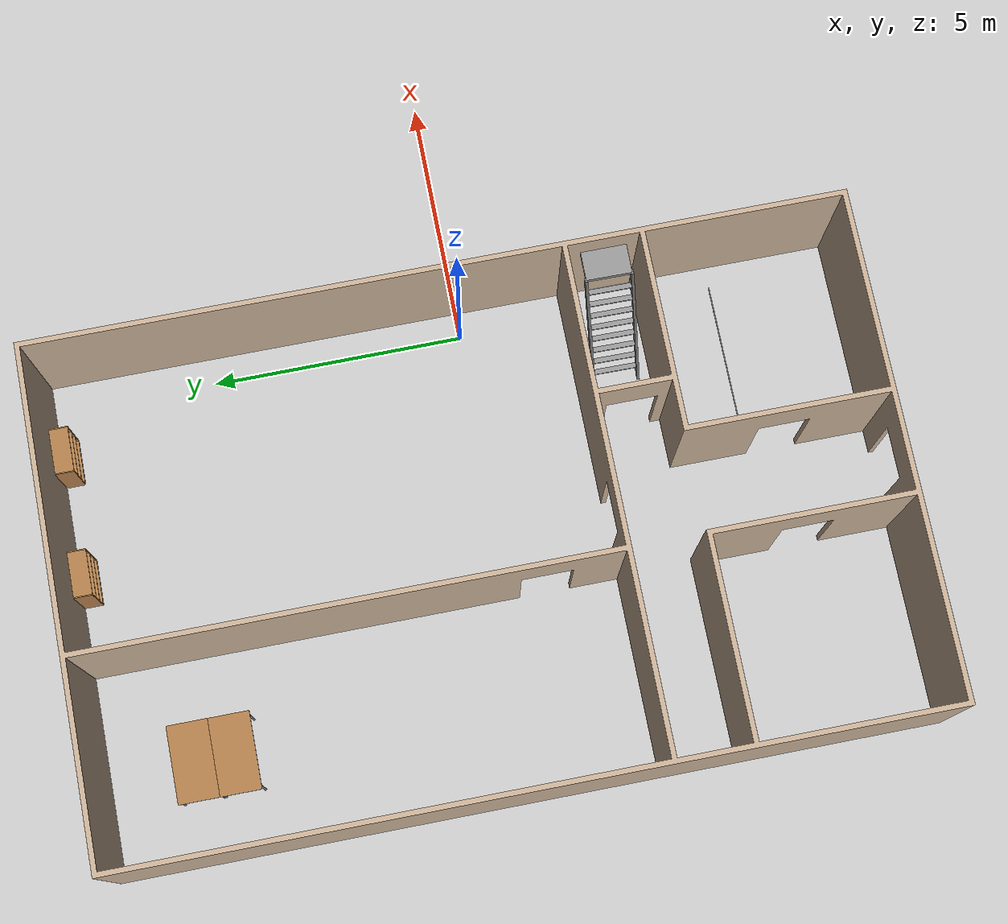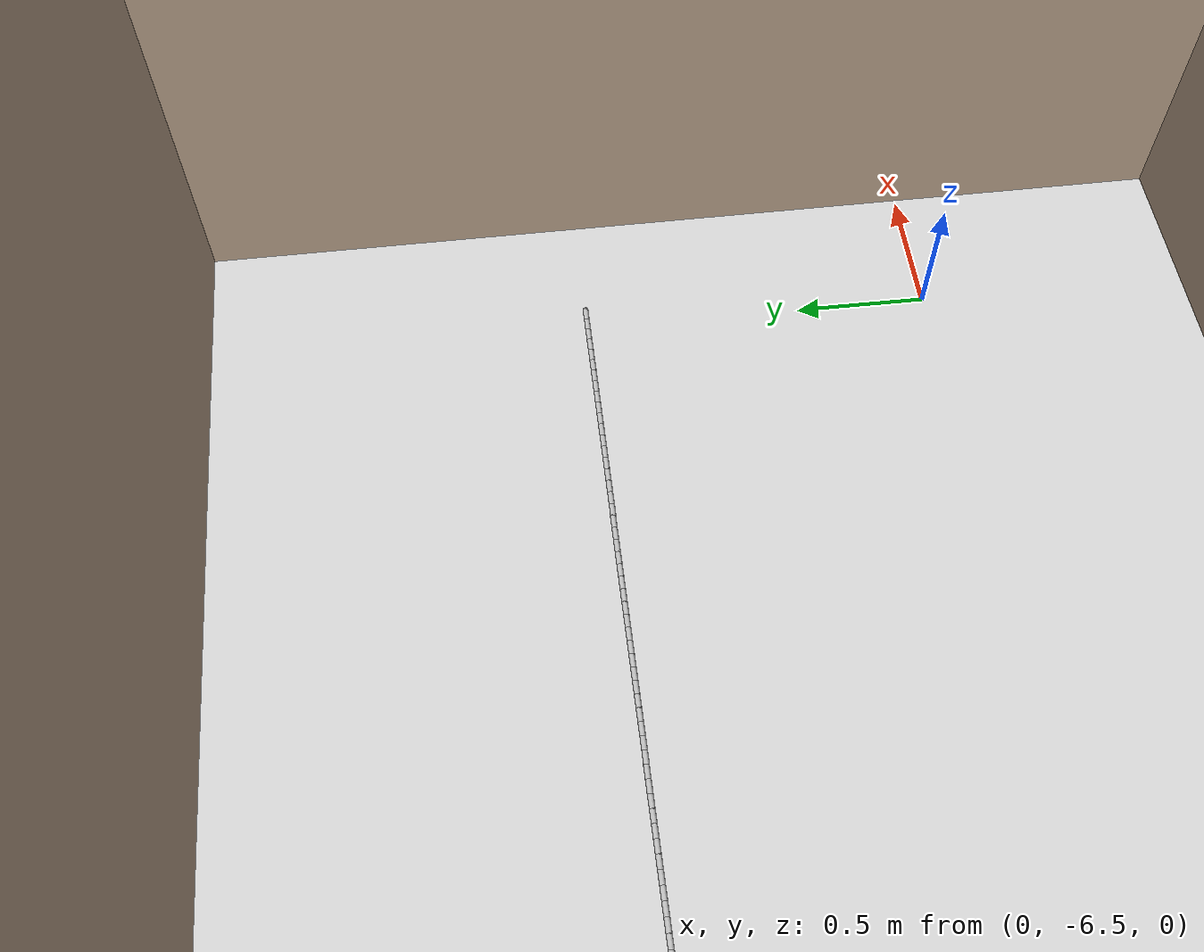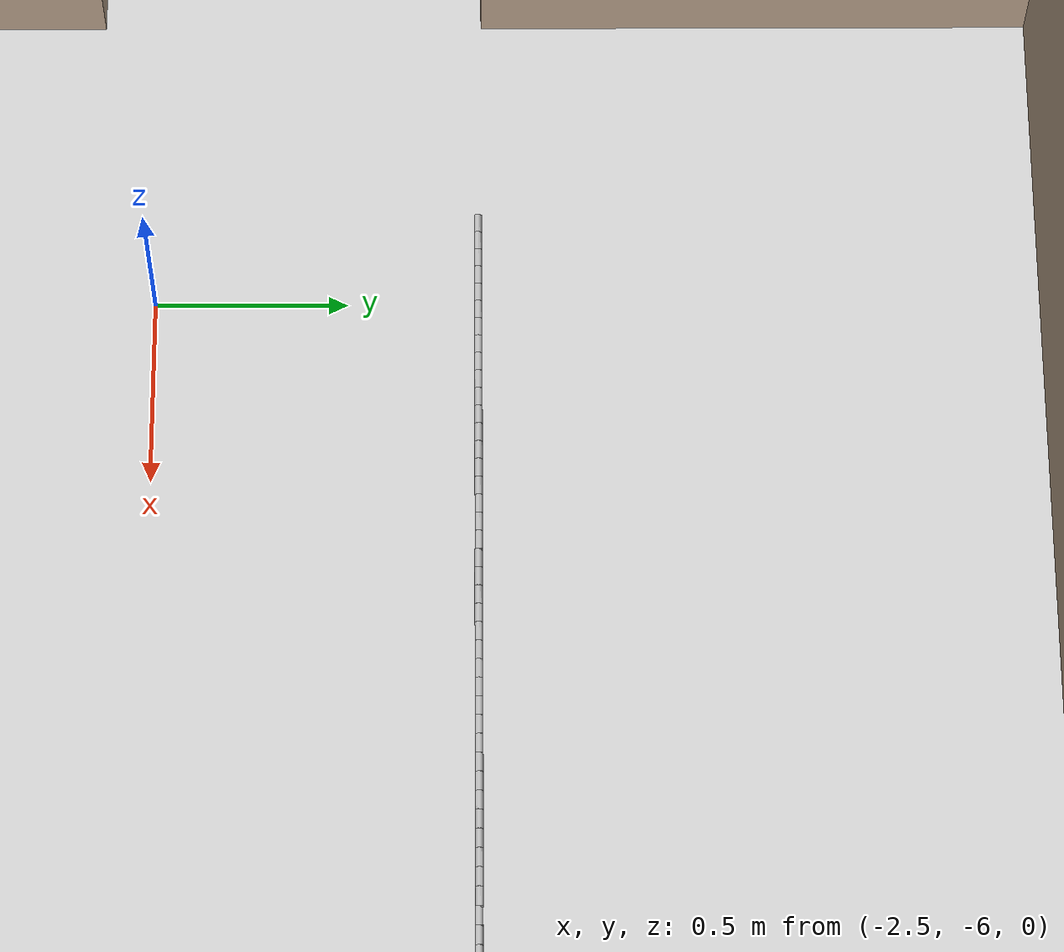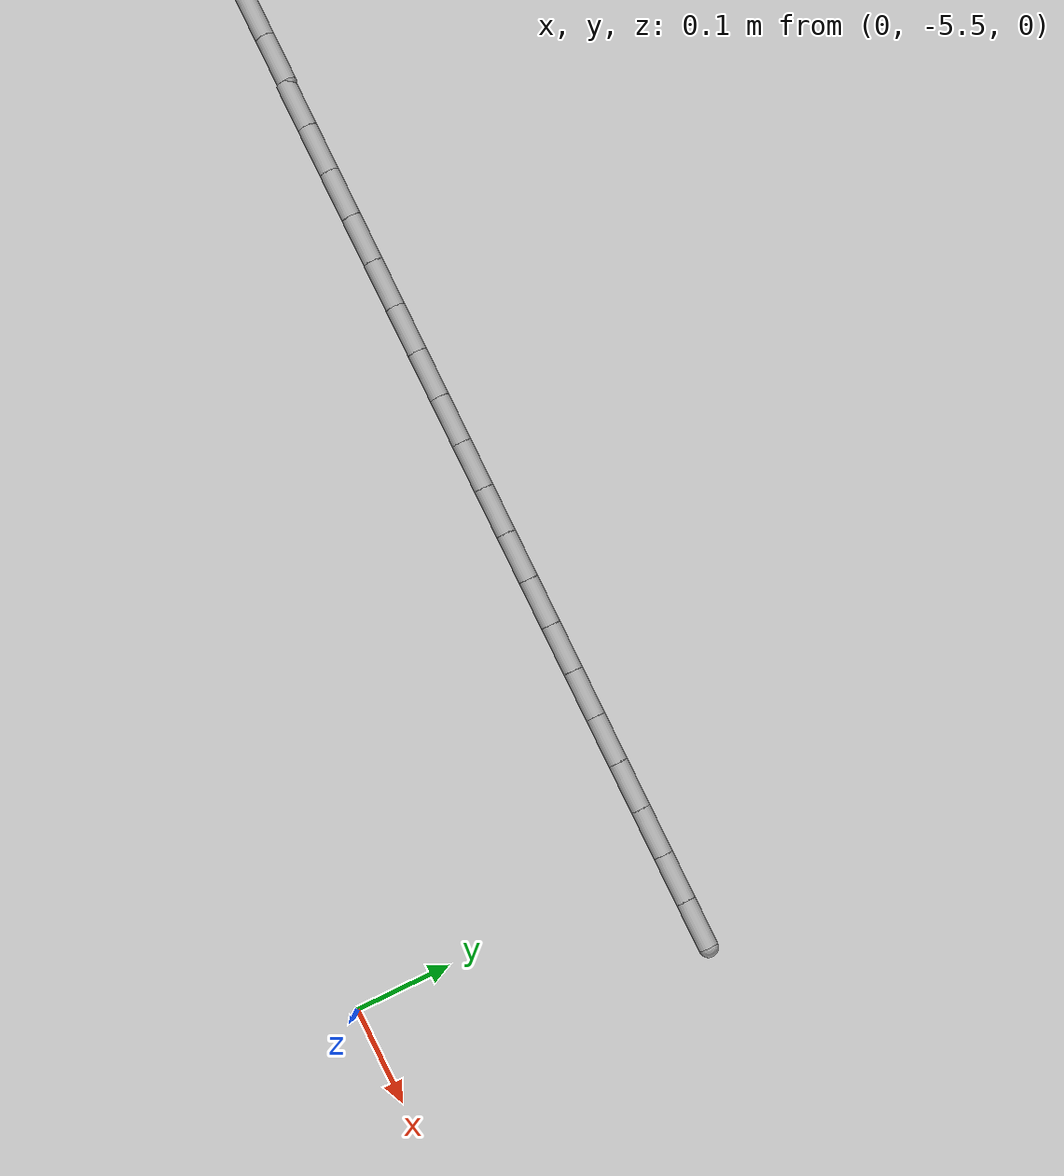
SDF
<sdf version="1.7">
 <world name="house_interior">
  <light name="sun" type="directional">
   <pose>0 0 10 0 -0 0</pose>
   <diffuse>0.8 0.8 0.8 1</diffuse>
   <specular>0.2 0.2 0.2 1</specular>
   <attenuation>
    <range>1000</range>
    <constant>0.9</constant>
    <linear>0.01</linear>
    <quadratic>0.001</quadratic>
   </attenuation>
   <direction>-0.5 0.1 -0.9</direction>
   <spot><inner_angle>0</inner_angle><outer_angle>0</outer_angle><falloff>0</falloff></spot>
  </light>
  <model name="ground_plane">
   <static>1</static>
   <link name="link">
    <collision name="collision">
     <geometry><plane><normal>0 0 1</normal><size>100 100</size></plane></geometry>
     <surface><friction><ode><mu>100</mu><mu2>50</mu2></ode></friction></surface>
    </collision>
    <visual name="visual">
     <cast_shadows>0</cast_shadows>
     <geometry><plane><normal>0 0 1</normal><size>100 100</size></plane></geometry>
     <material>
      <script><uri>file://media/materials/scripts/gazebo.material</uri><name>Gazebo/Grey</name></script>
     </material>
    </visual>
   </link>
  </model>
  <gravity>0 0 -9.8</gravity>
  <magnetic_field>6e-06 2.3e-05 -4.2e-05</magnetic_field>
  <atmosphere type="adiabatic"/>
  <physics type="ode">
   <max_step_size>0.001</max_step_size>
   <real_time_factor>1</real_time_factor>
   <real_time_update_rate>1000</real_time_update_rate>
  </physics>
  <scene><ambient>0.4 0.4 0.4 1</ambient><background>0.7 0.7 0.7 1</background><shadows>1</shadows></scene>
  <audio><device>default</device></audio>
  <spherical_coordinates>
   <surface_model>EARTH_WGS84</surface_model>
   <latitude_deg>0</latitude_deg>
   <longitude_deg>0</longitude_deg>
   <elevation>0</elevation>
   <heading_deg>0</heading_deg>
  </spherical_coordinates>
  <model name="table">
   <static>1</static>
   <link name="link">
    <collision name="surface">
     <pose>0 0 1 0 -0 0</pose>
     <geometry><box><size>1.5 0.8 0.03</size></box></geometry>
     <surface><friction><ode><mu>0.6</mu><mu2>0.6</mu2></ode></friction></surface>
    </collision>
    <visual name="visual1">
     <pose>0 0 1 0 -0 0</pose>
     <geometry><box><size>1.5 0.8 0.03</size></box></geometry>
     <material>
      <script><uri>file://media/materials/scripts/gazebo.material</uri><name>Gazebo/Wood</name></script>
     </material>
    </visual>
    <collision name="front_left_leg">
     <pose>0.68 0.38 0.5 0 -0 0</pose>
     <geometry><cylinder><radius>0.02</radius><length>1</length></cylinder></geometry>
    </collision>
    <visual name="front_left_leg">
     <pose>0.68 0.38 0.5 0 -0 0</pose>
     <geometry><cylinder><radius>0.02</radius><length>1</length></cylinder></geometry>
     <material>
      <script><uri>file://media/materials/scripts/gazebo.material</uri><name>Gazebo/Grey</name></script>
     </material>
    </visual>
    <collision name="front_right_leg">
     <pose>0.68 -0.38 0.5 0 -0 0</pose>
     <geometry><cylinder><radius>0.02</radius><length>1</length></cylinder></geometry>
    </collision>
    <visual name="front_right_leg">
     <pose>0.68 -0.38 0.5 0 -0 0</pose>
     <geometry><cylinder><radius>0.02</radius><length>1</length></cylinder></geometry>
     <material>
      <script><uri>file://media/materials/scripts/gazebo.material</uri><name>Gazebo/Grey</name></script>
     </material>
    </visual>
    <collision name="back_right_leg">
     <pose>-0.68 -0.38 0.5 0 -0 0</pose>
     <geometry><cylinder><radius>0.02</radius><length>1</length></cylinder></geometry>
    </collision>
    <visual name="back_right_leg">
     <pose>-0.68 -0.38 0.5 0 -0 0</pose>
     <geometry><cylinder><radius>0.02</radius><length>1</length></cylinder></geometry>
     <material>
      <script><uri>file://media/materials/scripts/gazebo.material</uri><name>Gazebo/Grey</name></script>
     </material>
    </visual>
    <collision name="back_left_leg">
     <pose>-0.68 0.38 0.5 0 -0 0</pose>
     <geometry><cylinder><radius>0.02</radius><length>1</length></cylinder></geometry>
    </collision>
    <visual name="back_left_leg">
     <pose>-0.68 0.38 0.5 0 -0 0</pose>
     <geometry><cylinder><radius>0.02</radius><length>1</length></cylinder></geometry>
     <material>
      <script><uri>file://media/materials/scripts/gazebo.material</uri><name>Gazebo/Grey</name></script>
     </material>
    </visual>
   </link>
   <pose>-7.46885 6.52456 0 0 -0 0</pose>
  </model>
  <model name="bookshelf">
   <static>1</static>
   <link name="link">
    <inertial><mass>1</mass></inertial>
    <collision name="back">
     <pose>0 0.005 0.6 0 -0 0</pose>
     <geometry><box><size>0.9 0.01 1.2</size></box></geometry>
    </collision>
    <visual name="visual1">
     <pose>0 0.005 0.6 0 -0 0</pose>
     <geometry><box><size>0.9 0.01 1.2</size></box></geometry>
     <material>
      <script><uri>file://media/materials/scripts/gazebo.material</uri><name>Gazebo/Wood</name></script>
     </material>
    </visual>
    <collision name="left_side">
     <pose>0.45 -0.195 0.6 0 -0 0</pose>
     <geometry><box><size>0.02 0.4 1.2</size></box></geometry>
    </collision>
    <visual name="visual2">
     <pose>0.45 -0.195 0.6 0 -0 0</pose>
     <geometry><box><size>0.02 0.4 1.2</size></box></geometry>
     <material>
      <script><uri>file://media/materials/scripts/gazebo.material</uri><name>Gazebo/Wood</name></script>
     </material>
    </visual>
    <collision name="right_side">
     <pose>-0.45 -0.195 0.6 0 -0 0</pose>
     <geometry><box><size>0.02 0.4 1.2</size></box></geometry>
    </collision>
    <visual name="visual3">
     <pose>-0.45 -0.195 0.6 0 -0 0</pose>
     <geometry><box><size>0.02 0.4 1.2</size></box></geometry>
     <material>
      <script><uri>file://media/materials/scripts/gazebo.material</uri><name>Gazebo/Wood</name></script>
     </material>
    </visual>
    <collision name="bottom">
     <pose>0 -0.195 0.03 0 -0 0</pose>
     <geometry><box><size>0.88 0.4 0.06</size></box></geometry>
    </collision>
    <visual name="visual4">
     <pose>0 -0.195 0.03 0 -0 0</pose>
     <geometry><box><size>0.88 0.4 0.06</size></box></geometry>
     <material>
      <script><uri>file://media/materials/scripts/gazebo.material</uri><name>Gazebo/Wood</name></script>
     </material>
    </visual>
    <collision name="top">
     <pose>0 -0.195 1.19 0 -0 0</pose>
     <geometry><box><size>0.88 0.4 0.02</size></box></geometry>
    </collision>
    <visual name="visual5">
     <pose>0 -0.195 1.19 0 -0 0</pose>
     <geometry><box><size>0.88 0.4 0.02</size></box></geometry>
     <material>
      <script><uri>file://media/materials/scripts/gazebo.material</uri><name>Gazebo/Wood</name></script>
     </material>
    </visual>
    <collision name="low_shelf">
     <pose>0 -0.195 0.43 0 -0 0</pose>
     <geometry><box><size>0.88 0.4 0.02</size></box></geometry>
    </collision>
    <visual name="visual6">
     <pose>0 -0.195 0.43 0 -0 0</pose>
     <geometry><box><size>0.88 0.4 0.02</size></box></geometry>
     <material>
      <script><uri>file://media/materials/scripts/gazebo.material</uri><name>Gazebo/Wood</name></script>
     </material>
    </visual>
    <collision name="high_shelf">
     <pose>0 -0.195 0.8 0 -0 0</pose>
     <geometry><box><size>0.88 0.4 0.02</size></box></geometry>
    </collision>
    <visual name="visual7">
     <pose>0 -0.195 0.8 0 -0 0</pose>
     <geometry><box><size>0.88 0.4 0.02</size></box></geometry>
     <material>
      <script><uri>file://media/materials/scripts/gazebo.material</uri><name>Gazebo/Wood</name></script>
     </material>
    </visual>
   </link>
   <pose>-3.55591 8.27448 0 0 -0 0</pose>
  </model>
  <model name="bookshelf_0">
   <static>1</static>
   <link name="link">
    <inertial><mass>1</mass></inertial>
    <collision name="back">
     <pose>0 0.005 0.6 0 -0 0</pose>
     <geometry><box><size>0.9 0.01 1.2</size></box></geometry>
    </collision>
    <visual name="visual1">
     <pose>0 0.005 0.6 0 -0 0</pose>
     <geometry><box><size>0.9 0.01 1.2</size></box></geometry>
     <material>
      <script><uri>file://media/materials/scripts/gazebo.material</uri><name>Gazebo/Wood</name></script>
     </material>
    </visual>
    <collision name="left_side">
     <pose>0.45 -0.195 0.6 0 -0 0</pose>
     <geometry><box><size>0.02 0.4 1.2</size></box></geometry>
    </collision>
    <visual name="visual2">
     <pose>0.45 -0.195 0.6 0 -0 0</pose>
     <geometry><box><size>0.02 0.4 1.2</size></box></geometry>
     <material>
      <script><uri>file://media/materials/scripts/gazebo.material</uri><name>Gazebo/Wood</name></script>
     </material>
    </visual>
    <collision name="right_side">
     <pose>-0.45 -0.195 0.6 0 -0 0</pose>
     <geometry><box><size>0.02 0.4 1.2</size></box></geometry>
    </collision>
    <visual name="visual3">
     <pose>-0.45 -0.195 0.6 0 -0 0</pose>
     <geometry><box><size>0.02 0.4 1.2</size></box></geometry>
     <material>
      <script><uri>file://media/materials/scripts/gazebo.material</uri><name>Gazebo/Wood</name></script>
     </material>
    </visual>
    <collision name="bottom">
     <pose>0 -0.195 0.03 0 -0 0</pose>
     <geometry><box><size>0.88 0.4 0.06</size></box></geometry>
    </collision>
    <visual name="visual4">
     <pose>0 -0.195 0.03 0 -0 0</pose>
     <geometry><box><size>0.88 0.4 0.06</size></box></geometry>
     <material>
      <script><uri>file://media/materials/scripts/gazebo.material</uri><name>Gazebo/Wood</name></script>
     </material>
    </visual>
    <collision name="top">
     <pose>0 -0.195 1.19 0 -0 0</pose>
     <geometry><box><size>0.88 0.4 0.02</size></box></geometry>
    </collision>
    <visual name="visual5">
     <pose>0 -0.195 1.19 0 -0 0</pose>
     <geometry><box><size>0.88 0.4 0.02</size></box></geometry>
     <material>
      <script><uri>file://media/materials/scripts/gazebo.material</uri><name>Gazebo/Wood</name></script>
     </material>
    </visual>
    <collision name="low_shelf">
     <pose>0 -0.195 0.43 0 -0 0</pose>
     <geometry><box><size>0.88 0.4 0.02</size></box></geometry>
    </collision>
    <visual name="visual6">
     <pose>0 -0.195 0.43 0 -0 0</pose>
     <geometry><box><size>0.88 0.4 0.02</size></box></geometry>
     <material>
      <script><uri>file://media/materials/scripts/gazebo.material</uri><name>Gazebo/Wood</name></script>
     </material>
    </visual>
    <collision name="high_shelf">
     <pose>0 -0.195 0.8 0 -0 0</pose>
     <geometry><box><size>0.88 0.4 0.02</size></box></geometry>
    </collision>
    <visual name="visual7">
     <pose>0 -0.195 0.8 0 -0 0</pose>
     <geometry><box><size>0.88 0.4 0.02</size></box></geometry>
     <material>
      <script><uri>file://media/materials/scripts/gazebo.material</uri><name>Gazebo/Wood</name></script>
     </material>
    </visual>
   </link>
   <pose>-1.09501 8.26834 0 0 -0 0</pose>
  </model>
  <model name="ladder_60deg_0rails">
   <static>1</static>
   <link name="step0">
    <pose>0 0.15396 0.266667 0 -0 0</pose>
    <inertial>
     <mass>9.75482</mass>
     <inertia>
      <ixx>0.00957124</ixx>
      <iyy>0.65963</iyy>
      <izz>0.666842</izz>
      <ixy>0</ixy>
      <ixz>0</ixz>
      <iyz>0</iyz>
     </inertia>
    </inertial>
    <collision name="collision"><geometry><box><size>0.9 0.1016 0.0381</size></box></geometry></collision>
    <visual name="visual">
     <geometry><box><size>0.9 0.1016 0.0381</size></box></geometry>
     <material>
      <script><uri>file://media/materials/scripts/gazebo.material</uri><name>Gazebo/Grey</name></script>
     </material>
    </visual>
   </link>
   <link name="step1">
    <pose>0 0.30792 0.533333 0 -0 0</pose>
    <inertial>
     <mass>9.75482</mass>
     <inertia>
      <ixx>0.00957124</ixx>
      <iyy>0.65963</iyy>
      <izz>0.666842</izz>
      <ixy>0</ixy>
      <ixz>0</ixz>
      <iyz>0</iyz>
     </inertia>
    </inertial>
    <collision name="collision"><geometry><box><size>0.9 0.1016 0.0381</size></box></geometry></collision>
    <visual name="visual">
     <geometry><box><size>0.9 0.1016 0.0381</size></box></geometry>
     <material>
      <script><uri>file://media/materials/scripts/gazebo.material</uri><name>Gazebo/Grey</name></script>
     </material>
    </visual>
   </link>
   <link name="step2">
    <pose>0 0.46188 0.8 0 -0 0</pose>
    <inertial>
     <mass>9.75482</mass>
     <inertia>
      <ixx>0.00957124</ixx>
      <iyy>0.65963</iyy>
      <izz>0.666842</izz>
      <ixy>0</ixy>
      <ixz>0</ixz>
      <iyz>0</iyz>
     </inertia>
    </inertial>
    <collision name="collision"><geometry><box><size>0.9 0.1016 0.0381</size></box></geometry></collision>
    <visual name="visual">
     <geometry><box><size>0.9 0.1016 0.0381</size></box></geometry>
     <material>
      <script><uri>file://media/materials/scripts/gazebo.material</uri><name>Gazebo/Grey</name></script>
     </material>
    </visual>
   </link>
   <link name="step3">
    <pose>0 0.61584 1.06667 0 -0 0</pose>
    <inertial>
     <mass>9.75482</mass>
     <inertia>
      <ixx>0.00957124</ixx>
      <iyy>0.65963</iyy>
      <izz>0.666842</izz>
      <ixy>0</ixy>
      <ixz>0</ixz>
      <iyz>0</iyz>
     </inertia>
    </inertial>
    <collision name="collision"><geometry><box><size>0.9 0.1016 0.0381</size></box></geometry></collision>
    <visual name="visual">
     <geometry><box><size>0.9 0.1016 0.0381</size></box></geometry>
     <material>
      <script><uri>file://media/materials/scripts/gazebo.material</uri><name>Gazebo/Grey</name></script>
     </material>
    </visual>
   </link>
   <link name="step4">
    <pose>0 0.7698 1.33333 0 -0 0</pose>
    <inertial>
     <mass>9.75482</mass>
     <inertia>
      <ixx>0.00957124</ixx>
      <iyy>0.65963</iyy>
      <izz>0.666842</izz>
      <ixy>0</ixy>
      <ixz>0</ixz>
      <iyz>0</iyz>
     </inertia>
    </inertial>
    <collision name="collision"><geometry><box><size>0.9 0.1016 0.0381</size></box></geometry></collision>
    <visual name="visual">
     <geometry><box><size>0.9 0.1016 0.0381</size></box></geometry>
     <material>
      <script><uri>file://media/materials/scripts/gazebo.material</uri><name>Gazebo/Grey</name></script>
     </material>
    </visual>
   </link>
   <link name="step5">
    <pose>0 0.92376 1.6 0 -0 0</pose>
    <inertial>
     <mass>9.75482</mass>
     <inertia>
      <ixx>0.00957124</ixx>
      <iyy>0.65963</iyy>
      <izz>0.666842</izz>
      <ixy>0</ixy>
      <ixz>0</ixz>
      <iyz>0</iyz>
     </inertia>
    </inertial>
    <collision name="collision"><geometry><box><size>0.9 0.1016 0.0381</size></box></geometry></collision>
    <visual name="visual">
     <geometry><box><size>0.9 0.1016 0.0381</size></box></geometry>
     <material>
      <script><uri>file://media/materials/scripts/gazebo.material</uri><name>Gazebo/Grey</name></script>
     </material>
    </visual>
   </link>
   <link name="step6">
    <pose>0 1.07772 1.86667 0 -0 0</pose>
    <inertial>
     <mass>9.75482</mass>
     <inertia>
      <ixx>0.00957124</ixx>
      <iyy>0.65963</iyy>
      <izz>0.666842</izz>
      <ixy>0</ixy>
      <ixz>0</ixz>
      <iyz>0</iyz>
     </inertia>
    </inertial>
    <collision name="collision"><geometry><box><size>0.9 0.1016 0.0381</size></box></geometry></collision>
    <visual name="visual">
     <geometry><box><size>0.9 0.1016 0.0381</size></box></geometry>
     <material>
      <script><uri>file://media/materials/scripts/gazebo.material</uri><name>Gazebo/Grey</name></script>
     </material>
    </visual>
   </link>
   <link name="step7">
    <pose>0 1.23168 2.13333 0 -0 0</pose>
    <inertial>
     <mass>9.75482</mass>
     <inertia>
      <ixx>0.00957124</ixx>
      <iyy>0.65963</iyy>
      <izz>0.666842</izz>
      <ixy>0</ixy>
      <ixz>0</ixz>
      <iyz>0</iyz>
     </inertia>
    </inertial>
    <collision name="collision"><geometry><box><size>0.9 0.1016 0.0381</size></box></geometry></collision>
    <visual name="visual">
     <geometry><box><size>0.9 0.1016 0.0381</size></box></geometry>
     <material>
      <script><uri>file://media/materials/scripts/gazebo.material</uri><name>Gazebo/Grey</name></script>
     </material>
    </visual>
   </link>
   <link name="landing">
    <pose>0 1.68564 2.4 0 -0 0</pose>
    <inertial>
     <mass>57.6072</mass>
     <inertia><ixx>1.73518</ixx><iyy>3.89545</iyy><izz>5.6167</izz><ixy>0</ixy><ixz>0</ixz><iyz>0</iyz></inertia>
    </inertial>
    <collision name="collision"><geometry><box><size>0.9 0.6 0.1016</size></box></geometry></collision>
    <visual name="visual">
     <geometry><box><size>0.9 0.6 0.1016</size></box></geometry>
     <material>
      <script><uri>file://media/materials/scripts/gazebo.material</uri><name>Gazebo/Grey</name></script>
     </material>
    </visual>
   </link>
   <link name="left_side_wall">
    <pose>-0.45 0.69282 1.2 1.0472 -0 0</pose>
    <collision name="collision"><geometry><box><size>0.0508 2.85128 0.13</size></box></geometry></collision>
    <visual name="visual">
     <geometry><box><size>0.0508 2.85128 0.13</size></box></geometry>
     <material>
      <script><uri>file://media/materials/scripts/gazebo.material</uri><name>Gazebo/Grey</name></script>
     </material>
    </visual>
   </link>
   <link name="right_side_wall">
    <pose>0.45 0.69282 1.2 1.0472 -0 0</pose>
    <collision name="collision"><geometry><box><size>0.0508 2.85128 0.13</size></box></geometry></collision>
    <visual name="visual">
     <geometry><box><size>0.0508 2.85128 0.13</size></box></geometry>
     <material>
      <script><uri>file://media/materials/scripts/gazebo.material</uri><name>Gazebo/Grey</name></script>
     </material>
    </visual>
   </link>
   <pose>-1.43725 -2.91526 0 0 0 -1.57889</pose>
  </model>
  <model name="table_0">
   <static>1</static>
   <link name="link">
    <collision name="surface">
     <pose>0 0 1 0 -0 0</pose>
     <geometry><box><size>1.5 0.8 0.03</size></box></geometry>
     <surface><friction><ode><mu>0.6</mu><mu2>0.6</mu2></ode></friction></surface>
    </collision>
    <visual name="visual1">
     <pose>0 0 1 0 -0 0</pose>
     <geometry><box><size>1.5 0.8 0.03</size></box></geometry>
     <material>
      <script><uri>file://media/materials/scripts/gazebo.material</uri><name>Gazebo/Wood</name></script>
     </material>
    </visual>
    <collision name="front_left_leg">
     <pose>0.68 0.38 0.5 0 -0 0</pose>
     <geometry><cylinder><radius>0.02</radius><length>1</length></cylinder></geometry>
    </collision>
    <visual name="front_left_leg">
     <pose>0.68 0.38 0.5 0 -0 0</pose>
     <geometry><cylinder><radius>0.02</radius><length>1</length></cylinder></geometry>
     <material>
      <script><uri>file://media/materials/scripts/gazebo.material</uri><name>Gazebo/Grey</name></script>
     </material>
    </visual>
    <collision name="front_right_leg">
     <pose>0.68 -0.38 0.5 0 -0 0</pose>
     <geometry><cylinder><radius>0.02</radius><length>1</length></cylinder></geometry>
    </collision>
    <visual name="front_right_leg">
     <pose>0.68 -0.38 0.5 0 -0 0</pose>
     <geometry><cylinder><radius>0.02</radius><length>1</length></cylinder></geometry>
     <material>
      <script><uri>file://media/materials/scripts/gazebo.material</uri><name>Gazebo/Grey</name></script>
     </material>
    </visual>
    <collision name="back_right_leg">
     <pose>-0.68 -0.38 0.5 0 -0 0</pose>
     <geometry><cylinder><radius>0.02</radius><length>1</length></cylinder></geometry>
    </collision>
    <visual name="back_right_leg">
     <pose>-0.68 -0.38 0.5 0 -0 0</pose>
     <geometry><cylinder><radius>0.02</radius><length>1</length></cylinder></geometry>
     <material>
      <script><uri>file://media/materials/scripts/gazebo.material</uri><name>Gazebo/Grey</name></script>
     </material>
    </visual>
    <collision name="back_left_leg">
     <pose>-0.68 0.38 0.5 0 -0 0</pose>
     <geometry><cylinder><radius>0.02</radius><length>1</length></cylinder></geometry>
    </collision>
    <visual name="back_left_leg">
     <pose>-0.68 0.38 0.5 0 -0 0</pose>
     <geometry><cylinder><radius>0.02</radius><length>1</length></cylinder></geometry>
     <material>
      <script><uri>file://media/materials/scripts/gazebo.material</uri><name>Gazebo/Grey</name></script>
     </material>
    </visual>
   </link>
   <pose>-7.47146 5.73164 0 0 -0 0</pose>
  </model>
  <model name="house_walls_0">
   <link name="link_2">
    <inertial>
     <mass>1</mass>
     <inertia>
      <ixx>0.166667</ixx>
      <ixy>0</ixy>
      <ixz>0</ixz>
      <iyy>0.166667</iyy>
      <iyz>0</iyz>
      <izz>0.166667</izz>
     </inertia>
    </inertial>
    <pose>1e-06 -2e-06 0 0 -0 0</pose>
    <visual name="visual">
     <geometry><mesh><uri>model://house_walls.dae</uri><scale>1 1 1</scale></mesh></geometry>
     <material>
      <ambient>0.5 0.4 0.3 1</ambient>
      <diffuse>0.8 0.7 0.6 1</diffuse>
      <specular>0.3 0.3 0.3 1</specular>
      <emissive>0.1 0.1 0.1 1</emissive>
      <shader type="pixel"/>
      <script><name>ModelPreview_3::link_2::visual_MATERIAL_</name><uri>__default__</uri></script>
     </material>
    </visual>
    <collision name="collision">
     <geometry><mesh><uri>model://house_walls.dae</uri><scale>1 1 1</scale></mesh></geometry>
     <surface>
      <friction>
       <ode><mu>1</mu><mu2>1</mu2><fdir1>0 0 0</fdir1><slip1>0</slip1><slip2>0</slip2></ode>
       <torsional>
        <coefficient>1</coefficient>
        <patch_radius>0</patch_radius>
        <surface_radius>0</surface_radius>
        <use_patch_radius>1</use_patch_radius>
        <ode><slip>0</slip></ode>
       </torsional>
      </friction>
      <bounce><restitution_coefficient>0</restitution_coefficient><threshold>1e+06</threshold></bounce>
      <contact>
       <collide_without_contact>0</collide_without_contact>
       <collide_without_contact_bitmask>1</collide_without_contact_bitmask>
       <collide_bitmask>1</collide_bitmask>
       <ode>
        <soft_cfm>0</soft_cfm>
        <soft_erp>0.2</soft_erp>
        <kp>1e+13</kp>
        <kd>1</kd>
        <max_vel>0.01</max_vel>
        <min_depth>0</min_depth>
       </ode>
       <bullet>
        <split_impulse>1</split_impulse>
        <split_impulse_penetration_threshold>-0.01</split_impulse_penetration_threshold>
        <soft_cfm>0</soft_cfm>
        <soft_erp>0.2</soft_erp>
        <kp>1e+13</kp>
        <kd>1</kd>
       </bullet>
      </contact>
     </surface>
    </collision>
   </link>
   <static>1</static>
   <pose>-4.37432 0.346559 0 0 -0 0</pose>
  </model>
  <model name="long_cable">
   <link name="link_01">
    <pose>0.05 0 0 0 -0 0</pose>
    <inertial>
     <mass>0.005</mass>
     <inertia><ixx>0.01</ixx><ixy>0</ixy><ixz>0</ixz><iyy>0.01</iyy><iyz>0</iyz><izz>0.01</izz></inertia>
    </inertial>
    <visual name="link_01_vis">
     <pose>0.025 0 0 0 1.57079 0</pose>
     <geometry><cylinder><length>0.05</length><radius>0.01</radius></cylinder></geometry>
     <material><shader type="pixel"/></material>
    </visual>
    <collision name="link_01_collision">
     <pose>0.025 0 0 0 1.57079 0</pose>
     <geometry><cylinder><radius>0.01</radius><length>0.05</length></cylinder></geometry>
     <surface>
      <friction>
       <ode><mu>1</mu><mu2>1</mu2><fdir1>0 0 0</fdir1><slip1>0</slip1><slip2>0</slip2></ode>
       <torsional>
        <coefficient>1</coefficient>
        <patch_radius>0</patch_radius>
        <surface_radius>0</surface_radius>
        <use_patch_radius>1</use_patch_radius>
        <ode><slip>0</slip></ode>
       </torsional>
      </friction>
      <bounce><restitution_coefficient>0</restitution_coefficient><threshold>1e+06</threshold></bounce>
      <contact>
       <collide_without_contact>0</collide_without_contact>
       <collide_without_contact_bitmask>1</collide_without_contact_bitmask>
       <collide_bitmask>1</collide_bitmask>
       <ode>
        <soft_cfm>0</soft_cfm>
        <soft_erp>0.2</soft_erp>
        <kp>1e+13</kp>
        <kd>1</kd>
        <max_vel>0.01</max_vel>
        <min_depth>0</min_depth>
       </ode>
       <bullet>
        <split_impulse>1</split_impulse>
        <split_impulse_penetration_threshold>-0.01</split_impulse_penetration_threshold>
        <soft_cfm>0</soft_cfm>
        <soft_erp>0.2</soft_erp>
        <kp>1e+13</kp>
        <kd>1</kd>
       </bullet>
      </contact>
     </surface>
    </collision>
   </link>
   <link name="link_02">
    <pose>0.1 0 0 0 -0 0</pose>
    <inertial>
     <mass>0.005</mass>
     <inertia><ixx>0.01</ixx><ixy>0</ixy><ixz>0</ixz><iyy>0.01</iyy><iyz>0</iyz><izz>0.01</izz></inertia>
    </inertial>
    <visual name="link_02_vis">
     <pose>0.025 0 0 0 1.57079 0</pose>
     <geometry><cylinder><length>0.05</length><radius>0.01</radius></cylinder></geometry>
     <material><shader type="pixel"/></material>
    </visual>
    <collision name="link_02_collision">
     <pose>0.025 0 0 0 1.57079 0</pose>
     <geometry><cylinder><radius>0.01</radius><length>0.05</length></cylinder></geometry>
     <surface>
      <friction>
       <ode><mu>1</mu><mu2>1</mu2><fdir1>0 0 0</fdir1><slip1>0</slip1><slip2>0</slip2></ode>
       <torsional>
        <coefficient>1</coefficient>
        <patch_radius>0</patch_radius>
        <surface_radius>0</surface_radius>
        <use_patch_radius>1</use_patch_radius>
        <ode><slip>0</slip></ode>
       </torsional>
      </friction>
      <bounce><restitution_coefficient>0</restitution_coefficient><threshold>1e+06</threshold></bounce>
      <contact>
       <collide_without_contact>0</collide_without_contact>
       <collide_without_contact_bitmask>1</collide_without_contact_bitmask>
       <collide_bitmask>1</collide_bitmask>
       <ode>
        <soft_cfm>0</soft_cfm>
        <soft_erp>0.2</soft_erp>
        <kp>1e+13</kp>
        <kd>1</kd>
        <max_vel>0.01</max_vel>
        <min_depth>0</min_depth>
       </ode>
       <bullet>
        <split_impulse>1</split_impulse>
        <split_impulse_penetration_threshold>-0.01</split_impulse_penetration_threshold>
        <soft_cfm>0</soft_cfm>
        <soft_erp>0.2</soft_erp>
        <kp>1e+13</kp>
        <kd>1</kd>
       </bullet>
      </contact>
     </surface>
    </collision>
   </link>
   <link name="link_03">
    <pose>0.15 0 0 0 -0 0</pose>
    <inertial>
     <mass>0.005</mass>
     <inertia><ixx>0.01</ixx><ixy>0</ixy><ixz>0</ixz><iyy>0.01</iyy><iyz>0</iyz><izz>0.01</izz></inertia>
    </inertial>
    <visual name="link_03_vis">
     <pose>0.025 0 0 0 1.57079 0</pose>
     <geometry><cylinder><length>0.05</length><radius>0.01</radius></cylinder></geometry>
     <material><shader type="pixel"/></material>
    </visual>
    <collision name="link_03_collision">
     <pose>0.025 0 0 0 1.57079 0</pose>
     <geometry><cylinder><radius>0.01</radius><length>0.05</length></cylinder></geometry>
     <surface>
      <friction>
       <ode><mu>1</mu><mu2>1</mu2><fdir1>0 0 0</fdir1><slip1>0</slip1><slip2>0</slip2></ode>
       <torsional>
        <coefficient>1</coefficient>
        <patch_radius>0</patch_radius>
        <surface_radius>0</surface_radius>
        <use_patch_radius>1</use_patch_radius>
        <ode><slip>0</slip></ode>
       </torsional>
      </friction>
      <bounce><restitution_coefficient>0</restitution_coefficient><threshold>1e+06</threshold></bounce>
      <contact>
       <collide_without_contact>0</collide_without_contact>
       <collide_without_contact_bitmask>1</collide_without_contact_bitmask>
       <collide_bitmask>1</collide_bitmask>
       <ode>
        <soft_cfm>0</soft_cfm>
        <soft_erp>0.2</soft_erp>
        <kp>1e+13</kp>
        <kd>1</kd>
        <max_vel>0.01</max_vel>
        <min_depth>0</min_depth>
       </ode>
       <bullet>
        <split_impulse>1</split_impulse>
        <split_impulse_penetration_threshold>-0.01</split_impulse_penetration_threshold>
        <soft_cfm>0</soft_cfm>
        <soft_erp>0.2</soft_erp>
        <kp>1e+13</kp>
        <kd>1</kd>
       </bullet>
      </contact>
     </surface>
    </collision>
   </link>
   <link name="link_04">
    <pose>0.2 0 0 0 -0 0</pose>
    <inertial>
     <mass>0.005</mass>
     <inertia><ixx>0.01</ixx><ixy>0</ixy><ixz>0</ixz><iyy>0.01</iyy><iyz>0</iyz><izz>0.01</izz></inertia>
    </inertial>
    <visual name="link_04_vis">
     <pose>0.025 0 0 0 1.57079 0</pose>
     <geometry><cylinder><length>0.05</length><radius>0.01</radius></cylinder></geometry>
     <material><shader type="pixel"/></material>
    </visual>
    <collision name="link_04_collision">
     <pose>0.025 0 0 0 1.57079 0</pose>
     <geometry><cylinder><radius>0.01</radius><length>0.05</length></cylinder></geometry>
     <surface>
      <friction>
       <ode><mu>1</mu><mu2>1</mu2><fdir1>0 0 0</fdir1><slip1>0</slip1><slip2>0</slip2></ode>
       <torsional>
        <coefficient>1</coefficient>
        <patch_radius>0</patch_radius>
        <surface_radius>0</surface_radius>
        <use_patch_radius>1</use_patch_radius>
        <ode><slip>0</slip></ode>
       </torsional>
      </friction>
      <bounce><restitution_coefficient>0</restitution_coefficient><threshold>1e+06</threshold></bounce>
      <contact>
       <collide_without_contact>0</collide_without_contact>
       <collide_without_contact_bitmask>1</collide_without_contact_bitmask>
       <collide_bitmask>1</collide_bitmask>
       <ode>
        <soft_cfm>0</soft_cfm>
        <soft_erp>0.2</soft_erp>
        <kp>1e+13</kp>
        <kd>1</kd>
        <max_vel>0.01</max_vel>
        <min_depth>0</min_depth>
       </ode>
       <bullet>
        <split_impulse>1</split_impulse>
        <split_impulse_penetration_threshold>-0.01</split_impulse_penetration_threshold>
        <soft_cfm>0</soft_cfm>
        <soft_erp>0.2</soft_erp>
        <kp>1e+13</kp>
        <kd>1</kd>
       </bullet>
      </contact>
     </surface>
    </collision>
   </link>
   <link name="link_05">
    <pose>0.25 0 0 0 -0 0</pose>
    <inertial>
     <mass>0.005</mass>
     <inertia><ixx>0.01</ixx><ixy>0</ixy><ixz>0</ixz><iyy>0.01</iyy><iyz>0</iyz><izz>0.01</izz></inertia>
    </inertial>
    <visual name="link_05_vis">
     <pose>0.025 0 0 0 1.57079 0</pose>
     <geometry><cylinder><length>0.05</length><radius>0.01</radius></cylinder></geometry>
     <material><shader type="pixel"/></material>
    </visual>
    <collision name="link_05_collision">
     <pose>0.025 0 0 0 1.57079 0</pose>
     <geometry><cylinder><radius>0.01</radius><length>0.05</length></cylinder></geometry>
     <surface>
      <friction>
       <ode><mu>1</mu><mu2>1</mu2><fdir1>0 0 0</fdir1><slip1>0</slip1><slip2>0</slip2></ode>
       <torsional>
        <coefficient>1</coefficient>
        <patch_radius>0</patch_radius>
        <surface_radius>0</surface_radius>
        <use_patch_radius>1</use_patch_radius>
        <ode><slip>0</slip></ode>
       </torsional>
      </friction>
      <bounce><restitution_coefficient>0</restitution_coefficient><threshold>1e+06</threshold></bounce>
      <contact>
       <collide_without_contact>0</collide_without_contact>
       <collide_without_contact_bitmask>1</collide_without_contact_bitmask>
       <collide_bitmask>1</collide_bitmask>
       <ode>
        <soft_cfm>0</soft_cfm>
        <soft_erp>0.2</soft_erp>
        <kp>1e+13</kp>
        <kd>1</kd>
        <max_vel>0.01</max_vel>
        <min_depth>0</min_depth>
       </ode>
       <bullet>
        <split_impulse>1</split_impulse>
        <split_impulse_penetration_threshold>-0.01</split_impulse_penetration_threshold>
        <soft_cfm>0</soft_cfm>
        <soft_erp>0.2</soft_erp>
        <kp>1e+13</kp>
        <kd>1</kd>
       </bullet>
      </contact>
     </surface>
    </collision>
   </link>
   <link name="link_06">
    <pose>0.3 0 0 0 -0 0</pose>
    <inertial>
     <mass>0.005</mass>
     <inertia><ixx>0.01</ixx><ixy>0</ixy><ixz>0</ixz><iyy>0.01</iyy><iyz>0</iyz><izz>0.01</izz></inertia>
    </inertial>
    <visual name="link_06_vis">
     <pose>0.025 0 0 0 1.57079 0</pose>
     <geometry><cylinder><length>0.05</length><radius>0.01</radius></cylinder></geometry>
     <material><shader type="pixel"/></material>
    </visual>
    <collision name="link_06_collision">
     <pose>0.025 0 0 0 1.57079 0</pose>
     <geometry><cylinder><radius>0.01</radius><length>0.05</length></cylinder></geometry>
     <surface>
      <friction>
       <ode><mu>1</mu><mu2>1</mu2><fdir1>0 0 0</fdir1><slip1>0</slip1><slip2>0</slip2></ode>
       <torsional>
        <coefficient>1</coefficient>
        <patch_radius>0</patch_radius>
        <surface_radius>0</surface_radius>
        <use_patch_radius>1</use_patch_radius>
        <ode><slip>0</slip></ode>
       </torsional>
      </friction>
      <bounce><restitution_coefficient>0</restitution_coefficient><threshold>1e+06</threshold></bounce>
      <contact>
       <collide_without_contact>0</collide_without_contact>
       <collide_without_contact_bitmask>1</collide_without_contact_bitmask>
       <collide_bitmask>1</collide_bitmask>
       <ode>
        <soft_cfm>0</soft_cfm>
        <soft_erp>0.2</soft_erp>
        <kp>1e+13</kp>
        <kd>1</kd>
        <max_vel>0.01</max_vel>
        <min_depth>0</min_depth>
       </ode>
       <bullet>
        <split_impulse>1</split_impulse>
        <split_impulse_penetration_threshold>-0.01</split_impulse_penetration_threshold>
        <soft_cfm>0</soft_cfm>
        <soft_erp>0.2</soft_erp>
        <kp>1e+13</kp>
        <kd>1</kd>
       </bullet>
      </contact>
     </surface>
    </collision>
   </link>
   <link name="link_07">
    <pose>0.35 0 0 0 -0 0</pose>
    <inertial>
     <mass>0.005</mass>
     <inertia><ixx>0.01</ixx><ixy>0</ixy><ixz>0</ixz><iyy>0.01</iyy><iyz>0</iyz><izz>0.01</izz></inertia>
    </inertial>
    <visual name="link_07_vis">
     <pose>0.025 0 0 0 1.57079 0</pose>
     <geometry><cylinder><length>0.05</length><radius>0.01</radius></cylinder></geometry>
     <material><shader type="pixel"/></material>
    </visual>
    <collision name="link_07_collision">
     <pose>0.025 0 0 0 1.57079 0</pose>
     <geometry><cylinder><radius>0.01</radius><length>0.05</length></cylinder></geometry>
     <surface>
      <friction>
       <ode><mu>1</mu><mu2>1</mu2><fdir1>0 0 0</fdir1><slip1>0</slip1><slip2>0</slip2></ode>
       <torsional>
        <coefficient>1</coefficient>
        <patch_radius>0</patch_radius>
        <surface_radius>0</surface_radius>
        <use_patch_radius>1</use_patch_radius>
        <ode><slip>0</slip></ode>
       </torsional>
      </friction>
      <bounce><restitution_coefficient>0</restitution_coefficient><threshold>1e+06</threshold></bounce>
      <contact>
       <collide_without_contact>0</collide_without_contact>
       <collide_without_contact_bitmask>1</collide_without_contact_bitmask>
       <collide_bitmask>1</collide_bitmask>
       <ode>
        <soft_cfm>0</soft_cfm>
        <soft_erp>0.2</soft_erp>
        <kp>1e+13</kp>
        <kd>1</kd>
        <max_vel>0.01</max_vel>
        <min_depth>0</min_depth>
       </ode>
       <bullet>
        <split_impulse>1</split_impulse>
        <split_impulse_penetration_threshold>-0.01</split_impulse_penetration_threshold>
        <soft_cfm>0</soft_cfm>
        <soft_erp>0.2</soft_erp>
        <kp>1e+13</kp>
        <kd>1</kd>
       </bullet>
      </contact>
     </surface>
    </collision>
   </link>
   <link name="link_08">
    <pose>0.4 0 0 0 -0 0</pose>
    <inertial>
     <mass>0.005</mass>
     <inertia><ixx>0.01</ixx><ixy>0</ixy><ixz>0</ixz><iyy>0.01</iyy><iyz>0</iyz><izz>0.01</izz></inertia>
    </inertial>
    <visual name="link_08_vis">
     <pose>0.025 0 0 0 1.57079 0</pose>
     <geometry><cylinder><length>0.05</length><radius>0.01</radius></cylinder></geometry>
     <material><shader type="pixel"/></material>
    </visual>
    <collision name="link_08_collision">
     <pose>0.025 0 0 0 1.57079 0</pose>
     <geometry><cylinder><radius>0.01</radius><length>0.05</length></cylinder></geometry>
     <surface>
      <friction>
       <ode><mu>1</mu><mu2>1</mu2><fdir1>0 0 0</fdir1><slip1>0</slip1><slip2>0</slip2></ode>
       <torsional>
        <coefficient>1</coefficient>
        <patch_radius>0</patch_radius>
        <surface_radius>0</surface_radius>
        <use_patch_radius>1</use_patch_radius>
        <ode><slip>0</slip></ode>
       </torsional>
      </friction>
      <bounce><restitution_coefficient>0</restitution_coefficient><threshold>1e+06</threshold></bounce>
      <contact>
       <collide_without_contact>0</collide_without_contact>
       <collide_without_contact_bitmask>1</collide_without_contact_bitmask>
       <collide_bitmask>1</collide_bitmask>
       <ode>
        <soft_cfm>0</soft_cfm>
        <soft_erp>0.2</soft_erp>
        <kp>1e+13</kp>
        <kd>1</kd>
        <max_vel>0.01</max_vel>
        <min_depth>0</min_depth>
       </ode>
       <bullet>
        <split_impulse>1</split_impulse>
        <split_impulse_penetration_threshold>-0.01</split_impulse_penetration_threshold>
        <soft_cfm>0</soft_cfm>
        <soft_erp>0.2</soft_erp>
        <kp>1e+13</kp>
        <kd>1</kd>
       </bullet>
      </contact>
     </surface>
    </collision>
   </link>
   <link name="link_09">
    <pose>0.45 0 0 0 -0 0</pose>
    <inertial>
     <mass>0.005</mass>
     <inertia><ixx>0.01</ixx><ixy>0</ixy><ixz>0</ixz><iyy>0.01</iyy><iyz>0</iyz><izz>0.01</izz></inertia>
    </inertial>
    <visual name="link_09_vis">
     <pose>0.025 0 0 0 1.57079 0</pose>
     <geometry><cylinder><length>0.05</length><radius>0.01</radius></cylinder></geometry>
     <material><shader type="pixel"/></material>
    </visual>
    <collision name="link_09_collision">
     <pose>0.025 0 0 0 1.57079 0</pose>
     <geometry><cylinder><radius>0.01</radius><length>0.05</length></cylinder></geometry>
     <surface>
      <friction>
       <ode><mu>1</mu><mu2>1</mu2><fdir1>0 0 0</fdir1><slip1>0</slip1><slip2>0</slip2></ode>
       <torsional>
        <coefficient>1</coefficient>
        <patch_radius>0</patch_radius>
        <surface_radius>0</surface_radius>
        <use_patch_radius>1</use_patch_radius>
        <ode><slip>0</slip></ode>
       </torsional>
      </friction>
      <bounce><restitution_coefficient>0</restitution_coefficient><threshold>1e+06</threshold></bounce>
      <contact>
       <collide_without_contact>0</collide_without_contact>
       <collide_without_contact_bitmask>1</collide_without_contact_bitmask>
       <collide_bitmask>1</collide_bitmask>
       <ode>
        <soft_cfm>0</soft_cfm>
        <soft_erp>0.2</soft_erp>
        <kp>1e+13</kp>
        <kd>1</kd>
        <max_vel>0.01</max_vel>
        <min_depth>0</min_depth>
       </ode>
       <bullet>
        <split_impulse>1</split_impulse>
        <split_impulse_penetration_threshold>-0.01</split_impulse_penetration_threshold>
        <soft_cfm>0</soft_cfm>
        <soft_erp>0.2</soft_erp>
        <kp>1e+13</kp>
        <kd>1</kd>
       </bullet>
      </contact>
     </surface>
    </collision>
   </link>
   <link name="link_10">
    <pose>0.5 0 0 0 -0 0</pose>
    <inertial>
     <mass>0.005</mass>
     <inertia><ixx>0.01</ixx><ixy>0</ixy><ixz>0</ixz><iyy>0.01</iyy><iyz>0</iyz><izz>0.01</izz></inertia>
    </inertial>
    <visual name="link_10_vis">
     <pose>0.025 0 0 0 1.57079 0</pose>
     <geometry><cylinder><length>0.05</length><radius>0.01</radius></cylinder></geometry>
     <material><shader type="pixel"/></material>
    </visual>
    <collision name="link_10_collision">
     <pose>0.025 0 0 0 1.57079 0</pose>
     <geometry><cylinder><radius>0.01</radius><length>0.05</length></cylinder></geometry>
     <surface>
      <friction>
       <ode><mu>1</mu><mu2>1</mu2><fdir1>0 0 0</fdir1><slip1>0</slip1><slip2>0</slip2></ode>
       <torsional>
        <coefficient>1</coefficient>
        <patch_radius>0</patch_radius>
        <surface_radius>0</surface_radius>
        <use_patch_radius>1</use_patch_radius>
        <ode><slip>0</slip></ode>
       </torsional>
      </friction>
      <bounce><restitution_coefficient>0</restitution_coefficient><threshold>1e+06</threshold></bounce>
      <contact>
       <collide_without_contact>0</collide_without_contact>
       <collide_without_contact_bitmask>1</collide_without_contact_bitmask>
       <collide_bitmask>1</collide_bitmask>
       <ode>
        <soft_cfm>0</soft_cfm>
        <soft_erp>0.2</soft_erp>
        <kp>1e+13</kp>
        <kd>1</kd>
        <max_vel>0.01</max_vel>
        <min_depth>0</min_depth>
       </ode>
       <bullet>
        <split_impulse>1</split_impulse>
        <split_impulse_penetration_threshold>-0.01</split_impulse_penetration_threshold>
        <soft_cfm>0</soft_cfm>
        <soft_erp>0.2</soft_erp>
        <kp>1e+13</kp>
        <kd>1</kd>
       </bullet>
      </contact>
     </surface>
    </collision>
   </link>
   <link name="link_11">
    <pose>0.55 0 0 0 -0 0</pose>
    <inertial>
     <mass>0.005</mass>
     <inertia><ixx>0.01</ixx><ixy>0</ixy><ixz>0</ixz><iyy>0.01</iyy><iyz>0</iyz><izz>0.01</izz></inertia>
    </inertial>
    <visual name="link_11_vis">
     <pose>0.025 0 0 0 1.57079 0</pose>
     <geometry><cylinder><length>0.05</length><radius>0.01</radius></cylinder></geometry>
     <material><shader type="pixel"/></material>
    </visual>
    <collision name="link_11_collision">
     <pose>0.025 0 0 0 1.57079 0</pose>
     <geometry><cylinder><radius>0.01</radius><length>0.05</length></cylinder></geometry>
     <surface>
      <friction>
       <ode><mu>1</mu><mu2>1</mu2><fdir1>0 0 0</fdir1><slip1>0</slip1><slip2>0</slip2></ode>
       <torsional>
        <coefficient>1</coefficient>
        <patch_radius>0</patch_radius>
        <surface_radius>0</surface_radius>
        <use_patch_radius>1</use_patch_radius>
        <ode><slip>0</slip></ode>
       </torsional>
      </friction>
      <bounce><restitution_coefficient>0</restitution_coefficient><threshold>1e+06</threshold></bounce>
      <contact>
       <collide_without_contact>0</collide_without_contact>
       <collide_without_contact_bitmask>1</collide_without_contact_bitmask>
       <collide_bitmask>1</collide_bitmask>
       <ode>
        <soft_cfm>0</soft_cfm>
        <soft_erp>0.2</soft_erp>
        <kp>1e+13</kp>
        <kd>1</kd>
        <max_vel>0.01</max_vel>
        <min_depth>0</min_depth>
       </ode>
       <bullet>
        <split_impulse>1</split_impulse>
        <split_impulse_penetration_threshold>-0.01</split_impulse_penetration_threshold>
        <soft_cfm>0</soft_cfm>
        <soft_erp>0.2</soft_erp>
        <kp>1e+13</kp>
        <kd>1</kd>
       </bullet>
      </contact>
     </surface>
    </collision>
   </link>
   <link name="link_12">
    <pose>0.6 0 0 0 -0 0</pose>
    <inertial>
     <mass>0.005</mass>
     <inertia><ixx>0.01</ixx><ixy>0</ixy><ixz>0</ixz><iyy>0.01</iyy><iyz>0</iyz><izz>0.01</izz></inertia>
    </inertial>
    <visual name="link_12_vis">
     <pose>0.025 0 0 0 1.57079 0</pose>
     <geometry><cylinder><length>0.05</length><radius>0.01</radius></cylinder></geometry>
     <material><shader type="pixel"/></material>
    </visual>
    <collision name="link_12_collision">
     <pose>0.025 0 0 0 1.57079 0</pose>
     <geometry><cylinder><radius>0.01</radius><length>0.05</length></cylinder></geometry>
     <surface>
      <friction>
       <ode><mu>1</mu><mu2>1</mu2><fdir1>0 0 0</fdir1><slip1>0</slip1><slip2>0</slip2></ode>
       <torsional>
        <coefficient>1</coefficient>
        <patch_radius>0</patch_radius>
        <surface_radius>0</surface_radius>
        <use_patch_radius>1</use_patch_radius>
        <ode><slip>0</slip></ode>
       </torsional>
      </friction>
      <bounce><restitution_coefficient>0</restitution_coefficient><threshold>1e+06</threshold></bounce>
      <contact>
       <collide_without_contact>0</collide_without_contact>
       <collide_without_contact_bitmask>1</collide_without_contact_bitmask>
       <collide_bitmask>1</collide_bitmask>
       <ode>
        <soft_cfm>0</soft_cfm>
        <soft_erp>0.2</soft_erp>
        <kp>1e+13</kp>
        <kd>1</kd>
        <max_vel>0.01</max_vel>
        <min_depth>0</min_depth>
       </ode>
       <bullet>
        <split_impulse>1</split_impulse>
        <split_impulse_penetration_threshold>-0.01</split_impulse_penetration_threshold>
        <soft_cfm>0</soft_cfm>
        <soft_erp>0.2</soft_erp>
        <kp>1e+13</kp>
        <kd>1</kd>
       </bullet>
      </contact>
     </surface>
    </collision>
   </link>
   <link name="link_13">
    <pose>0.65 0 0 0 -0 0</pose>
    <inertial>
     <mass>0.005</mass>
     <inertia><ixx>0.01</ixx><ixy>0</ixy><ixz>0</ixz><iyy>0.01</iyy><iyz>0</iyz><izz>0.01</izz></inertia>
    </inertial>
    <visual name="link_13_vis">
     <pose>0.025 0 0 0 1.57079 0</pose>
     <geometry><cylinder><length>0.05</length><radius>0.01</radius></cylinder></geometry>
     <material><shader type="pixel"/></material>
    </visual>
    <collision name="link_13_collision">
     <pose>0.025 0 0 0 1.57079 0</pose>
     <geometry><cylinder><radius>0.01</radius><length>0.05</length></cylinder></geometry>
     <surface>
      <friction>
       <ode><mu>1</mu><mu2>1</mu2><fdir1>0 0 0</fdir1><slip1>0</slip1><slip2>0</slip2></ode>
       <torsional>
        <coefficient>1</coefficient>
        <patch_radius>0</patch_radius>
        <surface_radius>0</surface_radius>
        <use_patch_radius>1</use_patch_radius>
        <ode><slip>0</slip></ode>
       </torsional>
      </friction>
      <bounce><restitution_coefficient>0</restitution_coefficient><threshold>1e+06</threshold></bounce>
      <contact>
       <collide_without_contact>0</collide_without_contact>
       <collide_without_contact_bitmask>1</collide_without_contact_bitmask>
       <collide_bitmask>1</collide_bitmask>
       <ode>
        <soft_cfm>0</soft_cfm>
        <soft_erp>0.2</soft_erp>
        <kp>1e+13</kp>
        <kd>1</kd>
        <max_vel>0.01</max_vel>
        <min_depth>0</min_depth>
       </ode>
       <bullet>
        <split_impulse>1</split_impulse>
        <split_impulse_penetration_threshold>-0.01</split_impulse_penetration_threshold>
        <soft_cfm>0</soft_cfm>
        <soft_erp>0.2</soft_erp>
        <kp>1e+13</kp>
        <kd>1</kd>
       </bullet>
      </contact>
     </surface>
    </collision>
   </link>
   <link name="link_14">
    <pose>0.7 0 0 0 -0 0</pose>
    <inertial>
     <mass>0.005</mass>
     <inertia><ixx>0.01</ixx><ixy>0</ixy><ixz>0</ixz><iyy>0.01</iyy><iyz>0</iyz><izz>0.01</izz></inertia>
    </inertial>
    <visual name="link_14_vis">
     <pose>0.025 0 0 0 1.57079 0</pose>
     <geometry><cylinder><length>0.05</length><radius>0.01</radius></cylinder></geometry>
     <material><shader type="pixel"/></material>
    </visual>
    <collision name="link_14_collision">
     <pose>0.025 0 0 0 1.57079 0</pose>
     <geometry><cylinder><radius>0.01</radius><length>0.05</length></cylinder></geometry>
     <surface>
      <friction>
       <ode><mu>1</mu><mu2>1</mu2><fdir1>0 0 0</fdir1><slip1>0</slip1><slip2>0</slip2></ode>
       <torsional>
        <coefficient>1</coefficient>
        <patch_radius>0</patch_radius>
        <surface_radius>0</surface_radius>
        <use_patch_radius>1</use_patch_radius>
        <ode><slip>0</slip></ode>
       </torsional>
      </friction>
      <bounce><restitution_coefficient>0</restitution_coefficient><threshold>1e+06</threshold></bounce>
      <contact>
       <collide_without_contact>0</collide_without_contact>
       <collide_without_contact_bitmask>1</collide_without_contact_bitmask>
       <collide_bitmask>1</collide_bitmask>
       <ode>
        <soft_cfm>0</soft_cfm>
        <soft_erp>0.2</soft_erp>
        <kp>1e+13</kp>
        <kd>1</kd>
        <max_vel>0.01</max_vel>
        <min_depth>0</min_depth>
       </ode>
       <bullet>
        <split_impulse>1</split_impulse>
        <split_impulse_penetration_threshold>-0.01</split_impulse_penetration_threshold>
        <soft_cfm>0</soft_cfm>
        <soft_erp>0.2</soft_erp>
        <kp>1e+13</kp>
        <kd>1</kd>
       </bullet>
      </contact>
     </surface>
    </collision>
   </link>
   <link name="link_15">
    <pose>0.75 0 0 0 -0 0</pose>
    <inertial>
     <mass>0.005</mass>
     <inertia><ixx>0.01</ixx><ixy>0</ixy><ixz>0</ixz><iyy>0.01</iyy><iyz>0</iyz><izz>0.01</izz></inertia>
    </inertial>
    <visual name="link_15_vis">
     <pose>0.025 0 0 0 1.57079 0</pose>
     <geometry><cylinder><length>0.05</length><radius>0.01</radius></cylinder></geometry>
     <material><shader type="pixel"/></material>
    </visual>
    <collision name="link_15_collision">
     <pose>0.025 0 0 0 1.57079 0</pose>
     <geometry><cylinder><radius>0.01</radius><length>0.05</length></cylinder></geometry>
     <surface>
      <friction>
       <ode><mu>1</mu><mu2>1</mu2><fdir1>0 0 0</fdir1><slip1>0</slip1><slip2>0</slip2></ode>
       <torsional>
        <coefficient>1</coefficient>
        <patch_radius>0</patch_radius>
        <surface_radius>0</surface_radius>
        <use_patch_radius>1</use_patch_radius>
        <ode><slip>0</slip></ode>
       </torsional>
      </friction>
      <bounce><restitution_coefficient>0</restitution_coefficient><threshold>1e+06</threshold></bounce>
      <contact>
       <collide_without_contact>0</collide_without_contact>
       <collide_without_contact_bitmask>1</collide_without_contact_bitmask>
       <collide_bitmask>1</collide_bitmask>
       <ode>
        <soft_cfm>0</soft_cfm>
        <soft_erp>0.2</soft_erp>
        <kp>1e+13</kp>
        <kd>1</kd>
        <max_vel>0.01</max_vel>
        <min_depth>0</min_depth>
       </ode>
       <bullet>
        <split_impulse>1</split_impulse>
        <split_impulse_penetration_threshold>-0.01</split_impulse_penetration_threshold>
        <soft_cfm>0</soft_cfm>
        <soft_erp>0.2</soft_erp>
        <kp>1e+13</kp>
        <kd>1</kd>
       </bullet>
      </contact>
     </surface>
    </collision>
   </link>
   <link name="link_16">
    <pose>0.8 0 0 0 -0 0</pose>
    <inertial>
     <mass>0.005</mass>
     <inertia><ixx>0.01</ixx><ixy>0</ixy><ixz>0</ixz><iyy>0.01</iyy><iyz>0</iyz><izz>0.01</izz></inertia>
    </inertial>
    <visual name="link_16_vis">
     <pose>0.025 0 0 0 1.57079 0</pose>
     <geometry><cylinder><length>0.05</length><radius>0.01</radius></cylinder></geometry>
     <material><shader type="pixel"/></material>
    </visual>
    <collision name="link_16_collision">
     <pose>0.025 0 0 0 1.57079 0</pose>
     <geometry><cylinder><radius>0.01</radius><length>0.05</length></cylinder></geometry>
     <surface>
      <friction>
       <ode><mu>1</mu><mu2>1</mu2><fdir1>0 0 0</fdir1><slip1>0</slip1><slip2>0</slip2></ode>
       <torsional>
        <coefficient>1</coefficient>
        <patch_radius>0</patch_radius>
        <surface_radius>0</surface_radius>
        <use_patch_radius>1</use_patch_radius>
        <ode><slip>0</slip></ode>
       </torsional>
      </friction>
      <bounce><restitution_coefficient>0</restitution_coefficient><threshold>1e+06</threshold></bounce>
      <contact>
       <collide_without_contact>0</collide_without_contact>
       <collide_without_contact_bitmask>1</collide_without_contact_bitmask>
       <collide_bitmask>1</collide_bitmask>
       <ode>
        <soft_cfm>0</soft_cfm>
        <soft_erp>0.2</soft_erp>
        <kp>1e+13</kp>
        <kd>1</kd>
        <max_vel>0.01</max_vel>
        <min_depth>0</min_depth>
       </ode>
       <bullet>
        <split_impulse>1</split_impulse>
        <split_impulse_penetration_threshold>-0.01</split_impulse_penetration_threshold>
        <soft_cfm>0</soft_cfm>
        <soft_erp>0.2</soft_erp>
        <kp>1e+13</kp>
        <kd>1</kd>
       </bullet>
      </contact>
     </surface>
    </collision>
   </link>
   <link name="link_17">
    <pose>0.85 0 0 0 -0 0</pose>
    <inertial>
     <mass>0.005</mass>
     <inertia><ixx>0.01</ixx><ixy>0</ixy><ixz>0</ixz><iyy>0.01</iyy><iyz>0</iyz><izz>0.01</izz></inertia>
    </inertial>
    <visual name="link_17_vis">
     <pose>0.025 0 0 0 1.57079 0</pose>
     <geometry><cylinder><length>0.05</length><radius>0.01</radius></cylinder></geometry>
     <material><shader type="pixel"/></material>
    </visual>
    <collision name="link_17_collision">
     <pose>0.025 0 0 0 1.57079 0</pose>
     <geometry><cylinder><radius>0.01</radius><length>0.05</length></cylinder></geometry>
     <surface>
      <friction>
       <ode><mu>1</mu><mu2>1</mu2><fdir1>0 0 0</fdir1><slip1>0</slip1><slip2>0</slip2></ode>
       <torsional>
        <coefficient>1</coefficient>
        <patch_radius>0</patch_radius>
        <surface_radius>0</surface_radius>
        <use_patch_radius>1</use_patch_radius>
        <ode><slip>0</slip></ode>
       </torsional>
      </friction>
      <bounce><restitution_coefficient>0</restitution_coefficient><threshold>1e+06</threshold></bounce>
      <contact>
       <collide_without_contact>0</collide_without_contact>
       <collide_without_contact_bitmask>1</collide_without_contact_bitmask>
       <collide_bitmask>1</collide_bitmask>
       <ode>
        <soft_cfm>0</soft_cfm>
        <soft_erp>0.2</soft_erp>
        <kp>1e+13</kp>
        <kd>1</kd>
        <max_vel>0.01</max_vel>
        <min_depth>0</min_depth>
       </ode>
       <bullet>
        <split_impulse>1</split_impulse>
        <split_impulse_penetration_threshold>-0.01</split_impulse_penetration_threshold>
        <soft_cfm>0</soft_cfm>
        <soft_erp>0.2</soft_erp>
        <kp>1e+13</kp>
        <kd>1</kd>
       </bullet>
      </contact>
     </surface>
    </collision>
   </link>
   <link name="link_18">
    <pose>0.9 0 0 0 -0 0</pose>
    <inertial>
     <mass>0.005</mass>
     <inertia><ixx>0.01</ixx><ixy>0</ixy><ixz>0</ixz><iyy>0.01</iyy><iyz>0</iyz><izz>0.01</izz></inertia>
    </inertial>
    <visual name="link_18_vis">
     <pose>0.025 0 0 0 1.57079 0</pose>
     <geometry><cylinder><length>0.05</length><radius>0.01</radius></cylinder></geometry>
     <material><shader type="pixel"/></material>
    </visual>
    <collision name="link_18_collision">
     <pose>0.025 0 0 0 1.57079 0</pose>
     <geometry><cylinder><radius>0.01</radius><length>0.05</length></cylinder></geometry>
     <surface>
      <friction>
       <ode><mu>1</mu><mu2>1</mu2><fdir1>0 0 0</fdir1><slip1>0</slip1><slip2>0</slip2></ode>
       <torsional>
        <coefficient>1</coefficient>
        <patch_radius>0</patch_radius>
        <surface_radius>0</surface_radius>
        <use_patch_radius>1</use_patch_radius>
        <ode><slip>0</slip></ode>
       </torsional>
      </friction>
      <bounce><restitution_coefficient>0</restitution_coefficient><threshold>1e+06</threshold></bounce>
      <contact>
       <collide_without_contact>0</collide_without_contact>
       <collide_without_contact_bitmask>1</collide_without_contact_bitmask>
       <collide_bitmask>1</collide_bitmask>
       <ode>
        <soft_cfm>0</soft_cfm>
        <soft_erp>0.2</soft_erp>
        <kp>1e+13</kp>
        <kd>1</kd>
        <max_vel>0.01</max_vel>
        <min_depth>0</min_depth>
       </ode>
       <bullet>
        <split_impulse>1</split_impulse>
        <split_impulse_penetration_threshold>-0.01</split_impulse_penetration_threshold>
        <soft_cfm>0</soft_cfm>
        <soft_erp>0.2</soft_erp>
        <kp>1e+13</kp>
        <kd>1</kd>
       </bullet>
      </contact>
     </surface>
    </collision>
   </link>
   <link name="link_19">
    <pose>0.95 0 0 0 -0 0</pose>
    <inertial>
     <mass>0.005</mass>
     <inertia><ixx>0.01</ixx><ixy>0</ixy><ixz>0</ixz><iyy>0.01</iyy><iyz>0</iyz><izz>0.01</izz></inertia>
    </inertial>
    <visual name="link_19_vis">
     <pose>0.025 0 0 0 1.57079 0</pose>
     <geometry><cylinder><length>0.05</length><radius>0.01</radius></cylinder></geometry>
     <material><shader type="pixel"/><emissive>0 0 0 1</emissive></material>
    </visual>
    <collision name="link_19_collision">
     <pose>0.025 0 0 0 1.57079 0</pose>
     <geometry><cylinder><radius>0.01</radius><length>0.05</length></cylinder></geometry>
     <surface>
      <friction>
       <ode><mu>1</mu><mu2>1</mu2><fdir1>0 0 0</fdir1><slip1>0</slip1><slip2>0</slip2></ode>
       <torsional>
        <coefficient>1</coefficient>
        <patch_radius>0</patch_radius>
        <surface_radius>0</surface_radius>
        <use_patch_radius>1</use_patch_radius>
        <ode><slip>0</slip></ode>
       </torsional>
      </friction>
      <bounce><restitution_coefficient>0</restitution_coefficient><threshold>1e+06</threshold></bounce>
      <contact>
       <collide_without_contact>0</collide_without_contact>
       <collide_without_contact_bitmask>1</collide_without_contact_bitmask>
       <collide_bitmask>1</collide_bitmask>
       <ode>
        <soft_cfm>0</soft_cfm>
        <soft_erp>0.2</soft_erp>
        <kp>1e+13</kp>
        <kd>1</kd>
        <max_vel>0.01</max_vel>
        <min_depth>0</min_depth>
       </ode>
       <bullet>
        <split_impulse>1</split_impulse>
        <split_impulse_penetration_threshold>-0.01</split_impulse_penetration_threshold>
        <soft_cfm>0</soft_cfm>
        <soft_erp>0.2</soft_erp>
        <kp>1e+13</kp>
        <kd>1</kd>
       </bullet>
      </contact>
     </surface>
    </collision>
   </link>
   <link name="sphere_02">
    <gravity>0</gravity>
    <pose>0.1 0 0 0 -0 0</pose>
    <inertial>
     <mass>0.005</mass>
     <inertia><ixx>0.01</ixx><ixy>0</ixy><ixz>0</ixz><iyy>0.01</iyy><iyz>0</iyz><izz>0.01</izz></inertia>
    </inertial>
    <visual name="sphere_02_vis">
     <geometry><sphere><radius>0.01</radius></sphere></geometry>
     <material><shader type="pixel"/></material>
    </visual>
    <collision name="sphere_02_collision">
     <geometry><sphere><radius>0.01</radius></sphere></geometry>
     <surface>
      <friction>
       <ode><mu>1</mu><mu2>1</mu2><fdir1>0 0 0</fdir1><slip1>0</slip1><slip2>0</slip2></ode>
       <torsional>
        <coefficient>1</coefficient>
        <patch_radius>0</patch_radius>
        <surface_radius>0</surface_radius>
        <use_patch_radius>1</use_patch_radius>
        <ode><slip>0</slip></ode>
       </torsional>
      </friction>
      <bounce><restitution_coefficient>0</restitution_coefficient><threshold>1e+06</threshold></bounce>
      <contact>
       <collide_without_contact>0</collide_without_contact>
       <collide_without_contact_bitmask>1</collide_without_contact_bitmask>
       <collide_bitmask>1</collide_bitmask>
       <ode>
        <soft_cfm>0</soft_cfm>
        <soft_erp>0.2</soft_erp>
        <kp>1e+13</kp>
        <kd>1</kd>
        <max_vel>0.01</max_vel>
        <min_depth>0</min_depth>
       </ode>
       <bullet>
        <split_impulse>1</split_impulse>
        <split_impulse_penetration_threshold>-0.01</split_impulse_penetration_threshold>
        <soft_cfm>0</soft_cfm>
        <soft_erp>0.2</soft_erp>
        <kp>1e+13</kp>
        <kd>1</kd>
       </bullet>
      </contact>
     </surface>
    </collision>
   </link>
   <link name="sphere_03">
    <gravity>0</gravity>
    <pose>0.15 0 0 0 -0 0</pose>
    <inertial>
     <mass>0.005</mass>
     <inertia><ixx>0.01</ixx><ixy>0</ixy><ixz>0</ixz><iyy>0.01</iyy><iyz>0</iyz><izz>0.01</izz></inertia>
    </inertial>
    <visual name="sphere_03_vis">
     <geometry><sphere><radius>0.01</radius></sphere></geometry>
     <material><shader type="pixel"/></material>
    </visual>
    <collision name="sphere_03_collision">
     <geometry><sphere><radius>0.01</radius></sphere></geometry>
     <surface>
      <friction>
       <ode><mu>1</mu><mu2>1</mu2><fdir1>0 0 0</fdir1><slip1>0</slip1><slip2>0</slip2></ode>
       <torsional>
        <coefficient>1</coefficient>
        <patch_radius>0</patch_radius>
        <surface_radius>0</surface_radius>
        <use_patch_radius>1</use_patch_radius>
        <ode><slip>0</slip></ode>
       </torsional>
      </friction>
      <bounce><restitution_coefficient>0</restitution_coefficient><threshold>1e+06</threshold></bounce>
      <contact>
       <collide_without_contact>0</collide_without_contact>
       <collide_without_contact_bitmask>1</collide_without_contact_bitmask>
       <collide_bitmask>1</collide_bitmask>
       <ode>
        <soft_cfm>0</soft_cfm>
        <soft_erp>0.2</soft_erp>
        <kp>1e+13</kp>
        <kd>1</kd>
        <max_vel>0.01</max_vel>
        <min_depth>0</min_depth>
       </ode>
       <bullet>
        <split_impulse>1</split_impulse>
        <split_impulse_penetration_threshold>-0.01</split_impulse_penetration_threshold>
        <soft_cfm>0</soft_cfm>
        <soft_erp>0.2</soft_erp>
        <kp>1e+13</kp>
        <kd>1</kd>
       </bullet>
      </contact>
     </surface>
    </collision>
   </link>
   <link name="sphere_04">
    <gravity>0</gravity>
    <pose>0.2 0 0 0 -0 0</pose>
    <inertial>
     <mass>0.005</mass>
     <inertia><ixx>0.01</ixx><ixy>0</ixy><ixz>0</ixz><iyy>0.01</iyy><iyz>0</iyz><izz>0.01</izz></inertia>
    </inertial>
    <visual name="sphere_04_vis">
     <geometry><sphere><radius>0.01</radius></sphere></geometry>
     <material><shader type="pixel"/></material>
    </visual>
    <collision name="sphere_04_collision">
     <geometry><sphere><radius>0.01</radius></sphere></geometry>
     <surface>
      <friction>
       <ode><mu>1</mu><mu2>1</mu2><fdir1>0 0 0</fdir1><slip1>0</slip1><slip2>0</slip2></ode>
       <torsional>
        <coefficient>1</coefficient>
        <patch_radius>0</patch_radius>
        <surface_radius>0</surface_radius>
        <use_patch_radius>1</use_patch_radius>
        <ode><slip>0</slip></ode>
       </torsional>
      </friction>
      <bounce><restitution_coefficient>0</restitution_coefficient><threshold>1e+06</threshold></bounce>
      <contact>
       <collide_without_contact>0</collide_without_contact>
       <collide_without_contact_bitmask>1</collide_without_contact_bitmask>
       <collide_bitmask>1</collide_bitmask>
       <ode>
        <soft_cfm>0</soft_cfm>
        <soft_erp>0.2</soft_erp>
        <kp>1e+13</kp>
        <kd>1</kd>
        <max_vel>0.01</max_vel>
        <min_depth>0</min_depth>
       </ode>
       <bullet>
        <split_impulse>1</split_impulse>
        <split_impulse_penetration_threshold>-0.01</split_impulse_penetration_threshold>
        <soft_cfm>0</soft_cfm>
        <soft_erp>0.2</soft_erp>
        <kp>1e+13</kp>
        <kd>1</kd>
       </bullet>
      </contact>
     </surface>
    </collision>
   </link>
   <link name="sphere_05">
    <gravity>0</gravity>
    <pose>0.25 0 0 0 -0 0</pose>
    <inertial>
     <mass>0.005</mass>
     <inertia><ixx>0.01</ixx><ixy>0</ixy><ixz>0</ixz><iyy>0.01</iyy><iyz>0</iyz><izz>0.01</izz></inertia>
    </inertial>
    <visual name="sphere_05_vis">
     <geometry><sphere><radius>0.01</radius></sphere></geometry>
     <material><shader type="pixel"/></material>
    </visual>
    <collision name="sphere_05_collision">
     <geometry><sphere><radius>0.01</radius></sphere></geometry>
     <surface>
      <friction>
       <ode><mu>1</mu><mu2>1</mu2><fdir1>0 0 0</fdir1><slip1>0</slip1><slip2>0</slip2></ode>
       <torsional>
        <coefficient>1</coefficient>
        <patch_radius>0</patch_radius>
        <surface_radius>0</surface_radius>
        <use_patch_radius>1</use_patch_radius>
        <ode><slip>0</slip></ode>
       </torsional>
      </friction>
      <bounce><restitution_coefficient>0</restitution_coefficient><threshold>1e+06</threshold></bounce>
      <contact>
       <collide_without_contact>0</collide_without_contact>
       <collide_without_contact_bitmask>1</collide_without_contact_bitmask>
       <collide_bitmask>1</collide_bitmask>
       <ode>
        <soft_cfm>0</soft_cfm>
        <soft_erp>0.2</soft_erp>
        <kp>1e+13</kp>
        <kd>1</kd>
        <max_vel>0.01</max_vel>
        <min_depth>0</min_depth>
       </ode>
       <bullet>
        <split_impulse>1</split_impulse>
        <split_impulse_penetration_threshold>-0.01</split_impulse_penetration_threshold>
        <soft_cfm>0</soft_cfm>
        <soft_erp>0.2</soft_erp>
        <kp>1e+13</kp>
        <kd>1</kd>
       </bullet>
      </contact>
     </surface>
    </collision>
   </link>
   <link name="sphere_06">
    <gravity>0</gravity>
    <pose>0.3 0 0 0 -0 0</pose>
    <inertial>
     <mass>0.005</mass>
     <inertia><ixx>0.01</ixx><ixy>0</ixy><ixz>0</ixz><iyy>0.01</iyy><iyz>0</iyz><izz>0.01</izz></inertia>
    </inertial>
    <visual name="sphere_06_vis">
     <geometry><sphere><radius>0.01</radius></sphere></geometry>
     <material><shader type="pixel"/></material>
    </visual>
    <collision name="sphere_06_collision">
     <geometry><sphere><radius>0.01</radius></sphere></geometry>
     <surface>
      <friction>
       <ode><mu>1</mu><mu2>1</mu2><fdir1>0 0 0</fdir1><slip1>0</slip1><slip2>0</slip2></ode>
       <torsional>
        <coefficient>1</coefficient>
        <patch_radius>0</patch_radius>
        <surface_radius>0</surface_radius>
        <use_patch_radius>1</use_patch_radius>
        <ode><slip>0</slip></ode>
       </torsional>
      </friction>
      <bounce><restitution_coefficient>0</restitution_coefficient><threshold>1e+06</threshold></bounce>
      <contact>
       <collide_without_contact>0</collide_without_contact>
       <collide_without_contact_bitmask>1</collide_without_contact_bitmask>
       <collide_bitmask>1</collide_bitmask>
       <ode>
        <soft_cfm>0</soft_cfm>
        <soft_erp>0.2</soft_erp>
        <kp>1e+13</kp>
        <kd>1</kd>
        <max_vel>0.01</max_vel>
        <min_depth>0</min_depth>
       </ode>
       <bullet>
        <split_impulse>1</split_impulse>
        <split_impulse_penetration_threshold>-0.01</split_impulse_penetration_threshold>
        <soft_cfm>0</soft_cfm>
        <soft_erp>0.2</soft_erp>
        <kp>1e+13</kp>
        <kd>1</kd>
       </bullet>
      </contact>
     </surface>
    </collision>
   </link>
   <link name="sphere_07">
    <gravity>0</gravity>
    <pose>0.35 0 0 0 -0 0</pose>
    <inertial>
     <mass>0.005</mass>
     <inertia><ixx>0.01</ixx><ixy>0</ixy><ixz>0</ixz><iyy>0.01</iyy><iyz>0</iyz><izz>0.01</izz></inertia>
    </inertial>
    <visual name="sphere_07_vis">
     <geometry><sphere><radius>0.01</radius></sphere></geometry>
     <material><shader type="pixel"/></material>
    </visual>
    <collision name="sphere_07_collision">
     <geometry><sphere><radius>0.01</radius></sphere></geometry>
     <surface>
      <friction>
       <ode><mu>1</mu><mu2>1</mu2><fdir1>0 0 0</fdir1><slip1>0</slip1><slip2>0</slip2></ode>
       <torsional>
        <coefficient>1</coefficient>
        <patch_radius>0</patch_radius>
        <surface_radius>0</surface_radius>
        <use_patch_radius>1</use_patch_radius>
        <ode><slip>0</slip></ode>
       </torsional>
      </friction>
      <bounce><restitution_coefficient>0</restitution_coefficient><threshold>1e+06</threshold></bounce>
      <contact>
       <collide_without_contact>0</collide_without_contact>
       <collide_without_contact_bitmask>1</collide_without_contact_bitmask>
       <collide_bitmask>1</collide_bitmask>
       <ode>
        <soft_cfm>0</soft_cfm>
        <soft_erp>0.2</soft_erp>
        <kp>1e+13</kp>
        <kd>1</kd>
        <max_vel>0.01</max_vel>
        <min_depth>0</min_depth>
       </ode>
       <bullet>
        <split_impulse>1</split_impulse>
        <split_impulse_penetration_threshold>-0.01</split_impulse_penetration_threshold>
        <soft_cfm>0</soft_cfm>
        <soft_erp>0.2</soft_erp>
        <kp>1e+13</kp>
        <kd>1</kd>
       </bullet>
      </contact>
     </surface>
    </collision>
   </link>
   <link name="sphere_08">
    <gravity>0</gravity>
    <pose>0.4 0 0 0 -0 0</pose>
    <inertial>
     <mass>0.005</mass>
     <inertia><ixx>0.01</ixx><ixy>0</ixy><ixz>0</ixz><iyy>0.01</iyy><iyz>0</iyz><izz>0.01</izz></inertia>
    </inertial>
    <visual name="sphere_08_vis">
     <geometry><sphere><radius>0.01</radius></sphere></geometry>
     <material><shader type="pixel"/></material>
    </visual>
    <collision name="sphere_08_collision">
     <geometry><sphere><radius>0.01</radius></sphere></geometry>
     <surface>
      <friction>
       <ode><mu>1</mu><mu2>1</mu2><fdir1>0 0 0</fdir1><slip1>0</slip1><slip2>0</slip2></ode>
       <torsional>
        <coefficient>1</coefficient>
        <patch_radius>0</patch_radius>
        <surface_radius>0</surface_radius>
        <use_patch_radius>1</use_patch_radius>
        <ode><slip>0</slip></ode>
       </torsional>
      </friction>
      <bounce><restitution_coefficient>0</restitution_coefficient><threshold>1e+06</threshold></bounce>
      <contact>
       <collide_without_contact>0</collide_without_contact>
       <collide_without_contact_bitmask>1</collide_without_contact_bitmask>
       <collide_bitmask>1</collide_bitmask>
       <ode>
        <soft_cfm>0</soft_cfm>
        <soft_erp>0.2</soft_erp>
        <kp>1e+13</kp>
        <kd>1</kd>
        <max_vel>0.01</max_vel>
        <min_depth>0</min_depth>
       </ode>
       <bullet>
        <split_impulse>1</split_impulse>
        <split_impulse_penetration_threshold>-0.01</split_impulse_penetration_threshold>
        <soft_cfm>0</soft_cfm>
        <soft_erp>0.2</soft_erp>
        <kp>1e+13</kp>
        <kd>1</kd>
       </bullet>
      </contact>
     </surface>
    </collision>
   </link>
   <link name="sphere_09">
    <gravity>0</gravity>
    <pose>0.45 0 0 0 -0 0</pose>
    <inertial>
     <mass>0.005</mass>
     <inertia><ixx>0.01</ixx><ixy>0</ixy><ixz>0</ixz><iyy>0.01</iyy><iyz>0</iyz><izz>0.01</izz></inertia>
    </inertial>
    <visual name="sphere_09_vis">
     <geometry><sphere><radius>0.01</radius></sphere></geometry>
     <material><shader type="pixel"/></material>
    </visual>
    <collision name="sphere_09_collision">
     <geometry><sphere><radius>0.01</radius></sphere></geometry>
     <surface>
      <friction>
       <ode><mu>1</mu><mu2>1</mu2><fdir1>0 0 0</fdir1><slip1>0</slip1><slip2>0</slip2></ode>
       <torsional>
        <coefficient>1</coefficient>
        <patch_radius>0</patch_radius>
        <surface_radius>0</surface_radius>
        <use_patch_radius>1</use_patch_radius>
        <ode><slip>0</slip></ode>
       </torsional>
      </friction>
      <bounce><restitution_coefficient>0</restitution_coefficient><threshold>1e+06</threshold></bounce>
      <contact>
       <collide_without_contact>0</collide_without_contact>
       <collide_without_contact_bitmask>1</collide_without_contact_bitmask>
       <collide_bitmask>1</collide_bitmask>
       <ode>
        <soft_cfm>0</soft_cfm>
        <soft_erp>0.2</soft_erp>
        <kp>1e+13</kp>
        <kd>1</kd>
        <max_vel>0.01</max_vel>
        <min_depth>0</min_depth>
       </ode>
       <bullet>
        <split_impulse>1</split_impulse>
        <split_impulse_penetration_threshold>-0.01</split_impulse_penetration_threshold>
        <soft_cfm>0</soft_cfm>
        <soft_erp>0.2</soft_erp>
        <kp>1e+13</kp>
        <kd>1</kd>
       </bullet>
      </contact>
     </surface>
    </collision>
   </link>
   <link name="sphere_10">
    <gravity>0</gravity>
    <pose>0.5 0 0 0 -0 0</pose>
    <inertial>
     <mass>0.005</mass>
     <inertia><ixx>0.01</ixx><ixy>0</ixy><ixz>0</ixz><iyy>0.01</iyy><iyz>0</iyz><izz>0.01</izz></inertia>
    </inertial>
    <visual name="sphere_10_vis">
     <geometry><sphere><radius>0.01</radius></sphere></geometry>
     <material><shader type="pixel"/></material>
    </visual>
    <collision name="sphere_10_collision">
     <geometry><sphere><radius>0.01</radius></sphere></geometry>
     <surface>
      <friction>
       <ode><mu>1</mu><mu2>1</mu2><fdir1>0 0 0</fdir1><slip1>0</slip1><slip2>0</slip2></ode>
       <torsional>
        <coefficient>1</coefficient>
        <patch_radius>0</patch_radius>
        <surface_radius>0</surface_radius>
        <use_patch_radius>1</use_patch_radius>
        <ode><slip>0</slip></ode>
       </torsional>
      </friction>
      <bounce><restitution_coefficient>0</restitution_coefficient><threshold>1e+06</threshold></bounce>
      <contact>
       <collide_without_contact>0</collide_without_contact>
       <collide_without_contact_bitmask>1</collide_without_contact_bitmask>
       <collide_bitmask>1</collide_bitmask>
       <ode>
        <soft_cfm>0</soft_cfm>
        <soft_erp>0.2</soft_erp>
        <kp>1e+13</kp>
        <kd>1</kd>
        <max_vel>0.01</max_vel>
        <min_depth>0</min_depth>
       </ode>
       <bullet>
        <split_impulse>1</split_impulse>
        <split_impulse_penetration_threshold>-0.01</split_impulse_penetration_threshold>
        <soft_cfm>0</soft_cfm>
        <soft_erp>0.2</soft_erp>
        <kp>1e+13</kp>
        <kd>1</kd>
       </bullet>
      </contact>
     </surface>
    </collision>
   </link>
   <link name="sphere_11">
    <gravity>0</gravity>
    <pose>0.55 0 0 0 -0 0</pose>
    <inertial>
     <mass>0.005</mass>
     <inertia><ixx>0.01</ixx><ixy>0</ixy><ixz>0</ixz><iyy>0.01</iyy><iyz>0</iyz><izz>0.01</izz></inertia>
    </inertial>
    <visual name="sphere_11_vis">
     <geometry><sphere><radius>0.01</radius></sphere></geometry>
     <material><shader type="pixel"/></material>
    </visual>
    <collision name="sphere_11_collision">
     <geometry><sphere><radius>0.01</radius></sphere></geometry>
     <surface>
      <friction>
       <ode><mu>1</mu><mu2>1</mu2><fdir1>0 0 0</fdir1><slip1>0</slip1><slip2>0</slip2></ode>
       <torsional>
        <coefficient>1</coefficient>
        <patch_radius>0</patch_radius>
        <surface_radius>0</surface_radius>
        <use_patch_radius>1</use_patch_radius>
        <ode><slip>0</slip></ode>
       </torsional>
      </friction>
      <bounce><restitution_coefficient>0</restitution_coefficient><threshold>1e+06</threshold></bounce>
      <contact>
       <collide_without_contact>0</collide_without_contact>
       <collide_without_contact_bitmask>1</collide_without_contact_bitmask>
       <collide_bitmask>1</collide_bitmask>
       <ode>
        <soft_cfm>0</soft_cfm>
        <soft_erp>0.2</soft_erp>
        <kp>1e+13</kp>
        <kd>1</kd>
        <max_vel>0.01</max_vel>
        <min_depth>0</min_depth>
       </ode>
       <bullet>
        <split_impulse>1</split_impulse>
        <split_impulse_penetration_threshold>-0.01</split_impulse_penetration_threshold>
        <soft_cfm>0</soft_cfm>
        <soft_erp>0.2</soft_erp>
        <kp>1e+13</kp>
        <kd>1</kd>
       </bullet>
      </contact>
     </surface>
    </collision>
   </link>
   <link name="sphere_12">
    <gravity>0</gravity>
    <pose>0.6 0 0 0 -0 0</pose>
    <inertial>
     <mass>0.005</mass>
     <inertia><ixx>0.01</ixx><ixy>0</ixy><ixz>0</ixz><iyy>0.01</iyy><iyz>0</iyz><izz>0.01</izz></inertia>
    </inertial>
    <visual name="sphere_12_vis">
     <geometry><sphere><radius>0.01</radius></sphere></geometry>
     <material><shader type="pixel"/></material>
    </visual>
    <collision name="sphere_12_collision">
     <geometry><sphere><radius>0.01</radius></sphere></geometry>
     <surface>
      <friction>
       <ode><mu>1</mu><mu2>1</mu2><fdir1>0 0 0</fdir1><slip1>0</slip1><slip2>0</slip2></ode>
       <torsional>
        <coefficient>1</coefficient>
        <patch_radius>0</patch_radius>
        <surface_radius>0</surface_radius>
        <use_patch_radius>1</use_patch_radius>
        <ode><slip>0</slip></ode>
       </torsional>
      </friction>
      <bounce><restitution_coefficient>0</restitution_coefficient><threshold>1e+06</threshold></bounce>
      <contact>
       <collide_without_contact>0</collide_without_contact>
       <collide_without_contact_bitmask>1</collide_without_contact_bitmask>
       <collide_bitmask>1</collide_bitmask>
       <ode>
        <soft_cfm>0</soft_cfm>
        <soft_erp>0.2</soft_erp>
        <kp>1e+13</kp>
        <kd>1</kd>
        <max_vel>0.01</max_vel>
        <min_depth>0</min_depth>
       </ode>
       <bullet>
        <split_impulse>1</split_impulse>
        <split_impulse_penetration_threshold>-0.01</split_impulse_penetration_threshold>
        <soft_cfm>0</soft_cfm>
        <soft_erp>0.2</soft_erp>
        <kp>1e+13</kp>
        <kd>1</kd>
       </bullet>
      </contact>
     </surface>
    </collision>
   </link>
   <link name="sphere_13">
    <gravity>0</gravity>
    <pose>0.65 0 0 0 -0 0</pose>
    <inertial>
     <mass>0.005</mass>
     <inertia><ixx>0.01</ixx><ixy>0</ixy><ixz>0</ixz><iyy>0.01</iyy><iyz>0</iyz><izz>0.01</izz></inertia>
    </inertial>
    <visual name="sphere_13_vis">
     <geometry><sphere><radius>0.01</radius></sphere></geometry>
     <material><shader type="pixel"/></material>
    </visual>
    <collision name="sphere_13_collision">
     <geometry><sphere><radius>0.01</radius></sphere></geometry>
     <surface>
      <friction>
       <ode><mu>1</mu><mu2>1</mu2><fdir1>0 0 0</fdir1><slip1>0</slip1><slip2>0</slip2></ode>
       <torsional>
        <coefficient>1</coefficient>
        <patch_radius>0</patch_radius>
        <surface_radius>0</surface_radius>
        <use_patch_radius>1</use_patch_radius>
        <ode><slip>0</slip></ode>
       </torsional>
      </friction>
      <bounce><restitution_coefficient>0</restitution_coefficient><threshold>1e+06</threshold></bounce>
      <contact>
       <collide_without_contact>0</collide_without_contact>
       <collide_without_contact_bitmask>1</collide_without_contact_bitmask>
       <collide_bitmask>1</collide_bitmask>
       <ode>
        <soft_cfm>0</soft_cfm>
        <soft_erp>0.2</soft_erp>
        <kp>1e+13</kp>
        <kd>1</kd>
        <max_vel>0.01</max_vel>
        <min_depth>0</min_depth>
       </ode>
       <bullet>
        <split_impulse>1</split_impulse>
        <split_impulse_penetration_threshold>-0.01</split_impulse_penetration_threshold>
        <soft_cfm>0</soft_cfm>
        <soft_erp>0.2</soft_erp>
        <kp>1e+13</kp>
        <kd>1</kd>
       </bullet>
      </contact>
     </surface>
    </collision>
   </link>
   <link name="sphere_14">
    <gravity>0</gravity>
    <pose>0.7 0 0 0 -0 0</pose>
    <inertial>
     <mass>0.005</mass>
     <inertia><ixx>0.01</ixx><ixy>0</ixy><ixz>0</ixz><iyy>0.01</iyy><iyz>0</iyz><izz>0.01</izz></inertia>
    </inertial>
    <visual name="sphere_14_vis">
     <geometry><sphere><radius>0.01</radius></sphere></geometry>
     <material><shader type="pixel"/></material>
    </visual>
    <collision name="sphere_14_collision">
     <geometry><sphere><radius>0.01</radius></sphere></geometry>
     <surface>
      <friction>
       <ode><mu>1</mu><mu2>1</mu2><fdir1>0 0 0</fdir1><slip1>0</slip1><slip2>0</slip2></ode>
       <torsional>
        <coefficient>1</coefficient>
        <patch_radius>0</patch_radius>
        <surface_radius>0</surface_radius>
        <use_patch_radius>1</use_patch_radius>
        <ode><slip>0</slip></ode>
       </torsional>
      </friction>
      <bounce><restitution_coefficient>0</restitution_coefficient><threshold>1e+06</threshold></bounce>
      <contact>
       <collide_without_contact>0</collide_without_contact>
       <collide_without_contact_bitmask>1</collide_without_contact_bitmask>
       <collide_bitmask>1</collide_bitmask>
       <ode>
        <soft_cfm>0</soft_cfm>
        <soft_erp>0.2</soft_erp>
        <kp>1e+13</kp>
        <kd>1</kd>
        <max_vel>0.01</max_vel>
        <min_depth>0</min_depth>
       </ode>
       <bullet>
        <split_impulse>1</split_impulse>
        <split_impulse_penetration_threshold>-0.01</split_impulse_penetration_threshold>
        <soft_cfm>0</soft_cfm>
        <soft_erp>0.2</soft_erp>
        <kp>1e+13</kp>
        <kd>1</kd>
       </bullet>
      </contact>
     </surface>
    </collision>
   </link>
   <link name="sphere_15">
    <gravity>0</gravity>
    <pose>0.75 0 0 0 -0 0</pose>
    <inertial>
     <mass>0.005</mass>
     <inertia><ixx>0.01</ixx><ixy>0</ixy><ixz>0</ixz><iyy>0.01</iyy><iyz>0</iyz><izz>0.01</izz></inertia>
    </inertial>
    <visual name="sphere_15_vis">
     <geometry><sphere><radius>0.01</radius></sphere></geometry>
     <material><shader type="pixel"/></material>
    </visual>
    <collision name="sphere_15_collision">
     <geometry><sphere><radius>0.01</radius></sphere></geometry>
     <surface>
      <friction>
       <ode><mu>1</mu><mu2>1</mu2><fdir1>0 0 0</fdir1><slip1>0</slip1><slip2>0</slip2></ode>
       <torsional>
        <coefficient>1</coefficient>
        <patch_radius>0</patch_radius>
        <surface_radius>0</surface_radius>
        <use_patch_radius>1</use_patch_radius>
        <ode><slip>0</slip></ode>
       </torsional>
      </friction>
      <bounce><restitution_coefficient>0</restitution_coefficient><threshold>1e+06</threshold></bounce>
      <contact>
       <collide_without_contact>0</collide_without_contact>
       <collide_without_contact_bitmask>1</collide_without_contact_bitmask>
       <collide_bitmask>1</collide_bitmask>
       <ode>
        <soft_cfm>0</soft_cfm>
        <soft_erp>0.2</soft_erp>
        <kp>1e+13</kp>
        <kd>1</kd>
        <max_vel>0.01</max_vel>
        <min_depth>0</min_depth>
       </ode>
       <bullet>
        <split_impulse>1</split_impulse>
        <split_impulse_penetration_threshold>-0.01</split_impulse_penetration_threshold>
        <soft_cfm>0</soft_cfm>
        <soft_erp>0.2</soft_erp>
        <kp>1e+13</kp>
        <kd>1</kd>
       </bullet>
      </contact>
     </surface>
    </collision>
   </link>
   <link name="sphere_16">
    <gravity>0</gravity>
    <pose>0.8 0 0 0 -0 0</pose>
    <inertial>
     <mass>0.005</mass>
     <inertia><ixx>0.01</ixx><ixy>0</ixy><ixz>0</ixz><iyy>0.01</iyy><iyz>0</iyz><izz>0.01</izz></inertia>
    </inertial>
    <visual name="sphere_16_vis">
     <geometry><sphere><radius>0.01</radius></sphere></geometry>
     <material><shader type="pixel"/></material>
    </visual>
    <collision name="sphere_16_collision">
     <geometry><sphere><radius>0.01</radius></sphere></geometry>
     <surface>
      <friction>
       <ode><mu>1</mu><mu2>1</mu2><fdir1>0 0 0</fdir1><slip1>0</slip1><slip2>0</slip2></ode>
       <torsional>
        <coefficient>1</coefficient>
        <patch_radius>0</patch_radius>
        <surface_radius>0</surface_radius>
        <use_patch_radius>1</use_patch_radius>
        <ode><slip>0</slip></ode>
       </torsional>
      </friction>
      <bounce><restitution_coefficient>0</restitution_coefficient><threshold>1e+06</threshold></bounce>
      <contact>
       <collide_without_contact>0</collide_without_contact>
       <collide_without_contact_bitmask>1</collide_without_contact_bitmask>
       <collide_bitmask>1</collide_bitmask>
       <ode>
        <soft_cfm>0</soft_cfm>
        <soft_erp>0.2</soft_erp>
        <kp>1e+13</kp>
        <kd>1</kd>
        <max_vel>0.01</max_vel>
        <min_depth>0</min_depth>
       </ode>
       <bullet>
        <split_impulse>1</split_impulse>
        <split_impulse_penetration_threshold>-0.01</split_impulse_penetration_threshold>
        <soft_cfm>0</soft_cfm>
        <soft_erp>0.2</soft_erp>
        <kp>1e+13</kp>
        <kd>1</kd>
       </bullet>
      </contact>
     </surface>
    </collision>
   </link>
   <link name="sphere_17">
    <gravity>0</gravity>
    <pose>0.85 0 0 0 -0 0</pose>
    <inertial>
     <mass>0.005</mass>
     <inertia><ixx>0.01</ixx><ixy>0</ixy><ixz>0</ixz><iyy>0.01</iyy><iyz>0</iyz><izz>0.01</izz></inertia>
    </inertial>
    <visual name="sphere_17_vis">
     <geometry><sphere><radius>0.01</radius></sphere></geometry>
     <material><shader type="pixel"/></material>
    </visual>
    <collision name="sphere_17_collision">
     <geometry><sphere><radius>0.01</radius></sphere></geometry>
     <surface>
      <friction>
       <ode><mu>1</mu><mu2>1</mu2><fdir1>0 0 0</fdir1><slip1>0</slip1><slip2>0</slip2></ode>
       <torsional>
        <coefficient>1</coefficient>
        <patch_radius>0</patch_radius>
        <surface_radius>0</surface_radius>
        <use_patch_radius>1</use_patch_radius>
        <ode><slip>0</slip></ode>
       </torsional>
      </friction>
      <bounce><restitution_coefficient>0</restitution_coefficient><threshold>1e+06</threshold></bounce>
      <contact>
       <collide_without_contact>0</collide_without_contact>
       <collide_without_contact_bitmask>1</collide_without_contact_bitmask>
       <collide_bitmask>1</collide_bitmask>
       <ode>
        <soft_cfm>0</soft_cfm>
        <soft_erp>0.2</soft_erp>
        <kp>1e+13</kp>
        <kd>1</kd>
        <max_vel>0.01</max_vel>
        <min_depth>0</min_depth>
       </ode>
       <bullet>
        <split_impulse>1</split_impulse>
        <split_impulse_penetration_threshold>-0.01</split_impulse_penetration_threshold>
        <soft_cfm>0</soft_cfm>
        <soft_erp>0.2</soft_erp>
        <kp>1e+13</kp>
        <kd>1</kd>
       </bullet>
      </contact>
     </surface>
    </collision>
   </link>
   <link name="sphere_18">
    <gravity>0</gravity>
    <pose>0.9 0 0 0 -0 0</pose>
    <inertial>
     <mass>0.005</mass>
     <inertia><ixx>0.01</ixx><ixy>0</ixy><ixz>0</ixz><iyy>0.01</iyy><iyz>0</iyz><izz>0.01</izz></inertia>
    </inertial>
    <visual name="sphere_18_vis">
     <geometry><sphere><radius>0.01</radius></sphere></geometry>
     <material><shader type="pixel"/></material>
    </visual>
    <collision name="sphere_18_collision">
     <geometry><sphere><radius>0.01</radius></sphere></geometry>
     <surface>
      <friction>
       <ode><mu>1</mu><mu2>1</mu2><fdir1>0 0 0</fdir1><slip1>0</slip1><slip2>0</slip2></ode>
       <torsional>
        <coefficient>1</coefficient>
        <patch_radius>0</patch_radius>
        <surface_radius>0</surface_radius>
        <use_patch_radius>1</use_patch_radius>
        <ode><slip>0</slip></ode>
       </torsional>
      </friction>
      <bounce><restitution_coefficient>0</restitution_coefficient><threshold>1e+06</threshold></bounce>
      <contact>
       <collide_without_contact>0</collide_without_contact>
       <collide_without_contact_bitmask>1</collide_without_contact_bitmask>
       <collide_bitmask>1</collide_bitmask>
       <ode>
        <soft_cfm>0</soft_cfm>
        <soft_erp>0.2</soft_erp>
        <kp>1e+13</kp>
        <kd>1</kd>
        <max_vel>0.01</max_vel>
        <min_depth>0</min_depth>
       </ode>
       <bullet>
        <split_impulse>1</split_impulse>
        <split_impulse_penetration_threshold>-0.01</split_impulse_penetration_threshold>
        <soft_cfm>0</soft_cfm>
        <soft_erp>0.2</soft_erp>
        <kp>1e+13</kp>
        <kd>1</kd>
       </bullet>
      </contact>
     </surface>
    </collision>
   </link>
   <link name="sphere_19">
    <gravity>0</gravity>
    <pose>0.95 0 0 0 -0 0</pose>
    <inertial>
     <mass>0.005</mass>
     <inertia><ixx>0.01</ixx><ixy>0</ixy><ixz>0</ixz><iyy>0.01</iyy><iyz>0</iyz><izz>0.01</izz></inertia>
    </inertial>
    <visual name="sphere_19_vis">
     <geometry><sphere><radius>0.01</radius></sphere></geometry>
     <material><shader type="pixel"/></material>
    </visual>
    <collision name="sphere_19_collision">
     <geometry><sphere><radius>0.01</radius></sphere></geometry>
     <surface>
      <friction>
       <ode><mu>1</mu><mu2>1</mu2><fdir1>0 0 0</fdir1><slip1>0</slip1><slip2>0</slip2></ode>
       <torsional>
        <coefficient>1</coefficient>
        <patch_radius>0</patch_radius>
        <surface_radius>0</surface_radius>
        <use_patch_radius>1</use_patch_radius>
        <ode><slip>0</slip></ode>
       </torsional>
      </friction>
      <bounce><restitution_coefficient>0</restitution_coefficient><threshold>1e+06</threshold></bounce>
      <contact>
       <collide_without_contact>0</collide_without_contact>
       <collide_without_contact_bitmask>1</collide_without_contact_bitmask>
       <collide_bitmask>1</collide_bitmask>
       <ode>
        <soft_cfm>0</soft_cfm>
        <soft_erp>0.2</soft_erp>
        <kp>1e+13</kp>
        <kd>1</kd>
        <max_vel>0.01</max_vel>
        <min_depth>0</min_depth>
       </ode>
       <bullet>
        <split_impulse>1</split_impulse>
        <split_impulse_penetration_threshold>-0.01</split_impulse_penetration_threshold>
        <soft_cfm>0</soft_cfm>
        <soft_erp>0.2</soft_erp>
        <kp>1e+13</kp>
        <kd>1</kd>
       </bullet>
      </contact>
     </surface>
    </collision>
   </link>
   <link name="sphere_20">
    <gravity>0</gravity>
    <pose>1 0 0 0 -0 0</pose>
    <inertial>
     <mass>0.005</mass>
     <inertia><ixx>0.01</ixx><ixy>0</ixy><ixz>0</ixz><iyy>0.01</iyy><iyz>0</iyz><izz>0.01</izz></inertia>
    </inertial>
    <visual name="sphere_20_vis">
     <geometry><sphere><radius>0.01</radius></sphere></geometry>
     <material><shader type="pixel"/><emissive>0 0 0 1</emissive></material>
    </visual>
    <collision name="sphere_20_collision">
     <geometry><sphere><radius>0.01</radius></sphere></geometry>
     <surface>
      <friction>
       <ode><mu>1</mu><mu2>1</mu2><fdir1>0 0 0</fdir1><slip1>0</slip1><slip2>0</slip2></ode>
       <torsional>
        <coefficient>1</coefficient>
        <patch_radius>0</patch_radius>
        <surface_radius>0</surface_radius>
        <use_patch_radius>1</use_patch_radius>
        <ode><slip>0</slip></ode>
       </torsional>
      </friction>
      <bounce><restitution_coefficient>0</restitution_coefficient><threshold>1e+06</threshold></bounce>
      <contact>
       <collide_without_contact>0</collide_without_contact>
       <collide_without_contact_bitmask>1</collide_without_contact_bitmask>
       <collide_bitmask>1</collide_bitmask>
       <ode>
        <soft_cfm>0</soft_cfm>
        <soft_erp>0.2</soft_erp>
        <kp>1e+13</kp>
        <kd>1</kd>
        <max_vel>0.01</max_vel>
        <min_depth>0</min_depth>
       </ode>
       <bullet>
        <split_impulse>1</split_impulse>
        <split_impulse_penetration_threshold>-0.01</split_impulse_penetration_threshold>
        <soft_cfm>0</soft_cfm>
        <soft_erp>0.2</soft_erp>
        <kp>1e+13</kp>
        <kd>1</kd>
       </bullet>
      </contact>
     </surface>
    </collision>
   </link>
   <model name="cable_only">
    <link name="link_01">
     <pose>0.05 0 0 0 -0 0</pose>
     <inertial>
      <mass>0.005</mass>
      <inertia><ixx>0.01</ixx><ixy>0</ixy><ixz>0</ixz><iyy>0.01</iyy><iyz>0</iyz><izz>0.01</izz></inertia>
     </inertial>
     <visual name="link_01_vis">
      <pose>0.025 0 0 0 1.57079 0</pose>
      <geometry><cylinder><length>0.05</length><radius>0.01</radius></cylinder></geometry>
      <material><shader type="pixel"/></material>
     </visual>
     <collision name="link_01_collision">
      <pose>0.025 0 0 0 1.57079 0</pose>
      <geometry><cylinder><radius>0.01</radius><length>0.05</length></cylinder></geometry>
      <surface>
       <friction>
        <ode><mu>1</mu><mu2>1</mu2><fdir1>0 0 0</fdir1><slip1>0</slip1><slip2>0</slip2></ode>
        <torsional>
         <coefficient>1</coefficient>
         <patch_radius>0</patch_radius>
         <surface_radius>0</surface_radius>
         <use_patch_radius>1</use_patch_radius>
         <ode><slip>0</slip></ode>
        </torsional>
       </friction>
       <bounce><restitution_coefficient>0</restitution_coefficient><threshold>1e+06</threshold></bounce>
       <contact>
        <collide_without_contact>0</collide_without_contact>
        <collide_without_contact_bitmask>1</collide_without_contact_bitmask>
        <collide_bitmask>1</collide_bitmask>
        <ode>
         <soft_cfm>0</soft_cfm>
         <soft_erp>0.2</soft_erp>
         <kp>1e+13</kp>
         <kd>1</kd>
         <max_vel>0.01</max_vel>
         <min_depth>0</min_depth>
        </ode>
        <bullet>
         <split_impulse>1</split_impulse>
         <split_impulse_penetration_threshold>-0.01</split_impulse_penetration_threshold>
         <soft_cfm>0</soft_cfm>
         <soft_erp>0.2</soft_erp>
         <kp>1e+13</kp>
         <kd>1</kd>
        </bullet>
       </contact>
      </surface>
     </collision>
    </link>
    <link name="link_02">
     <pose>0.1 0 0 0 -0 0</pose>
     <inertial>
      <mass>0.005</mass>
      <inertia><ixx>0.01</ixx><ixy>0</ixy><ixz>0</ixz><iyy>0.01</iyy><iyz>0</iyz><izz>0.01</izz></inertia>
     </inertial>
     <visual name="link_02_vis">
      <pose>0.025 0 0 0 1.57079 0</pose>
      <geometry><cylinder><length>0.05</length><radius>0.01</radius></cylinder></geometry>
      <material><shader type="pixel"/></material>
     </visual>
     <collision name="link_02_collision">
      <pose>0.025 0 0 0 1.57079 0</pose>
      <geometry><cylinder><radius>0.01</radius><length>0.05</length></cylinder></geometry>
      <surface>
       <friction>
        <ode><mu>1</mu><mu2>1</mu2><fdir1>0 0 0</fdir1><slip1>0</slip1><slip2>0</slip2></ode>
        <torsional>
         <coefficient>1</coefficient>
         <patch_radius>0</patch_radius>
         <surface_radius>0</surface_radius>
         <use_patch_radius>1</use_patch_radius>
         <ode><slip>0</slip></ode>
        </torsional>
       </friction>
       <bounce><restitution_coefficient>0</restitution_coefficient><threshold>1e+06</threshold></bounce>
       <contact>
        <collide_without_contact>0</collide_without_contact>
        <collide_without_contact_bitmask>1</collide_without_contact_bitmask>
        <collide_bitmask>1</collide_bitmask>
        <ode>
         <soft_cfm>0</soft_cfm>
         <soft_erp>0.2</soft_erp>
         <kp>1e+13</kp>
         <kd>1</kd>
         <max_vel>0.01</max_vel>
         <min_depth>0</min_depth>
        </ode>
        <bullet>
         <split_impulse>1</split_impulse>
         <split_impulse_penetration_threshold>-0.01</split_impulse_penetration_threshold>
         <soft_cfm>0</soft_cfm>
         <soft_erp>0.2</soft_erp>
         <kp>1e+13</kp>
         <kd>1</kd>
        </bullet>
       </contact>
      </surface>
     </collision>
    </link>
    <link name="link_03">
     <pose>0.15 0 0 0 -0 0</pose>
     <inertial>
      <mass>0.005</mass>
      <inertia><ixx>0.01</ixx><ixy>0</ixy><ixz>0</ixz><iyy>0.01</iyy><iyz>0</iyz><izz>0.01</izz></inertia>
     </inertial>
     <visual name="link_03_vis">
      <pose>0.025 0 0 0 1.57079 0</pose>
      <geometry><cylinder><length>0.05</length><radius>0.01</radius></cylinder></geometry>
      <material><shader type="pixel"/></material>
     </visual>
     <collision name="link_03_collision">
      <pose>0.025 0 0 0 1.57079 0</pose>
      <geometry><cylinder><radius>0.01</radius><length>0.05</length></cylinder></geometry>
      <surface>
       <friction>
        <ode><mu>1</mu><mu2>1</mu2><fdir1>0 0 0</fdir1><slip1>0</slip1><slip2>0</slip2></ode>
        <torsional>
         <coefficient>1</coefficient>
         <patch_radius>0</patch_radius>
         <surface_radius>0</surface_radius>
         <use_patch_radius>1</use_patch_radius>
         <ode><slip>0</slip></ode>
        </torsional>
       </friction>
       <bounce><restitution_coefficient>0</restitution_coefficient><threshold>1e+06</threshold></bounce>
       <contact>
        <collide_without_contact>0</collide_without_contact>
        <collide_without_contact_bitmask>1</collide_without_contact_bitmask>
        <collide_bitmask>1</collide_bitmask>
        <ode>
         <soft_cfm>0</soft_cfm>
         <soft_erp>0.2</soft_erp>
         <kp>1e+13</kp>
         <kd>1</kd>
         <max_vel>0.01</max_vel>
         <min_depth>0</min_depth>
        </ode>
        <bullet>
         <split_impulse>1</split_impulse>
         <split_impulse_penetration_threshold>-0.01</split_impulse_penetration_threshold>
         <soft_cfm>0</soft_cfm>
         <soft_erp>0.2</soft_erp>
         <kp>1e+13</kp>
         <kd>1</kd>
        </bullet>
       </contact>
      </surface>
     </collision>
    </link>
    <link name="link_04">
     <pose>0.2 0 0 0 -0 0</pose>
     <inertial>
      <mass>0.005</mass>
      <inertia><ixx>0.01</ixx><ixy>0</ixy><ixz>0</ixz><iyy>0.01</iyy><iyz>0</iyz><izz>0.01</izz></inertia>
     </inertial>
     <visual name="link_04_vis">
      <pose>0.025 0 0 0 1.57079 0</pose>
      <geometry><cylinder><length>0.05</length><radius>0.01</radius></cylinder></geometry>
      <material><shader type="pixel"/></material>
     </visual>
     <collision name="link_04_collision">
      <pose>0.025 0 0 0 1.57079 0</pose>
      <geometry><cylinder><radius>0.01</radius><length>0.05</length></cylinder></geometry>
      <surface>
       <friction>
        <ode><mu>1</mu><mu2>1</mu2><fdir1>0 0 0</fdir1><slip1>0</slip1><slip2>0</slip2></ode>
        <torsional>
         <coefficient>1</coefficient>
         <patch_radius>0</patch_radius>
         <surface_radius>0</surface_radius>
         <use_patch_radius>1</use_patch_radius>
         <ode><slip>0</slip></ode>
        </torsional>
       </friction>
       <bounce><restitution_coefficient>0</restitution_coefficient><threshold>1e+06</threshold></bounce>
       <contact>
        <collide_without_contact>0</collide_without_contact>
        <collide_without_contact_bitmask>1</collide_without_contact_bitmask>
        <collide_bitmask>1</collide_bitmask>
        <ode>
         <soft_cfm>0</soft_cfm>
         <soft_erp>0.2</soft_erp>
         <kp>1e+13</kp>
         <kd>1</kd>
         <max_vel>0.01</max_vel>
         <min_depth>0</min_depth>
        </ode>
        <bullet>
         <split_impulse>1</split_impulse>
         <split_impulse_penetration_threshold>-0.01</split_impulse_penetration_threshold>
         <soft_cfm>0</soft_cfm>
         <soft_erp>0.2</soft_erp>
         <kp>1e+13</kp>
         <kd>1</kd>
        </bullet>
       </contact>
      </surface>
     </collision>
    </link>
    <link name="link_05">
     <pose>0.25 0 0 0 -0 0</pose>
     <inertial>
      <mass>0.005</mass>
      <inertia><ixx>0.01</ixx><ixy>0</ixy><ixz>0</ixz><iyy>0.01</iyy><iyz>0</iyz><izz>0.01</izz></inertia>
     </inertial>
     <visual name="link_05_vis">
      <pose>0.025 0 0 0 1.57079 0</pose>
      <geometry><cylinder><length>0.05</length><radius>0.01</radius></cylinder></geometry>
      <material><shader type="pixel"/></material>
     </visual>
     <collision name="link_05_collision">
      <pose>0.025 0 0 0 1.57079 0</pose>
      <geometry><cylinder><radius>0.01</radius><length>0.05</length></cylinder></geometry>
      <surface>
       <friction>
        <ode><mu>1</mu><mu2>1</mu2><fdir1>0 0 0</fdir1><slip1>0</slip1><slip2>0</slip2></ode>
        <torsional>
         <coefficient>1</coefficient>
         <patch_radius>0</patch_radius>
         <surface_radius>0</surface_radius>
         <use_patch_radius>1</use_patch_radius>
         <ode><slip>0</slip></ode>
        </torsional>
       </friction>
       <bounce><restitution_coefficient>0</restitution_coefficient><threshold>1e+06</threshold></bounce>
       <contact>
        <collide_without_contact>0</collide_without_contact>
        <collide_without_contact_bitmask>1</collide_without_contact_bitmask>
        <collide_bitmask>1</collide_bitmask>
        <ode>
         <soft_cfm>0</soft_cfm>
         <soft_erp>0.2</soft_erp>
         <kp>1e+13</kp>
         <kd>1</kd>
         <max_vel>0.01</max_vel>
         <min_depth>0</min_depth>
        </ode>
        <bullet>
         <split_impulse>1</split_impulse>
         <split_impulse_penetration_threshold>-0.01</split_impulse_penetration_threshold>
         <soft_cfm>0</soft_cfm>
         <soft_erp>0.2</soft_erp>
         <kp>1e+13</kp>
         <kd>1</kd>
        </bullet>
       </contact>
      </surface>
     </collision>
    </link>
    <link name="link_06">
     <pose>0.3 0 0 0 -0 0</pose>
     <inertial>
      <mass>0.005</mass>
      <inertia><ixx>0.01</ixx><ixy>0</ixy><ixz>0</ixz><iyy>0.01</iyy><iyz>0</iyz><izz>0.01</izz></inertia>
     </inertial>
     <visual name="link_06_vis">
      <pose>0.025 0 0 0 1.57079 0</pose>
      <geometry><cylinder><length>0.05</length><radius>0.01</radius></cylinder></geometry>
      <material><shader type="pixel"/></material>
     </visual>
     <collision name="link_06_collision">
      <pose>0.025 0 0 0 1.57079 0</pose>
      <geometry><cylinder><radius>0.01</radius><length>0.05</length></cylinder></geometry>
      <surface>
       <friction>
        <ode><mu>1</mu><mu2>1</mu2><fdir1>0 0 0</fdir1><slip1>0</slip1><slip2>0</slip2></ode>
        <torsional>
         <coefficient>1</coefficient>
         <patch_radius>0</patch_radius>
         <surface_radius>0</surface_radius>
         <use_patch_radius>1</use_patch_radius>
         <ode><slip>0</slip></ode>
        </torsional>
       </friction>
       <bounce><restitution_coefficient>0</restitution_coefficient><threshold>1e+06</threshold></bounce>
       <contact>
        <collide_without_contact>0</collide_without_contact>
        <collide_without_contact_bitmask>1</collide_without_contact_bitmask>
        <collide_bitmask>1</collide_bitmask>
        <ode>
         <soft_cfm>0</soft_cfm>
         <soft_erp>0.2</soft_erp>
         <kp>1e+13</kp>
         <kd>1</kd>
         <max_vel>0.01</max_vel>
         <min_depth>0</min_depth>
        </ode>
        <bullet>
         <split_impulse>1</split_impulse>
         <split_impulse_penetration_threshold>-0.01</split_impulse_penetration_threshold>
         <soft_cfm>0</soft_cfm>
         <soft_erp>0.2</soft_erp>
         <kp>1e+13</kp>
         <kd>1</kd>
        </bullet>
       </contact>
      </surface>
     </collision>
    </link>
    <link name="link_07">
     <pose>0.35 0 0 0 -0 0</pose>
     <inertial>
      <mass>0.005</mass>
      <inertia><ixx>0.01</ixx><ixy>0</ixy><ixz>0</ixz><iyy>0.01</iyy><iyz>0</iyz><izz>0.01</izz></inertia>
     </inertial>
     <visual name="link_07_vis">
      <pose>0.025 0 0 0 1.57079 0</pose>
      <geometry><cylinder><length>0.05</length><radius>0.01</radius></cylinder></geometry>
      <material><shader type="pixel"/></material>
     </visual>
     <collision name="link_07_collision">
      <pose>0.025 0 0 0 1.57079 0</pose>
      <geometry><cylinder><radius>0.01</radius><length>0.05</length></cylinder></geometry>
      <surface>
       <friction>
        <ode><mu>1</mu><mu2>1</mu2><fdir1>0 0 0</fdir1><slip1>0</slip1><slip2>0</slip2></ode>
        <torsional>
         <coefficient>1</coefficient>
         <patch_radius>0</patch_radius>
         <surface_radius>0</surface_radius>
         <use_patch_radius>1</use_patch_radius>
         <ode><slip>0</slip></ode>
        </torsional>
       </friction>
       <bounce><restitution_coefficient>0</restitution_coefficient><threshold>1e+06</threshold></bounce>
       <contact>
        <collide_without_contact>0</collide_without_contact>
        <collide_without_contact_bitmask>1</collide_without_contact_bitmask>
        <collide_bitmask>1</collide_bitmask>
        <ode>
         <soft_cfm>0</soft_cfm>
         <soft_erp>0.2</soft_erp>
         <kp>1e+13</kp>
         <kd>1</kd>
         <max_vel>0.01</max_vel>
         <min_depth>0</min_depth>
        </ode>
        <bullet>
         <split_impulse>1</split_impulse>
         <split_impulse_penetration_threshold>-0.01</split_impulse_penetration_threshold>
         <soft_cfm>0</soft_cfm>
         <soft_erp>0.2</soft_erp>
         <kp>1e+13</kp>
         <kd>1</kd>
        </bullet>
       </contact>
      </surface>
     </collision>
    </link>
    <link name="link_08">
     <pose>0.4 0 0 0 -0 0</pose>
     <inertial>
      <mass>0.005</mass>
      <inertia><ixx>0.01</ixx><ixy>0</ixy><ixz>0</ixz><iyy>0.01</iyy><iyz>0</iyz><izz>0.01</izz></inertia>
     </inertial>
     <visual name="link_08_vis">
      <pose>0.025 0 0 0 1.57079 0</pose>
      <geometry><cylinder><length>0.05</length><radius>0.01</radius></cylinder></geometry>
      <material><shader type="pixel"/></material>
     </visual>
     <collision name="link_08_collision">
      <pose>0.025 0 0 0 1.57079 0</pose>
      <geometry><cylinder><radius>0.01</radius><length>0.05</length></cylinder></geometry>
      <surface>
       <friction>
        <ode><mu>1</mu><mu2>1</mu2><fdir1>0 0 0</fdir1><slip1>0</slip1><slip2>0</slip2></ode>
        <torsional>
         <coefficient>1</coefficient>
         <patch_radius>0</patch_radius>
         <surface_radius>0</surface_radius>
         <use_patch_radius>1</use_patch_radius>
         <ode><slip>0</slip></ode>
        </torsional>
       </friction>
       <bounce><restitution_coefficient>0</restitution_coefficient><threshold>1e+06</threshold></bounce>
       <contact>
        <collide_without_contact>0</collide_without_contact>
        <collide_without_contact_bitmask>1</collide_without_contact_bitmask>
        <collide_bitmask>1</collide_bitmask>
        <ode>
         <soft_cfm>0</soft_cfm>
         <soft_erp>0.2</soft_erp>
         <kp>1e+13</kp>
         <kd>1</kd>
         <max_vel>0.01</max_vel>
         <min_depth>0</min_depth>
        </ode>
        <bullet>
         <split_impulse>1</split_impulse>
         <split_impulse_penetration_threshold>-0.01</split_impulse_penetration_threshold>
         <soft_cfm>0</soft_cfm>
         <soft_erp>0.2</soft_erp>
         <kp>1e+13</kp>
         <kd>1</kd>
        </bullet>
       </contact>
      </surface>
     </collision>
    </link>
    <link name="link_09">
     <pose>0.45 0 0 0 -0 0</pose>
     <inertial>
      <mass>0.005</mass>
      <inertia><ixx>0.01</ixx><ixy>0</ixy><ixz>0</ixz><iyy>0.01</iyy><iyz>0</iyz><izz>0.01</izz></inertia>
     </inertial>
     <visual name="link_09_vis">
      <pose>0.025 0 0 0 1.57079 0</pose>
      <geometry><cylinder><length>0.05</length><radius>0.01</radius></cylinder></geometry>
      <material><shader type="pixel"/></material>
     </visual>
     <collision name="link_09_collision">
      <pose>0.025 0 0 0 1.57079 0</pose>
      <geometry><cylinder><radius>0.01</radius><length>0.05</length></cylinder></geometry>
      <surface>
       <friction>
        <ode><mu>1</mu><mu2>1</mu2><fdir1>0 0 0</fdir1><slip1>0</slip1><slip2>0</slip2></ode>
        <torsional>
         <coefficient>1</coefficient>
         <patch_radius>0</patch_radius>
         <surface_radius>0</surface_radius>
         <use_patch_radius>1</use_patch_radius>
         <ode><slip>0</slip></ode>
        </torsional>
       </friction>
       <bounce><restitution_coefficient>0</restitution_coefficient><threshold>1e+06</threshold></bounce>
       <contact>
        <collide_without_contact>0</collide_without_contact>
        <collide_without_contact_bitmask>1</collide_without_contact_bitmask>
        <collide_bitmask>1</collide_bitmask>
        <ode>
         <soft_cfm>0</soft_cfm>
         <soft_erp>0.2</soft_erp>
         <kp>1e+13</kp>
         <kd>1</kd>
         <max_vel>0.01</max_vel>
         <min_depth>0</min_depth>
        </ode>
        <bullet>
         <split_impulse>1</split_impulse>
         <split_impulse_penetration_threshold>-0.01</split_impulse_penetration_threshold>
         <soft_cfm>0</soft_cfm>
         <soft_erp>0.2</soft_erp>
         <kp>1e+13</kp>
         <kd>1</kd>
        </bullet>
       </contact>
      </surface>
     </collision>
    </link>
    <link name="link_10">
     <pose>0.5 0 0 0 -0 0</pose>
     <inertial>
      <mass>0.005</mass>
      <inertia><ixx>0.01</ixx><ixy>0</ixy><ixz>0</ixz><iyy>0.01</iyy><iyz>0</iyz><izz>0.01</izz></inertia>
     </inertial>
     <visual name="link_10_vis">
      <pose>0.025 0 0 0 1.57079 0</pose>
      <geometry><cylinder><length>0.05</length><radius>0.01</radius></cylinder></geometry>
      <material><shader type="pixel"/></material>
     </visual>
     <collision name="link_10_collision">
      <pose>0.025 0 0 0 1.57079 0</pose>
      <geometry><cylinder><radius>0.01</radius><length>0.05</length></cylinder></geometry>
      <surface>
       <friction>
        <ode><mu>1</mu><mu2>1</mu2><fdir1>0 0 0</fdir1><slip1>0</slip1><slip2>0</slip2></ode>
        <torsional>
         <coefficient>1</coefficient>
         <patch_radius>0</patch_radius>
         <surface_radius>0</surface_radius>
         <use_patch_radius>1</use_patch_radius>
         <ode><slip>0</slip></ode>
        </torsional>
       </friction>
       <bounce><restitution_coefficient>0</restitution_coefficient><threshold>1e+06</threshold></bounce>
       <contact>
        <collide_without_contact>0</collide_without_contact>
        <collide_without_contact_bitmask>1</collide_without_contact_bitmask>
        <collide_bitmask>1</collide_bitmask>
        <ode>
         <soft_cfm>0</soft_cfm>
         <soft_erp>0.2</soft_erp>
         <kp>1e+13</kp>
         <kd>1</kd>
         <max_vel>0.01</max_vel>
         <min_depth>0</min_depth>
        </ode>
        <bullet>
         <split_impulse>1</split_impulse>
         <split_impulse_penetration_threshold>-0.01</split_impulse_penetration_threshold>
         <soft_cfm>0</soft_cfm>
         <soft_erp>0.2</soft_erp>
         <kp>1e+13</kp>
         <kd>1</kd>
        </bullet>
       </contact>
      </surface>
     </collision>
    </link>
    <link name="link_11">
     <pose>0.55 0 0 0 -0 0</pose>
     <inertial>
      <mass>0.005</mass>
      <inertia><ixx>0.01</ixx><ixy>0</ixy><ixz>0</ixz><iyy>0.01</iyy><iyz>0</iyz><izz>0.01</izz></inertia>
     </inertial>
     <visual name="link_11_vis">
      <pose>0.025 0 0 0 1.57079 0</pose>
      <geometry><cylinder><length>0.05</length><radius>0.01</radius></cylinder></geometry>
      <material><shader type="pixel"/></material>
     </visual>
     <collision name="link_11_collision">
      <pose>0.025 0 0 0 1.57079 0</pose>
      <geometry><cylinder><radius>0.01</radius><length>0.05</length></cylinder></geometry>
      <surface>
       <friction>
        <ode><mu>1</mu><mu2>1</mu2><fdir1>0 0 0</fdir1><slip1>0</slip1><slip2>0</slip2></ode>
        <torsional>
         <coefficient>1</coefficient>
         <patch_radius>0</patch_radius>
         <surface_radius>0</surface_radius>
         <use_patch_radius>1</use_patch_radius>
         <ode><slip>0</slip></ode>
        </torsional>
       </friction>
       <bounce><restitution_coefficient>0</restitution_coefficient><threshold>1e+06</threshold></bounce>
       <contact>
        <collide_without_contact>0</collide_without_contact>
        <collide_without_contact_bitmask>1</collide_without_contact_bitmask>
        <collide_bitmask>1</collide_bitmask>
        <ode>
         <soft_cfm>0</soft_cfm>
         <soft_erp>0.2</soft_erp>
         <kp>1e+13</kp>
         <kd>1</kd>
         <max_vel>0.01</max_vel>
         <min_depth>0</min_depth>
        </ode>
        <bullet>
         <split_impulse>1</split_impulse>
         <split_impulse_penetration_threshold>-0.01</split_impulse_penetration_threshold>
         <soft_cfm>0</soft_cfm>
         <soft_erp>0.2</soft_erp>
         <kp>1e+13</kp>
         <kd>1</kd>
        </bullet>
       </contact>
      </surface>
     </collision>
    </link>
    <link name="link_12">
     <pose>0.6 0 0 0 -0 0</pose>
     <inertial>
      <mass>0.005</mass>
      <inertia><ixx>0.01</ixx><ixy>0</ixy><ixz>0</ixz><iyy>0.01</iyy><iyz>0</iyz><izz>0.01</izz></inertia>
     </inertial>
     <visual name="link_12_vis">
      <pose>0.025 0 0 0 1.57079 0</pose>
      <geometry><cylinder><length>0.05</length><radius>0.01</radius></cylinder></geometry>
      <material><shader type="pixel"/></material>
     </visual>
     <collision name="link_12_collision">
      <pose>0.025 0 0 0 1.57079 0</pose>
      <geometry><cylinder><radius>0.01</radius><length>0.05</length></cylinder></geometry>
      <surface>
       <friction>
        <ode><mu>1</mu><mu2>1</mu2><fdir1>0 0 0</fdir1><slip1>0</slip1><slip2>0</slip2></ode>
        <torsional>
         <coefficient>1</coefficient>
         <patch_radius>0</patch_radius>
         <surface_radius>0</surface_radius>
         <use_patch_radius>1</use_patch_radius>
         <ode><slip>0</slip></ode>
        </torsional>
       </friction>
       <bounce><restitution_coefficient>0</restitution_coefficient><threshold>1e+06</threshold></bounce>
       <contact>
        <collide_without_contact>0</collide_without_contact>
        <collide_without_contact_bitmask>1</collide_without_contact_bitmask>
        <collide_bitmask>1</collide_bitmask>
        <ode>
         <soft_cfm>0</soft_cfm>
         <soft_erp>0.2</soft_erp>
         <kp>1e+13</kp>
         <kd>1</kd>
         <max_vel>0.01</max_vel>
         <min_depth>0</min_depth>
        </ode>
        <bullet>
         <split_impulse>1</split_impulse>
         <split_impulse_penetration_threshold>-0.01</split_impulse_penetration_threshold>
         <soft_cfm>0</soft_cfm>
         <soft_erp>0.2</soft_erp>
         <kp>1e+13</kp>
         <kd>1</kd>
        </bullet>
       </contact>
      </surface>
     </collision>
    </link>
    <link name="link_13">
     <pose>0.65 0 0 0 -0 0</pose>
     <inertial>
      <mass>0.005</mass>
      <inertia><ixx>0.01</ixx><ixy>0</ixy><ixz>0</ixz><iyy>0.01</iyy><iyz>0</iyz><izz>0.01</izz></inertia>
     </inertial>
     <visual name="link_13_vis">
      <pose>0.025 0 0 0 1.57079 0</pose>
      <geometry><cylinder><length>0.05</length><radius>0.01</radius></cylinder></geometry>
      <material><shader type="pixel"/></material>
     </visual>
     <collision name="link_13_collision">
      <pose>0.025 0 0 0 1.57079 0</pose>
      <geometry><cylinder><radius>0.01</radius><length>0.05</length></cylinder></geometry>
      <surface>
       <friction>
        <ode><mu>1</mu><mu2>1</mu2><fdir1>0 0 0</fdir1><slip1>0</slip1><slip2>0</slip2></ode>
        <torsional>
         <coefficient>1</coefficient>
         <patch_radius>0</patch_radius>
         <surface_radius>0</surface_radius>
         <use_patch_radius>1</use_patch_radius>
         <ode><slip>0</slip></ode>
        </torsional>
       </friction>
       <bounce><restitution_coefficient>0</restitution_coefficient><threshold>1e+06</threshold></bounce>
       <contact>
        <collide_without_contact>0</collide_without_contact>
        <collide_without_contact_bitmask>1</collide_without_contact_bitmask>
        <collide_bitmask>1</collide_bitmask>
        <ode>
         <soft_cfm>0</soft_cfm>
         <soft_erp>0.2</soft_erp>
         <kp>1e+13</kp>
         <kd>1</kd>
         <max_vel>0.01</max_vel>
         <min_depth>0</min_depth>
        </ode>
        <bullet>
         <split_impulse>1</split_impulse>
         <split_impulse_penetration_threshold>-0.01</split_impulse_penetration_threshold>
         <soft_cfm>0</soft_cfm>
         <soft_erp>0.2</soft_erp>
         <kp>1e+13</kp>
         <kd>1</kd>
        </bullet>
       </contact>
      </surface>
     </collision>
    </link>
    <link name="link_14">
     <pose>0.7 0 0 0 -0 0</pose>
     <inertial>
      <mass>0.005</mass>
      <inertia><ixx>0.01</ixx><ixy>0</ixy><ixz>0</ixz><iyy>0.01</iyy><iyz>0</iyz><izz>0.01</izz></inertia>
     </inertial>
     <visual name="link_14_vis">
      <pose>0.025 0 0 0 1.57079 0</pose>
      <geometry><cylinder><length>0.05</length><radius>0.01</radius></cylinder></geometry>
      <material><shader type="pixel"/></material>
     </visual>
     <collision name="link_14_collision">
      <pose>0.025 0 0 0 1.57079 0</pose>
      <geometry><cylinder><radius>0.01</radius><length>0.05</length></cylinder></geometry>
      <surface>
       <friction>
        <ode><mu>1</mu><mu2>1</mu2><fdir1>0 0 0</fdir1><slip1>0</slip1><slip2>0</slip2></ode>
        <torsional>
         <coefficient>1</coefficient>
         <patch_radius>0</patch_radius>
         <surface_radius>0</surface_radius>
         <use_patch_radius>1</use_patch_radius>
         <ode><slip>0</slip></ode>
        </torsional>
       </friction>
       <bounce><restitution_coefficient>0</restitution_coefficient><threshold>1e+06</threshold></bounce>
       <contact>
        <collide_without_contact>0</collide_without_contact>
        <collide_without_contact_bitmask>1</collide_without_contact_bitmask>
        <collide_bitmask>1</collide_bitmask>
        <ode>
         <soft_cfm>0</soft_cfm>
         <soft_erp>0.2</soft_erp>
         <kp>1e+13</kp>
         <kd>1</kd>
         <max_vel>0.01</max_vel>
         <min_depth>0</min_depth>
        </ode>
        <bullet>
         <split_impulse>1</split_impulse>
         <split_impulse_penetration_threshold>-0.01</split_impulse_penetration_threshold>
         <soft_cfm>0</soft_cfm>
         <soft_erp>0.2</soft_erp>
         <kp>1e+13</kp>
         <kd>1</kd>
        </bullet>
       </contact>
      </surface>
     </collision>
    </link>
    <link name="link_15">
     <pose>0.75 0 0 0 -0 0</pose>
     <inertial>
      <mass>0.005</mass>
      <inertia><ixx>0.01</ixx><ixy>0</ixy><ixz>0</ixz><iyy>0.01</iyy><iyz>0</iyz><izz>0.01</izz></inertia>
     </inertial>
     <visual name="link_15_vis">
      <pose>0.025 0 0 0 1.57079 0</pose>
      <geometry><cylinder><length>0.05</length><radius>0.01</radius></cylinder></geometry>
      <material><shader type="pixel"/></material>
     </visual>
     <collision name="link_15_collision">
      <pose>0.025 0 0 0 1.57079 0</pose>
      <geometry><cylinder><radius>0.01</radius><length>0.05</length></cylinder></geometry>
      <surface>
       <friction>
        <ode><mu>1</mu><mu2>1</mu2><fdir1>0 0 0</fdir1><slip1>0</slip1><slip2>0</slip2></ode>
        <torsional>
         <coefficient>1</coefficient>
         <patch_radius>0</patch_radius>
         <surface_radius>0</surface_radius>
         <use_patch_radius>1</use_patch_radius>
         <ode><slip>0</slip></ode>
        </torsional>
       </friction>
       <bounce><restitution_coefficient>0</restitution_coefficient><threshold>1e+06</threshold></bounce>
       <contact>
        <collide_without_contact>0</collide_without_contact>
        <collide_without_contact_bitmask>1</collide_without_contact_bitmask>
        <collide_bitmask>1</collide_bitmask>
        <ode>
         <soft_cfm>0</soft_cfm>
         <soft_erp>0.2</soft_erp>
         <kp>1e+13</kp>
         <kd>1</kd>
         <max_vel>0.01</max_vel>
         <min_depth>0</min_depth>
        </ode>
        <bullet>
         <split_impulse>1</split_impulse>
         <split_impulse_penetration_threshold>-0.01</split_impulse_penetration_threshold>
         <soft_cfm>0</soft_cfm>
         <soft_erp>0.2</soft_erp>
         <kp>1e+13</kp>
         <kd>1</kd>
        </bullet>
       </contact>
      </surface>
     </collision>
    </link>
    <link name="link_16">
     <pose>0.8 0 0 0 -0 0</pose>
     <inertial>
      <mass>0.005</mass>
      <inertia><ixx>0.01</ixx><ixy>0</ixy><ixz>0</ixz><iyy>0.01</iyy><iyz>0</iyz><izz>0.01</izz></inertia>
     </inertial>
     <visual name="link_16_vis">
      <pose>0.025 0 0 0 1.57079 0</pose>
      <geometry><cylinder><length>0.05</length><radius>0.01</radius></cylinder></geometry>
      <material><shader type="pixel"/></material>
     </visual>
     <collision name="link_16_collision">
      <pose>0.025 0 0 0 1.57079 0</pose>
      <geometry><cylinder><radius>0.01</radius><length>0.05</length></cylinder></geometry>
      <surface>
       <friction>
        <ode><mu>1</mu><mu2>1</mu2><fdir1>0 0 0</fdir1><slip1>0</slip1><slip2>0</slip2></ode>
        <torsional>
         <coefficient>1</coefficient>
         <patch_radius>0</patch_radius>
         <surface_radius>0</surface_radius>
         <use_patch_radius>1</use_patch_radius>
         <ode><slip>0</slip></ode>
        </torsional>
       </friction>
       <bounce><restitution_coefficient>0</restitution_coefficient><threshold>1e+06</threshold></bounce>
       <contact>
        <collide_without_contact>0</collide_without_contact>
        <collide_without_contact_bitmask>1</collide_without_contact_bitmask>
        <collide_bitmask>1</collide_bitmask>
        <ode>
         <soft_cfm>0</soft_cfm>
         <soft_erp>0.2</soft_erp>
         <kp>1e+13</kp>
         <kd>1</kd>
         <max_vel>0.01</max_vel>
         <min_depth>0</min_depth>
        </ode>
        <bullet>
         <split_impulse>1</split_impulse>
         <split_impulse_penetration_threshold>-0.01</split_impulse_penetration_threshold>
         <soft_cfm>0</soft_cfm>
         <soft_erp>0.2</soft_erp>
         <kp>1e+13</kp>
         <kd>1</kd>
        </bullet>
       </contact>
      </surface>
     </collision>
    </link>
    <link name="link_17">
     <pose>0.85 0 0 0 -0 0</pose>
     <inertial>
      <mass>0.005</mass>
      <inertia><ixx>0.01</ixx><ixy>0</ixy><ixz>0</ixz><iyy>0.01</iyy><iyz>0</iyz><izz>0.01</izz></inertia>
     </inertial>
     <visual name="link_17_vis">
      <pose>0.025 0 0 0 1.57079 0</pose>
      <geometry><cylinder><length>0.05</length><radius>0.01</radius></cylinder></geometry>
      <material><shader type="pixel"/></material>
     </visual>
     <collision name="link_17_collision">
      <pose>0.025 0 0 0 1.57079 0</pose>
      <geometry><cylinder><radius>0.01</radius><length>0.05</length></cylinder></geometry>
      <surface>
       <friction>
        <ode><mu>1</mu><mu2>1</mu2><fdir1>0 0 0</fdir1><slip1>0</slip1><slip2>0</slip2></ode>
        <torsional>
         <coefficient>1</coefficient>
         <patch_radius>0</patch_radius>
         <surface_radius>0</surface_radius>
         <use_patch_radius>1</use_patch_radius>
         <ode><slip>0</slip></ode>
        </torsional>
       </friction>
       <bounce><restitution_coefficient>0</restitution_coefficient><threshold>1e+06</threshold></bounce>
       <contact>
        <collide_without_contact>0</collide_without_contact>
        <collide_without_contact_bitmask>1</collide_without_contact_bitmask>
        <collide_bitmask>1</collide_bitmask>
        <ode>
         <soft_cfm>0</soft_cfm>
         <soft_erp>0.2</soft_erp>
         <kp>1e+13</kp>
         <kd>1</kd>
         <max_vel>0.01</max_vel>
         <min_depth>0</min_depth>
        </ode>
        <bullet>
         <split_impulse>1</split_impulse>
         <split_impulse_penetration_threshold>-0.01</split_impulse_penetration_threshold>
         <soft_cfm>0</soft_cfm>
         <soft_erp>0.2</soft_erp>
         <kp>1e+13</kp>
         <kd>1</kd>
        </bullet>
       </contact>
      </surface>
     </collision>
    </link>
    <link name="link_18">
     <pose>0.9 0 0 0 -0 0</pose>
     <inertial>
      <mass>0.005</mass>
      <inertia><ixx>0.01</ixx><ixy>0</ixy><ixz>0</ixz><iyy>0.01</iyy><iyz>0</iyz><izz>0.01</izz></inertia>
     </inertial>
     <visual name="link_18_vis">
      <pose>0.025 0 0 0 1.57079 0</pose>
      <geometry><cylinder><length>0.05</length><radius>0.01</radius></cylinder></geometry>
      <material><shader type="pixel"/></material>
     </visual>
     <collision name="link_18_collision">
      <pose>0.025 0 0 0 1.57079 0</pose>
      <geometry><cylinder><radius>0.01</radius><length>0.05</length></cylinder></geometry>
      <surface>
       <friction>
        <ode><mu>1</mu><mu2>1</mu2><fdir1>0 0 0</fdir1><slip1>0</slip1><slip2>0</slip2></ode>
        <torsional>
         <coefficient>1</coefficient>
         <patch_radius>0</patch_radius>
         <surface_radius>0</surface_radius>
         <use_patch_radius>1</use_patch_radius>
         <ode><slip>0</slip></ode>
        </torsional>
       </friction>
       <bounce><restitution_coefficient>0</restitution_coefficient><threshold>1e+06</threshold></bounce>
       <contact>
        <collide_without_contact>0</collide_without_contact>
        <collide_without_contact_bitmask>1</collide_without_contact_bitmask>
        <collide_bitmask>1</collide_bitmask>
        <ode>
         <soft_cfm>0</soft_cfm>
         <soft_erp>0.2</soft_erp>
         <kp>1e+13</kp>
         <kd>1</kd>
         <max_vel>0.01</max_vel>
         <min_depth>0</min_depth>
        </ode>
        <bullet>
         <split_impulse>1</split_impulse>
         <split_impulse_penetration_threshold>-0.01</split_impulse_penetration_threshold>
         <soft_cfm>0</soft_cfm>
         <soft_erp>0.2</soft_erp>
         <kp>1e+13</kp>
         <kd>1</kd>
        </bullet>
       </contact>
      </surface>
     </collision>
    </link>
    <link name="link_19">
     <pose>0.95 0 0 0 -0 0</pose>
     <inertial>
      <mass>0.005</mass>
      <inertia><ixx>0.01</ixx><ixy>0</ixy><ixz>0</ixz><iyy>0.01</iyy><iyz>0</iyz><izz>0.01</izz></inertia>
     </inertial>
     <visual name="link_19_vis">
      <pose>0.025 0 0 0 1.57079 0</pose>
      <geometry><cylinder><length>0.05</length><radius>0.01</radius></cylinder></geometry>
      <material><shader type="pixel"/></material>
     </visual>
     <collision name="link_19_collision">
      <pose>0.025 0 0 0 1.57079 0</pose>
      <geometry><cylinder><radius>0.01</radius><length>0.05</length></cylinder></geometry>
      <surface>
       <friction>
        <ode><mu>1</mu><mu2>1</mu2><fdir1>0 0 0</fdir1><slip1>0</slip1><slip2>0</slip2></ode>
        <torsional>
         <coefficient>1</coefficient>
         <patch_radius>0</patch_radius>
         <surface_radius>0</surface_radius>
         <use_patch_radius>1</use_patch_radius>
         <ode><slip>0</slip></ode>
        </torsional>
       </friction>
       <bounce><restitution_coefficient>0</restitution_coefficient><threshold>1e+06</threshold></bounce>
       <contact>
        <collide_without_contact>0</collide_without_contact>
        <collide_without_contact_bitmask>1</collide_without_contact_bitmask>
        <collide_bitmask>1</collide_bitmask>
        <ode>
         <soft_cfm>0</soft_cfm>
         <soft_erp>0.2</soft_erp>
         <kp>1e+13</kp>
         <kd>1</kd>
         <max_vel>0.01</max_vel>
         <min_depth>0</min_depth>
        </ode>
        <bullet>
         <split_impulse>1</split_impulse>
         <split_impulse_penetration_threshold>-0.01</split_impulse_penetration_threshold>
         <soft_cfm>0</soft_cfm>
         <soft_erp>0.2</soft_erp>
         <kp>1e+13</kp>
         <kd>1</kd>
        </bullet>
       </contact>
      </surface>
     </collision>
    </link>
    <link name="sphere_02">
     <gravity>0</gravity>
     <pose>0.1 0 0 0 -0 0</pose>
     <inertial>
      <mass>0.005</mass>
      <inertia><ixx>0.01</ixx><ixy>0</ixy><ixz>0</ixz><iyy>0.01</iyy><iyz>0</iyz><izz>0.01</izz></inertia>
     </inertial>
     <visual name="sphere_02_vis">
      <geometry><sphere><radius>0.01</radius></sphere></geometry>
      <material><shader type="pixel"/></material>
     </visual>
     <collision name="sphere_02_collision">
      <geometry><sphere><radius>0.01</radius></sphere></geometry>
      <surface>
       <friction>
        <ode><mu>1</mu><mu2>1</mu2><fdir1>0 0 0</fdir1><slip1>0</slip1><slip2>0</slip2></ode>
        <torsional>
         <coefficient>1</coefficient>
         <patch_radius>0</patch_radius>
         <surface_radius>0</surface_radius>
         <use_patch_radius>1</use_patch_radius>
         <ode><slip>0</slip></ode>
        </torsional>
       </friction>
       <bounce><restitution_coefficient>0</restitution_coefficient><threshold>1e+06</threshold></bounce>
       <contact>
        <collide_without_contact>0</collide_without_contact>
        <collide_without_contact_bitmask>1</collide_without_contact_bitmask>
        <collide_bitmask>1</collide_bitmask>
        <ode>
         <soft_cfm>0</soft_cfm>
         <soft_erp>0.2</soft_erp>
         <kp>1e+13</kp>
         <kd>1</kd>
         <max_vel>0.01</max_vel>
         <min_depth>0</min_depth>
        </ode>
        <bullet>
         <split_impulse>1</split_impulse>
         <split_impulse_penetration_threshold>-0.01</split_impulse_penetration_threshold>
         <soft_cfm>0</soft_cfm>
         <soft_erp>0.2</soft_erp>
         <kp>1e+13</kp>
         <kd>1</kd>
        </bullet>
       </contact>
      </surface>
     </collision>
    </link>
    <link name="sphere_03">
     <gravity>0</gravity>
     <pose>0.15 0 0 0 -0 0</pose>
     <inertial>
      <mass>0.005</mass>
      <inertia><ixx>0.01</ixx><ixy>0</ixy><ixz>0</ixz><iyy>0.01</iyy><iyz>0</iyz><izz>0.01</izz></inertia>
     </inertial>
     <visual name="sphere_03_vis">
      <geometry><sphere><radius>0.01</radius></sphere></geometry>
      <material><shader type="pixel"/></material>
     </visual>
     <collision name="sphere_03_collision">
      <geometry><sphere><radius>0.01</radius></sphere></geometry>
      <surface>
       <friction>
        <ode><mu>1</mu><mu2>1</mu2><fdir1>0 0 0</fdir1><slip1>0</slip1><slip2>0</slip2></ode>
        <torsional>
         <coefficient>1</coefficient>
         <patch_radius>0</patch_radius>
         <surface_radius>0</surface_radius>
         <use_patch_radius>1</use_patch_radius>
         <ode><slip>0</slip></ode>
        </torsional>
       </friction>
       <bounce><restitution_coefficient>0</restitution_coefficient><threshold>1e+06</threshold></bounce>
       <contact>
        <collide_without_contact>0</collide_without_contact>
        <collide_without_contact_bitmask>1</collide_without_contact_bitmask>
        <collide_bitmask>1</collide_bitmask>
        <ode>
         <soft_cfm>0</soft_cfm>
         <soft_erp>0.2</soft_erp>
         <kp>1e+13</kp>
         <kd>1</kd>
         <max_vel>0.01</max_vel>
         <min_depth>0</min_depth>
        </ode>
        <bullet>
         <split_impulse>1</split_impulse>
         <split_impulse_penetration_threshold>-0.01</split_impulse_penetration_threshold>
         <soft_cfm>0</soft_cfm>
         <soft_erp>0.2</soft_erp>
         <kp>1e+13</kp>
         <kd>1</kd>
        </bullet>
       </contact>
      </surface>
     </collision>
    </link>
    <link name="sphere_04">
     <gravity>0</gravity>
     <pose>0.2 0 0 0 -0 0</pose>
     <inertial>
      <mass>0.005</mass>
      <inertia><ixx>0.01</ixx><ixy>0</ixy><ixz>0</ixz><iyy>0.01</iyy><iyz>0</iyz><izz>0.01</izz></inertia>
     </inertial>
     <visual name="sphere_04_vis">
      <geometry><sphere><radius>0.01</radius></sphere></geometry>
      <material><shader type="pixel"/></material>
     </visual>
     <collision name="sphere_04_collision">
      <geometry><sphere><radius>0.01</radius></sphere></geometry>
      <surface>
       <friction>
        <ode><mu>1</mu><mu2>1</mu2><fdir1>0 0 0</fdir1><slip1>0</slip1><slip2>0</slip2></ode>
        <torsional>
         <coefficient>1</coefficient>
         <patch_radius>0</patch_radius>
         <surface_radius>0</surface_radius>
         <use_patch_radius>1</use_patch_radius>
         <ode><slip>0</slip></ode>
        </torsional>
       </friction>
       <bounce><restitution_coefficient>0</restitution_coefficient><threshold>1e+06</threshold></bounce>
       <contact>
        <collide_without_contact>0</collide_without_contact>
        <collide_without_contact_bitmask>1</collide_without_contact_bitmask>
        <collide_bitmask>1</collide_bitmask>
        <ode>
         <soft_cfm>0</soft_cfm>
         <soft_erp>0.2</soft_erp>
         <kp>1e+13</kp>
         <kd>1</kd>
         <max_vel>0.01</max_vel>
         <min_depth>0</min_depth>
        </ode>
        <bullet>
         <split_impulse>1</split_impulse>
         <split_impulse_penetration_threshold>-0.01</split_impulse_penetration_threshold>
         <soft_cfm>0</soft_cfm>
         <soft_erp>0.2</soft_erp>
         <kp>1e+13</kp>
         <kd>1</kd>
        </bullet>
       </contact>
      </surface>
     </collision>
    </link>
    <link name="sphere_05">
     <gravity>0</gravity>
     <pose>0.25 0 0 0 -0 0</pose>
     <inertial>
      <mass>0.005</mass>
      <inertia><ixx>0.01</ixx><ixy>0</ixy><ixz>0</ixz><iyy>0.01</iyy><iyz>0</iyz><izz>0.01</izz></inertia>
     </inertial>
     <visual name="sphere_05_vis">
      <geometry><sphere><radius>0.01</radius></sphere></geometry>
      <material><shader type="pixel"/></material>
     </visual>
     <collision name="sphere_05_collision">
      <geometry><sphere><radius>0.01</radius></sphere></geometry>
      <surface>
       <friction>
        <ode><mu>1</mu><mu2>1</mu2><fdir1>0 0 0</fdir1><slip1>0</slip1><slip2>0</slip2></ode>
        <torsional>
         <coefficient>1</coefficient>
         <patch_radius>0</patch_radius>
         <surface_radius>0</surface_radius>
         <use_patch_radius>1</use_patch_radius>
         <ode><slip>0</slip></ode>
        </torsional>
       </friction>
       <bounce><restitution_coefficient>0</restitution_coefficient><threshold>1e+06</threshold></bounce>
       <contact>
        <collide_without_contact>0</collide_without_contact>
        <collide_without_contact_bitmask>1</collide_without_contact_bitmask>
        <collide_bitmask>1</collide_bitmask>
        <ode>
         <soft_cfm>0</soft_cfm>
         <soft_erp>0.2</soft_erp>
         <kp>1e+13</kp>
         <kd>1</kd>
         <max_vel>0.01</max_vel>
         <min_depth>0</min_depth>
        </ode>
        <bullet>
         <split_impulse>1</split_impulse>
         <split_impulse_penetration_threshold>-0.01</split_impulse_penetration_threshold>
         <soft_cfm>0</soft_cfm>
         <soft_erp>0.2</soft_erp>
         <kp>1e+13</kp>
         <kd>1</kd>
        </bullet>
       </contact>
      </surface>
     </collision>
    </link>
    <link name="sphere_06">
     <gravity>0</gravity>
     <pose>0.3 0 0 0 -0 0</pose>
     <inertial>
      <mass>0.005</mass>
      <inertia><ixx>0.01</ixx><ixy>0</ixy><ixz>0</ixz><iyy>0.01</iyy><iyz>0</iyz><izz>0.01</izz></inertia>
     </inertial>
     <visual name="sphere_06_vis">
      <geometry><sphere><radius>0.01</radius></sphere></geometry>
      <material><shader type="pixel"/></material>
     </visual>
     <collision name="sphere_06_collision">
      <geometry><sphere><radius>0.01</radius></sphere></geometry>
      <surface>
       <friction>
        <ode><mu>1</mu><mu2>1</mu2><fdir1>0 0 0</fdir1><slip1>0</slip1><slip2>0</slip2></ode>
        <torsional>
         <coefficient>1</coefficient>
         <patch_radius>0</patch_radius>
         <surface_radius>0</surface_radius>
         <use_patch_radius>1</use_patch_radius>
         <ode><slip>0</slip></ode>
        </torsional>
       </friction>
       <bounce><restitution_coefficient>0</restitution_coefficient><threshold>1e+06</threshold></bounce>
       <contact>
        <collide_without_contact>0</collide_without_contact>
        <collide_without_contact_bitmask>1</collide_without_contact_bitmask>
        <collide_bitmask>1</collide_bitmask>
        <ode>
         <soft_cfm>0</soft_cfm>
         <soft_erp>0.2</soft_erp>
         <kp>1e+13</kp>
         <kd>1</kd>
         <max_vel>0.01</max_vel>
         <min_depth>0</min_depth>
        </ode>
        <bullet>
         <split_impulse>1</split_impulse>
         <split_impulse_penetration_threshold>-0.01</split_impulse_penetration_threshold>
         <soft_cfm>0</soft_cfm>
         <soft_erp>0.2</soft_erp>
         <kp>1e+13</kp>
         <kd>1</kd>
        </bullet>
       </contact>
      </surface>
     </collision>
    </link>
    <link name="sphere_07">
     <gravity>0</gravity>
     <pose>0.35 0 0 0 -0 0</pose>
     <inertial>
      <mass>0.005</mass>
      <inertia><ixx>0.01</ixx><ixy>0</ixy><ixz>0</ixz><iyy>0.01</iyy><iyz>0</iyz><izz>0.01</izz></inertia>
     </inertial>
     <visual name="sphere_07_vis">
      <geometry><sphere><radius>0.01</radius></sphere></geometry>
      <material><shader type="pixel"/></material>
     </visual>
     <collision name="sphere_07_collision">
      <geometry><sphere><radius>0.01</radius></sphere></geometry>
      <surface>
       <friction>
        <ode><mu>1</mu><mu2>1</mu2><fdir1>0 0 0</fdir1><slip1>0</slip1><slip2>0</slip2></ode>
        <torsional>
         <coefficient>1</coefficient>
         <patch_radius>0</patch_radius>
         <surface_radius>0</surface_radius>
         <use_patch_radius>1</use_patch_radius>
         <ode><slip>0</slip></ode>
        </torsional>
       </friction>
       <bounce><restitution_coefficient>0</restitution_coefficient><threshold>1e+06</threshold></bounce>
       <contact>
        <collide_without_contact>0</collide_without_contact>
        <collide_without_contact_bitmask>1</collide_without_contact_bitmask>
        <collide_bitmask>1</collide_bitmask>
        <ode>
         <soft_cfm>0</soft_cfm>
         <soft_erp>0.2</soft_erp>
         <kp>1e+13</kp>
         <kd>1</kd>
         <max_vel>0.01</max_vel>
         <min_depth>0</min_depth>
        </ode>
        <bullet>
         <split_impulse>1</split_impulse>
         <split_impulse_penetration_threshold>-0.01</split_impulse_penetration_threshold>
         <soft_cfm>0</soft_cfm>
         <soft_erp>0.2</soft_erp>
         <kp>1e+13</kp>
         <kd>1</kd>
        </bullet>
       </contact>
      </surface>
     </collision>
    </link>
    <link name="sphere_08">
     <gravity>0</gravity>
     <pose>0.4 0 0 0 -0 0</pose>
     <inertial>
      <mass>0.005</mass>
      <inertia><ixx>0.01</ixx><ixy>0</ixy><ixz>0</ixz><iyy>0.01</iyy><iyz>0</iyz><izz>0.01</izz></inertia>
     </inertial>
     <visual name="sphere_08_vis">
      <geometry><sphere><radius>0.01</radius></sphere></geometry>
      <material><shader type="pixel"/></material>
     </visual>
     <collision name="sphere_08_collision">
      <geometry><sphere><radius>0.01</radius></sphere></geometry>
      <surface>
       <friction>
        <ode><mu>1</mu><mu2>1</mu2><fdir1>0 0 0</fdir1><slip1>0</slip1><slip2>0</slip2></ode>
        <torsional>
         <coefficient>1</coefficient>
         <patch_radius>0</patch_radius>
         <surface_radius>0</surface_radius>
         <use_patch_radius>1</use_patch_radius>
         <ode><slip>0</slip></ode>
        </torsional>
       </friction>
       <bounce><restitution_coefficient>0</restitution_coefficient><threshold>1e+06</threshold></bounce>
       <contact>
        <collide_without_contact>0</collide_without_contact>
        <collide_without_contact_bitmask>1</collide_without_contact_bitmask>
        <collide_bitmask>1</collide_bitmask>
        <ode>
         <soft_cfm>0</soft_cfm>
         <soft_erp>0.2</soft_erp>
         <kp>1e+13</kp>
         <kd>1</kd>
         <max_vel>0.01</max_vel>
         <min_depth>0</min_depth>
        </ode>
        <bullet>
         <split_impulse>1</split_impulse>
         <split_impulse_penetration_threshold>-0.01</split_impulse_penetration_threshold>
         <soft_cfm>0</soft_cfm>
         <soft_erp>0.2</soft_erp>
         <kp>1e+13</kp>
         <kd>1</kd>
        </bullet>
       </contact>
      </surface>
     </collision>
    </link>
    <link name="sphere_09">
     <gravity>0</gravity>
     <pose>0.45 0 0 0 -0 0</pose>
     <inertial>
      <mass>0.005</mass>
      <inertia><ixx>0.01</ixx><ixy>0</ixy><ixz>0</ixz><iyy>0.01</iyy><iyz>0</iyz><izz>0.01</izz></inertia>
     </inertial>
     <visual name="sphere_09_vis">
      <geometry><sphere><radius>0.01</radius></sphere></geometry>
      <material><shader type="pixel"/></material>
     </visual>
     <collision name="sphere_09_collision">
      <geometry><sphere><radius>0.01</radius></sphere></geometry>
      <surface>
       <friction>
        <ode><mu>1</mu><mu2>1</mu2><fdir1>0 0 0</fdir1><slip1>0</slip1><slip2>0</slip2></ode>
        <torsional>
         <coefficient>1</coefficient>
         <patch_radius>0</patch_radius>
         <surface_radius>0</surface_radius>
         <use_patch_radius>1</use_patch_radius>
         <ode><slip>0</slip></ode>
        </torsional>
       </friction>
       <bounce><restitution_coefficient>0</restitution_coefficient><threshold>1e+06</threshold></bounce>
       <contact>
        <collide_without_contact>0</collide_without_contact>
        <collide_without_contact_bitmask>1</collide_without_contact_bitmask>
        <collide_bitmask>1</collide_bitmask>
        <ode>
         <soft_cfm>0</soft_cfm>
         <soft_erp>0.2</soft_erp>
         <kp>1e+13</kp>
         <kd>1</kd>
         <max_vel>0.01</max_vel>
         <min_depth>0</min_depth>
        </ode>
        <bullet>
         <split_impulse>1</split_impulse>
         <split_impulse_penetration_threshold>-0.01</split_impulse_penetration_threshold>
         <soft_cfm>0</soft_cfm>
         <soft_erp>0.2</soft_erp>
         <kp>1e+13</kp>
         <kd>1</kd>
        </bullet>
       </contact>
      </surface>
     </collision>
    </link>
    <link name="sphere_10">
     <gravity>0</gravity>
     <pose>0.5 0 0 0 -0 0</pose>
     <inertial>
      <mass>0.005</mass>
      <inertia><ixx>0.01</ixx><ixy>0</ixy><ixz>0</ixz><iyy>0.01</iyy><iyz>0</iyz><izz>0.01</izz></inertia>
     </inertial>
     <visual name="sphere_10_vis">
      <geometry><sphere><radius>0.01</radius></sphere></geometry>
      <material><shader type="pixel"/></material>
     </visual>
     <collision name="sphere_10_collision">
      <geometry><sphere><radius>0.01</radius></sphere></geometry>
      <surface>
       <friction>
        <ode><mu>1</mu><mu2>1</mu2><fdir1>0 0 0</fdir1><slip1>0</slip1><slip2>0</slip2></ode>
        <torsional>
         <coefficient>1</coefficient>
         <patch_radius>0</patch_radius>
         <surface_radius>0</surface_radius>
         <use_patch_radius>1</use_patch_radius>
         <ode><slip>0</slip></ode>
        </torsional>
       </friction>
       <bounce><restitution_coefficient>0</restitution_coefficient><threshold>1e+06</threshold></bounce>
       <contact>
        <collide_without_contact>0</collide_without_contact>
        <collide_without_contact_bitmask>1</collide_without_contact_bitmask>
        <collide_bitmask>1</collide_bitmask>
        <ode>
         <soft_cfm>0</soft_cfm>
         <soft_erp>0.2</soft_erp>
         <kp>1e+13</kp>
         <kd>1</kd>
         <max_vel>0.01</max_vel>
         <min_depth>0</min_depth>
        </ode>
        <bullet>
         <split_impulse>1</split_impulse>
         <split_impulse_penetration_threshold>-0.01</split_impulse_penetration_threshold>
         <soft_cfm>0</soft_cfm>
         <soft_erp>0.2</soft_erp>
         <kp>1e+13</kp>
         <kd>1</kd>
        </bullet>
       </contact>
      </surface>
     </collision>
    </link>
    <link name="sphere_11">
     <gravity>0</gravity>
     <pose>0.55 0 0 0 -0 0</pose>
     <inertial>
      <mass>0.005</mass>
      <inertia><ixx>0.01</ixx><ixy>0</ixy><ixz>0</ixz><iyy>0.01</iyy><iyz>0</iyz><izz>0.01</izz></inertia>
     </inertial>
     <visual name="sphere_11_vis">
      <geometry><sphere><radius>0.01</radius></sphere></geometry>
      <material><shader type="pixel"/></material>
     </visual>
     <collision name="sphere_11_collision">
      <geometry><sphere><radius>0.01</radius></sphere></geometry>
      <surface>
       <friction>
        <ode><mu>1</mu><mu2>1</mu2><fdir1>0 0 0</fdir1><slip1>0</slip1><slip2>0</slip2></ode>
        <torsional>
         <coefficient>1</coefficient>
         <patch_radius>0</patch_radius>
         <surface_radius>0</surface_radius>
         <use_patch_radius>1</use_patch_radius>
         <ode><slip>0</slip></ode>
        </torsional>
       </friction>
       <bounce><restitution_coefficient>0</restitution_coefficient><threshold>1e+06</threshold></bounce>
       <contact>
        <collide_without_contact>0</collide_without_contact>
        <collide_without_contact_bitmask>1</collide_without_contact_bitmask>
        <collide_bitmask>1</collide_bitmask>
        <ode>
         <soft_cfm>0</soft_cfm>
         <soft_erp>0.2</soft_erp>
         <kp>1e+13</kp>
         <kd>1</kd>
         <max_vel>0.01</max_vel>
         <min_depth>0</min_depth>
        </ode>
        <bullet>
         <split_impulse>1</split_impulse>
         <split_impulse_penetration_threshold>-0.01</split_impulse_penetration_threshold>
         <soft_cfm>0</soft_cfm>
         <soft_erp>0.2</soft_erp>
         <kp>1e+13</kp>
         <kd>1</kd>
        </bullet>
       </contact>
      </surface>
     </collision>
    </link>
    <link name="sphere_12">
     <gravity>0</gravity>
     <pose>0.6 0 0 0 -0 0</pose>
     <inertial>
      <mass>0.005</mass>
      <inertia><ixx>0.01</ixx><ixy>0</ixy><ixz>0</ixz><iyy>0.01</iyy><iyz>0</iyz><izz>0.01</izz></inertia>
     </inertial>
     <visual name="sphere_12_vis">
      <geometry><sphere><radius>0.01</radius></sphere></geometry>
      <material><shader type="pixel"/></material>
     </visual>
     <collision name="sphere_12_collision">
      <geometry><sphere><radius>0.01</radius></sphere></geometry>
      <surface>
       <friction>
        <ode><mu>1</mu><mu2>1</mu2><fdir1>0 0 0</fdir1><slip1>0</slip1><slip2>0</slip2></ode>
        <torsional>
         <coefficient>1</coefficient>
         <patch_radius>0</patch_radius>
         <surface_radius>0</surface_radius>
         <use_patch_radius>1</use_patch_radius>
         <ode><slip>0</slip></ode>
        </torsional>
       </friction>
       <bounce><restitution_coefficient>0</restitution_coefficient><threshold>1e+06</threshold></bounce>
       <contact>
        <collide_without_contact>0</collide_without_contact>
        <collide_without_contact_bitmask>1</collide_without_contact_bitmask>
        <collide_bitmask>1</collide_bitmask>
        <ode>
         <soft_cfm>0</soft_cfm>
         <soft_erp>0.2</soft_erp>
         <kp>1e+13</kp>
         <kd>1</kd>
         <max_vel>0.01</max_vel>
         <min_depth>0</min_depth>
        </ode>
        <bullet>
         <split_impulse>1</split_impulse>
         <split_impulse_penetration_threshold>-0.01</split_impulse_penetration_threshold>
         <soft_cfm>0</soft_cfm>
         <soft_erp>0.2</soft_erp>
         <kp>1e+13</kp>
         <kd>1</kd>
        </bullet>
       </contact>
      </surface>
     </collision>
    </link>
    <link name="sphere_13">
     <gravity>0</gravity>
     <pose>0.65 0 0 0 -0 0</pose>
     <inertial>
      <mass>0.005</mass>
      <inertia><ixx>0.01</ixx><ixy>0</ixy><ixz>0</ixz><iyy>0.01</iyy><iyz>0</iyz><izz>0.01</izz></inertia>
     </inertial>
     <visual name="sphere_13_vis">
      <geometry><sphere><radius>0.01</radius></sphere></geometry>
      <material><shader type="pixel"/></material>
     </visual>
     <collision name="sphere_13_collision">
      <geometry><sphere><radius>0.01</radius></sphere></geometry>
      <surface>
       <friction>
        <ode><mu>1</mu><mu2>1</mu2><fdir1>0 0 0</fdir1><slip1>0</slip1><slip2>0</slip2></ode>
        <torsional>
         <coefficient>1</coefficient>
         <patch_radius>0</patch_radius>
         <surface_radius>0</surface_radius>
         <use_patch_radius>1</use_patch_radius>
         <ode><slip>0</slip></ode>
        </torsional>
       </friction>
       <bounce><restitution_coefficient>0</restitution_coefficient><threshold>1e+06</threshold></bounce>
       <contact>
        <collide_without_contact>0</collide_without_contact>
        <collide_without_contact_bitmask>1</collide_without_contact_bitmask>
        <collide_bitmask>1</collide_bitmask>
        <ode>
         <soft_cfm>0</soft_cfm>
         <soft_erp>0.2</soft_erp>
         <kp>1e+13</kp>
         <kd>1</kd>
         <max_vel>0.01</max_vel>
         <min_depth>0</min_depth>
        </ode>
        <bullet>
         <split_impulse>1</split_impulse>
         <split_impulse_penetration_threshold>-0.01</split_impulse_penetration_threshold>
         <soft_cfm>0</soft_cfm>
         <soft_erp>0.2</soft_erp>
         <kp>1e+13</kp>
         <kd>1</kd>
        </bullet>
       </contact>
      </surface>
     </collision>
    </link>
    <link name="sphere_14">
     <gravity>0</gravity>
     <pose>0.7 0 0 0 -0 0</pose>
     <inertial>
      <mass>0.005</mass>
      <inertia><ixx>0.01</ixx><ixy>0</ixy><ixz>0</ixz><iyy>0.01</iyy><iyz>0</iyz><izz>0.01</izz></inertia>
     </inertial>
     <visual name="sphere_14_vis">
      <geometry><sphere><radius>0.01</radius></sphere></geometry>
      <material><shader type="pixel"/></material>
     </visual>
     <collision name="sphere_14_collision">
      <geometry><sphere><radius>0.01</radius></sphere></geometry>
      <surface>
       <friction>
        <ode><mu>1</mu><mu2>1</mu2><fdir1>0 0 0</fdir1><slip1>0</slip1><slip2>0</slip2></ode>
        <torsional>
         <coefficient>1</coefficient>
         <patch_radius>0</patch_radius>
         <surface_radius>0</surface_radius>
         <use_patch_radius>1</use_patch_radius>
         <ode><slip>0</slip></ode>
        </torsional>
       </friction>
       <bounce><restitution_coefficient>0</restitution_coefficient><threshold>1e+06</threshold></bounce>
       <contact>
        <collide_without_contact>0</collide_without_contact>
        <collide_without_contact_bitmask>1</collide_without_contact_bitmask>
        <collide_bitmask>1</collide_bitmask>
        <ode>
         <soft_cfm>0</soft_cfm>
         <soft_erp>0.2</soft_erp>
         <kp>1e+13</kp>
         <kd>1</kd>
         <max_vel>0.01</max_vel>
         <min_depth>0</min_depth>
        </ode>
        <bullet>
         <split_impulse>1</split_impulse>
         <split_impulse_penetration_threshold>-0.01</split_impulse_penetration_threshold>
         <soft_cfm>0</soft_cfm>
         <soft_erp>0.2</soft_erp>
         <kp>1e+13</kp>
         <kd>1</kd>
        </bullet>
       </contact>
      </surface>
     </collision>
    </link>
    <link name="sphere_15">
     <gravity>0</gravity>
     <pose>0.75 0 0 0 -0 0</pose>
     <inertial>
      <mass>0.005</mass>
      <inertia><ixx>0.01</ixx><ixy>0</ixy><ixz>0</ixz><iyy>0.01</iyy><iyz>0</iyz><izz>0.01</izz></inertia>
     </inertial>
     <visual name="sphere_15_vis">
      <geometry><sphere><radius>0.01</radius></sphere></geometry>
      <material><shader type="pixel"/></material>
     </visual>
     <collision name="sphere_15_collision">
      <geometry><sphere><radius>0.01</radius></sphere></geometry>
      <surface>
       <friction>
        <ode><mu>1</mu><mu2>1</mu2><fdir1>0 0 0</fdir1><slip1>0</slip1><slip2>0</slip2></ode>
        <torsional>
         <coefficient>1</coefficient>
         <patch_radius>0</patch_radius>
         <surface_radius>0</surface_radius>
         <use_patch_radius>1</use_patch_radius>
         <ode><slip>0</slip></ode>
        </torsional>
       </friction>
       <bounce><restitution_coefficient>0</restitution_coefficient><threshold>1e+06</threshold></bounce>
       <contact>
        <collide_without_contact>0</collide_without_contact>
        <collide_without_contact_bitmask>1</collide_without_contact_bitmask>
        <collide_bitmask>1</collide_bitmask>
        <ode>
         <soft_cfm>0</soft_cfm>
         <soft_erp>0.2</soft_erp>
         <kp>1e+13</kp>
         <kd>1</kd>
         <max_vel>0.01</max_vel>
         <min_depth>0</min_depth>
        </ode>
        <bullet>
         <split_impulse>1</split_impulse>
         <split_impulse_penetration_threshold>-0.01</split_impulse_penetration_threshold>
         <soft_cfm>0</soft_cfm>
         <soft_erp>0.2</soft_erp>
         <kp>1e+13</kp>
         <kd>1</kd>
        </bullet>
       </contact>
      </surface>
     </collision>
    </link>
    <link name="sphere_16">
     <gravity>0</gravity>
     <pose>0.8 0 0 0 -0 0</pose>
     <inertial>
      <mass>0.005</mass>
      <inertia><ixx>0.01</ixx><ixy>0</ixy><ixz>0</ixz><iyy>0.01</iyy><iyz>0</iyz><izz>0.01</izz></inertia>
     </inertial>
     <visual name="sphere_16_vis">
      <geometry><sphere><radius>0.01</radius></sphere></geometry>
      <material><shader type="pixel"/></material>
     </visual>
     <collision name="sphere_16_collision">
      <geometry><sphere><radius>0.01</radius></sphere></geometry>
      <surface>
       <friction>
        <ode><mu>1</mu><mu2>1</mu2><fdir1>0 0 0</fdir1><slip1>0</slip1><slip2>0</slip2></ode>
        <torsional>
         <coefficient>1</coefficient>
         <patch_radius>0</patch_radius>
         <surface_radius>0</surface_radius>
         <use_patch_radius>1</use_patch_radius>
         <ode><slip>0</slip></ode>
        </torsional>
       </friction>
       <bounce><restitution_coefficient>0</restitution_coefficient><threshold>1e+06</threshold></bounce>
       <contact>
        <collide_without_contact>0</collide_without_contact>
        <collide_without_contact_bitmask>1</collide_without_contact_bitmask>
        <collide_bitmask>1</collide_bitmask>
        <ode>
         <soft_cfm>0</soft_cfm>
         <soft_erp>0.2</soft_erp>
         <kp>1e+13</kp>
         <kd>1</kd>
         <max_vel>0.01</max_vel>
         <min_depth>0</min_depth>
        </ode>
        <bullet>
         <split_impulse>1</split_impulse>
         <split_impulse_penetration_threshold>-0.01</split_impulse_penetration_threshold>
         <soft_cfm>0</soft_cfm>
         <soft_erp>0.2</soft_erp>
         <kp>1e+13</kp>
         <kd>1</kd>
        </bullet>
       </contact>
      </surface>
     </collision>
    </link>
    <link name="sphere_17">
     <gravity>0</gravity>
     <pose>0.85 0 0 0 -0 0</pose>
     <inertial>
      <mass>0.005</mass>
      <inertia><ixx>0.01</ixx><ixy>0</ixy><ixz>0</ixz><iyy>0.01</iyy><iyz>0</iyz><izz>0.01</izz></inertia>
     </inertial>
     <visual name="sphere_17_vis">
      <geometry><sphere><radius>0.01</radius></sphere></geometry>
      <material><shader type="pixel"/></material>
     </visual>
     <collision name="sphere_17_collision">
      <geometry><sphere><radius>0.01</radius></sphere></geometry>
      <surface>
       <friction>
        <ode><mu>1</mu><mu2>1</mu2><fdir1>0 0 0</fdir1><slip1>0</slip1><slip2>0</slip2></ode>
        <torsional>
         <coefficient>1</coefficient>
         <patch_radius>0</patch_radius>
         <surface_radius>0</surface_radius>
         <use_patch_radius>1</use_patch_radius>
         <ode><slip>0</slip></ode>
        </torsional>
       </friction>
       <bounce><restitution_coefficient>0</restitution_coefficient><threshold>1e+06</threshold></bounce>
       <contact>
        <collide_without_contact>0</collide_without_contact>
        <collide_without_contact_bitmask>1</collide_without_contact_bitmask>
        <collide_bitmask>1</collide_bitmask>
        <ode>
         <soft_cfm>0</soft_cfm>
         <soft_erp>0.2</soft_erp>
         <kp>1e+13</kp>
         <kd>1</kd>
         <max_vel>0.01</max_vel>
         <min_depth>0</min_depth>
        </ode>
        <bullet>
         <split_impulse>1</split_impulse>
         <split_impulse_penetration_threshold>-0.01</split_impulse_penetration_threshold>
         <soft_cfm>0</soft_cfm>
         <soft_erp>0.2</soft_erp>
         <kp>1e+13</kp>
         <kd>1</kd>
        </bullet>
       </contact>
      </surface>
     </collision>
    </link>
    <link name="sphere_18">
     <gravity>0</gravity>
     <pose>0.9 0 0 0 -0 0</pose>
     <inertial>
      <mass>0.005</mass>
      <inertia><ixx>0.01</ixx><ixy>0</ixy><ixz>0</ixz><iyy>0.01</iyy><iyz>0</iyz><izz>0.01</izz></inertia>
     </inertial>
     <visual name="sphere_18_vis">
      <geometry><sphere><radius>0.01</radius></sphere></geometry>
      <material><shader type="pixel"/></material>
     </visual>
     <collision name="sphere_18_collision">
      <geometry><sphere><radius>0.01</radius></sphere></geometry>
      <surface>
       <friction>
        <ode><mu>1</mu><mu2>1</mu2><fdir1>0 0 0</fdir1><slip1>0</slip1><slip2>0</slip2></ode>
        <torsional>
         <coefficient>1</coefficient>
         <patch_radius>0</patch_radius>
         <surface_radius>0</surface_radius>
         <use_patch_radius>1</use_patch_radius>
         <ode><slip>0</slip></ode>
        </torsional>
       </friction>
       <bounce><restitution_coefficient>0</restitution_coefficient><threshold>1e+06</threshold></bounce>
       <contact>
        <collide_without_contact>0</collide_without_contact>
        <collide_without_contact_bitmask>1</collide_without_contact_bitmask>
        <collide_bitmask>1</collide_bitmask>
        <ode>
         <soft_cfm>0</soft_cfm>
         <soft_erp>0.2</soft_erp>
         <kp>1e+13</kp>
         <kd>1</kd>
         <max_vel>0.01</max_vel>
         <min_depth>0</min_depth>
        </ode>
        <bullet>
         <split_impulse>1</split_impulse>
         <split_impulse_penetration_threshold>-0.01</split_impulse_penetration_threshold>
         <soft_cfm>0</soft_cfm>
         <soft_erp>0.2</soft_erp>
         <kp>1e+13</kp>
         <kd>1</kd>
        </bullet>
       </contact>
      </surface>
     </collision>
    </link>
    <link name="sphere_19">
     <gravity>0</gravity>
     <pose>0.95 0 0 0 -0 0</pose>
     <inertial>
      <mass>0.005</mass>
      <inertia><ixx>0.01</ixx><ixy>0</ixy><ixz>0</ixz><iyy>0.01</iyy><iyz>0</iyz><izz>0.01</izz></inertia>
     </inertial>
     <visual name="sphere_19_vis">
      <geometry><sphere><radius>0.01</radius></sphere></geometry>
      <material><shader type="pixel"/></material>
     </visual>
     <collision name="sphere_19_collision">
      <geometry><sphere><radius>0.01</radius></sphere></geometry>
      <surface>
       <friction>
        <ode><mu>1</mu><mu2>1</mu2><fdir1>0 0 0</fdir1><slip1>0</slip1><slip2>0</slip2></ode>
        <torsional>
         <coefficient>1</coefficient>
         <patch_radius>0</patch_radius>
         <surface_radius>0</surface_radius>
         <use_patch_radius>1</use_patch_radius>
         <ode><slip>0</slip></ode>
        </torsional>
       </friction>
       <bounce><restitution_coefficient>0</restitution_coefficient><threshold>1e+06</threshold></bounce>
       <contact>
        <collide_without_contact>0</collide_without_contact>
        <collide_without_contact_bitmask>1</collide_without_contact_bitmask>
        <collide_bitmask>1</collide_bitmask>
        <ode>
         <soft_cfm>0</soft_cfm>
         <soft_erp>0.2</soft_erp>
         <kp>1e+13</kp>
         <kd>1</kd>
         <max_vel>0.01</max_vel>
         <min_depth>0</min_depth>
        </ode>
        <bullet>
         <split_impulse>1</split_impulse>
         <split_impulse_penetration_threshold>-0.01</split_impulse_penetration_threshold>
         <soft_cfm>0</soft_cfm>
         <soft_erp>0.2</soft_erp>
         <kp>1e+13</kp>
         <kd>1</kd>
        </bullet>
       </contact>
      </surface>
     </collision>
    </link>
    <link name="sphere_20">
     <gravity>0</gravity>
     <pose>1 0 0 0 -0 0</pose>
     <inertial>
      <mass>0.005</mass>
      <inertia><ixx>0.01</ixx><ixy>0</ixy><ixz>0</ixz><iyy>0.01</iyy><iyz>0</iyz><izz>0.01</izz></inertia>
     </inertial>
     <visual name="sphere_20_vis">
      <geometry><sphere><radius>0.01</radius></sphere></geometry>
      <material><shader type="pixel"/></material>
     </visual>
     <collision name="sphere_20_collision">
      <geometry><sphere><radius>0.01</radius></sphere></geometry>
      <surface>
       <friction>
        <ode><mu>1</mu><mu2>1</mu2><fdir1>0 0 0</fdir1><slip1>0</slip1><slip2>0</slip2></ode>
        <torsional>
         <coefficient>1</coefficient>
         <patch_radius>0</patch_radius>
         <surface_radius>0</surface_radius>
         <use_patch_radius>1</use_patch_radius>
         <ode><slip>0</slip></ode>
        </torsional>
       </friction>
       <bounce><restitution_coefficient>0</restitution_coefficient><threshold>1e+06</threshold></bounce>
       <contact>
        <collide_without_contact>0</collide_without_contact>
        <collide_without_contact_bitmask>1</collide_without_contact_bitmask>
        <collide_bitmask>1</collide_bitmask>
        <ode>
         <soft_cfm>0</soft_cfm>
         <soft_erp>0.2</soft_erp>
         <kp>1e+13</kp>
         <kd>1</kd>
         <max_vel>0.01</max_vel>
         <min_depth>0</min_depth>
        </ode>
        <bullet>
         <split_impulse>1</split_impulse>
         <split_impulse_penetration_threshold>-0.01</split_impulse_penetration_threshold>
         <soft_cfm>0</soft_cfm>
         <soft_erp>0.2</soft_erp>
         <kp>1e+13</kp>
         <kd>1</kd>
        </bullet>
       </contact>
      </surface>
     </collision>
    </link>
    <joint name="joint_02_1" type="revolute">
     <parent>link_01</parent>
     <child>sphere_02</child>
     <axis>
      <xyz>0 0 1</xyz>
      <limit><lower>-0.7</lower><upper>0.7</upper><effort>-1</effort><velocity>-1</velocity></limit>
      <dynamics>
       <spring_reference>0</spring_reference>
       <spring_stiffness>0</spring_stiffness>
       <damping>10</damping>
       <friction>0</friction>
      </dynamics>
     </axis>
     <physics>
      <ode><limit><cfm>0</cfm><erp>0.2</erp></limit><suspension><cfm>0</cfm><erp>0.2</erp></suspension></ode>
     </physics>
    </joint>
    <joint name="joint_02_2" type="revolute">
     <parent>sphere_02</parent>
     <child>link_02</child>
     <axis>
      <xyz>0 1 0</xyz>
      <limit><lower>-0.7</lower><upper>0.7</upper><effort>-1</effort><velocity>-1</velocity></limit>
      <dynamics>
       <spring_reference>0</spring_reference>
       <spring_stiffness>0</spring_stiffness>
       <damping>10</damping>
       <friction>0</friction>
      </dynamics>
     </axis>
     <physics>
      <ode><limit><cfm>0</cfm><erp>0.2</erp></limit><suspension><cfm>0</cfm><erp>0.2</erp></suspension></ode>
     </physics>
    </joint>
    <joint name="joint_03_1" type="revolute">
     <parent>link_02</parent>
     <child>sphere_03</child>
     <axis>
      <xyz>0 0 1</xyz>
      <limit><lower>-0.7</lower><upper>0.7</upper><effort>-1</effort><velocity>-1</velocity></limit>
      <dynamics>
       <spring_reference>0</spring_reference>
       <spring_stiffness>0</spring_stiffness>
       <damping>10</damping>
       <friction>0</friction>
      </dynamics>
     </axis>
     <physics>
      <ode><limit><cfm>0</cfm><erp>0.2</erp></limit><suspension><cfm>0</cfm><erp>0.2</erp></suspension></ode>
     </physics>
    </joint>
    <joint name="joint_03_2" type="revolute">
     <parent>sphere_03</parent>
     <child>link_03</child>
     <axis>
      <xyz>0 1 0</xyz>
      <limit><lower>-0.7</lower><upper>0.7</upper><effort>-1</effort><velocity>-1</velocity></limit>
      <dynamics>
       <spring_reference>0</spring_reference>
       <spring_stiffness>0</spring_stiffness>
       <damping>10</damping>
       <friction>0</friction>
      </dynamics>
     </axis>
     <physics>
      <ode><limit><cfm>0</cfm><erp>0.2</erp></limit><suspension><cfm>0</cfm><erp>0.2</erp></suspension></ode>
     </physics>
    </joint>
    <joint name="joint_04_1" type="revolute">
     <parent>link_03</parent>
     <child>sphere_04</child>
     <axis>
      <xyz>0 0 1</xyz>
      <limit><lower>-0.7</lower><upper>0.7</upper><effort>-1</effort><velocity>-1</velocity></limit>
      <dynamics>
       <spring_reference>0</spring_reference>
       <spring_stiffness>0</spring_stiffness>
       <damping>10</damping>
       <friction>0</friction>
      </dynamics>
     </axis>
     <physics>
      <ode><limit><cfm>0</cfm><erp>0.2</erp></limit><suspension><cfm>0</cfm><erp>0.2</erp></suspension></ode>
     </physics>
    </joint>
    <joint name="joint_04_2" type="revolute">
     <parent>sphere_04</parent>
     <child>link_04</child>
     <axis>
      <xyz>0 1 0</xyz>
      <limit><lower>-0.7</lower><upper>0.7</upper><effort>-1</effort><velocity>-1</velocity></limit>
      <dynamics>
       <spring_reference>0</spring_reference>
       <spring_stiffness>0</spring_stiffness>
       <damping>10</damping>
       <friction>0</friction>
      </dynamics>
     </axis>
     <physics>
      <ode><limit><cfm>0</cfm><erp>0.2</erp></limit><suspension><cfm>0</cfm><erp>0.2</erp></suspension></ode>
     </physics>
    </joint>
    <joint name="joint_05_1" type="revolute">
     <parent>link_04</parent>
     <child>sphere_05</child>
     <axis>
      <xyz>0 0 1</xyz>
      <limit><lower>-0.7</lower><upper>0.7</upper><effort>-1</effort><velocity>-1</velocity></limit>
      <dynamics>
       <spring_reference>0</spring_reference>
       <spring_stiffness>0</spring_stiffness>
       <damping>10</damping>
       <friction>0</friction>
      </dynamics>
     </axis>
     <physics>
      <ode><limit><cfm>0</cfm><erp>0.2</erp></limit><suspension><cfm>0</cfm><erp>0.2</erp></suspension></ode>
     </physics>
    </joint>
    <joint name="joint_05_2" type="revolute">
     <parent>sphere_05</parent>
     <child>link_05</child>
     <axis>
      <xyz>0 1 0</xyz>
      <limit><lower>-0.7</lower><upper>0.7</upper><effort>-1</effort><velocity>-1</velocity></limit>
      <dynamics>
       <spring_reference>0</spring_reference>
       <spring_stiffness>0</spring_stiffness>
       <damping>10</damping>
       <friction>0</friction>
      </dynamics>
     </axis>
     <physics>
      <ode><limit><cfm>0</cfm><erp>0.2</erp></limit><suspension><cfm>0</cfm><erp>0.2</erp></suspension></ode>
     </physics>
    </joint>
    <joint name="joint_06_1" type="revolute">
     <parent>link_05</parent>
     <child>sphere_06</child>
     <axis>
      <xyz>0 0 1</xyz>
      <limit><lower>-0.7</lower><upper>0.7</upper><effort>-1</effort><velocity>-1</velocity></limit>
      <dynamics>
       <spring_reference>0</spring_reference>
       <spring_stiffness>0</spring_stiffness>
       <damping>10</damping>
       <friction>0</friction>
      </dynamics>
     </axis>
     <physics>
      <ode><limit><cfm>0</cfm><erp>0.2</erp></limit><suspension><cfm>0</cfm><erp>0.2</erp></suspension></ode>
     </physics>
    </joint>
    <joint name="joint_06_2" type="revolute">
     <parent>sphere_06</parent>
     <child>link_06</child>
     <axis>
      <xyz>0 1 0</xyz>
      <limit><lower>-0.7</lower><upper>0.7</upper><effort>-1</effort><velocity>-1</velocity></limit>
      <dynamics>
       <spring_reference>0</spring_reference>
       <spring_stiffness>0</spring_stiffness>
       <damping>10</damping>
       <friction>0</friction>
      </dynamics>
     </axis>
     <physics>
      <ode><limit><cfm>0</cfm><erp>0.2</erp></limit><suspension><cfm>0</cfm><erp>0.2</erp></suspension></ode>
     </physics>
    </joint>
    <joint name="joint_07_1" type="revolute">
     <parent>link_06</parent>
     <child>sphere_07</child>
     <axis>
      <xyz>0 0 1</xyz>
      <limit><lower>-0.7</lower><upper>0.7</upper><effort>-1</effort><velocity>-1</velocity></limit>
      <dynamics>
       <spring_reference>0</spring_reference>
       <spring_stiffness>0</spring_stiffness>
       <damping>10</damping>
       <friction>0</friction>
      </dynamics>
     </axis>
     <physics>
      <ode><limit><cfm>0</cfm><erp>0.2</erp></limit><suspension><cfm>0</cfm><erp>0.2</erp></suspension></ode>
     </physics>
    </joint>
    <joint name="joint_07_2" type="revolute">
     <parent>sphere_07</parent>
     <child>link_07</child>
     <axis>
      <xyz>0 1 0</xyz>
      <limit><lower>-0.7</lower><upper>0.7</upper><effort>-1</effort><velocity>-1</velocity></limit>
      <dynamics>
       <spring_reference>0</spring_reference>
       <spring_stiffness>0</spring_stiffness>
       <damping>10</damping>
       <friction>0</friction>
      </dynamics>
     </axis>
     <physics>
      <ode><limit><cfm>0</cfm><erp>0.2</erp></limit><suspension><cfm>0</cfm><erp>0.2</erp></suspension></ode>
     </physics>
    </joint>
    <joint name="joint_08_1" type="revolute">
     <parent>link_07</parent>
     <child>sphere_08</child>
     <axis>
      <xyz>0 0 1</xyz>
      <limit><lower>-0.7</lower><upper>0.7</upper><effort>-1</effort><velocity>-1</velocity></limit>
      <dynamics>
       <spring_reference>0</spring_reference>
       <spring_stiffness>0</spring_stiffness>
       <damping>10</damping>
       <friction>0</friction>
      </dynamics>
     </axis>
     <physics>
      <ode><limit><cfm>0</cfm><erp>0.2</erp></limit><suspension><cfm>0</cfm><erp>0.2</erp></suspension></ode>
     </physics>
    </joint>
    <joint name="joint_08_2" type="revolute">
     <parent>sphere_08</parent>
     <child>link_08</child>
     <axis>
      <xyz>0 1 0</xyz>
      <limit><lower>-0.7</lower><upper>0.7</upper><effort>-1</effort><velocity>-1</velocity></limit>
      <dynamics>
       <spring_reference>0</spring_reference>
       <spring_stiffness>0</spring_stiffness>
       <damping>10</damping>
       <friction>0</friction>
      </dynamics>
     </axis>
     <physics>
      <ode><limit><cfm>0</cfm><erp>0.2</erp></limit><suspension><cfm>0</cfm><erp>0.2</erp></suspension></ode>
     </physics>
    </joint>
    <joint name="joint_09_1" type="revolute">
     <parent>link_08</parent>
     <child>sphere_09</child>
     <axis>
      <xyz>0 0 1</xyz>
      <limit><lower>-0.7</lower><upper>0.7</upper><effort>-1</effort><velocity>-1</velocity></limit>
      <dynamics>
       <spring_reference>0</spring_reference>
       <spring_stiffness>0</spring_stiffness>
       <damping>10</damping>
       <friction>0</friction>
      </dynamics>
     </axis>
     <physics>
      <ode><limit><cfm>0</cfm><erp>0.2</erp></limit><suspension><cfm>0</cfm><erp>0.2</erp></suspension></ode>
     </physics>
    </joint>
    <joint name="joint_09_2" type="revolute">
     <parent>sphere_09</parent>
     <child>link_09</child>
     <axis>
      <xyz>0 1 0</xyz>
      <limit><lower>-0.7</lower><upper>0.7</upper><effort>-1</effort><velocity>-1</velocity></limit>
      <dynamics>
       <spring_reference>0</spring_reference>
       <spring_stiffness>0</spring_stiffness>
       <damping>10</damping>
       <friction>0</friction>
      </dynamics>
     </axis>
     <physics>
      <ode><limit><cfm>0</cfm><erp>0.2</erp></limit><suspension><cfm>0</cfm><erp>0.2</erp></suspension></ode>
     </physics>
    </joint>
    <joint name="joint_10_1" type="revolute">
     <parent>link_09</parent>
     <child>sphere_10</child>
     <axis>
      <xyz>0 0 1</xyz>
      <limit><lower>-0.7</lower><upper>0.7</upper><effort>-1</effort><velocity>-1</velocity></limit>
      <dynamics>
       <spring_reference>0</spring_reference>
       <spring_stiffness>0</spring_stiffness>
       <damping>10</damping>
       <friction>0</friction>
      </dynamics>
     </axis>
     <physics>
      <ode><limit><cfm>0</cfm><erp>0.2</erp></limit><suspension><cfm>0</cfm><erp>0.2</erp></suspension></ode>
     </physics>
    </joint>
    <joint name="joint_10_2" type="revolute">
     <parent>sphere_10</parent>
     <child>link_10</child>
     <axis>
      <xyz>0 1 0</xyz>
      <limit><lower>-0.7</lower><upper>0.7</upper><effort>-1</effort><velocity>-1</velocity></limit>
      <dynamics>
       <spring_reference>0</spring_reference>
       <spring_stiffness>0</spring_stiffness>
       <damping>10</damping>
       <friction>0</friction>
      </dynamics>
     </axis>
     <physics>
      <ode><limit><cfm>0</cfm><erp>0.2</erp></limit><suspension><cfm>0</cfm><erp>0.2</erp></suspension></ode>
     </physics>
    </joint>
    <joint name="joint_11_1" type="revolute">
     <parent>link_10</parent>
     <child>sphere_11</child>
     <axis>
      <xyz>0 0 1</xyz>
      <limit><lower>-0.7</lower><upper>0.7</upper><effort>-1</effort><velocity>-1</velocity></limit>
      <dynamics>
       <spring_reference>0</spring_reference>
       <spring_stiffness>0</spring_stiffness>
       <damping>10</damping>
       <friction>0</friction>
      </dynamics>
     </axis>
     <physics>
      <ode><limit><cfm>0</cfm><erp>0.2</erp></limit><suspension><cfm>0</cfm><erp>0.2</erp></suspension></ode>
     </physics>
    </joint>
    <joint name="joint_11_2" type="revolute">
     <parent>sphere_11</parent>
     <child>link_11</child>
     <axis>
      <xyz>0 1 0</xyz>
      <limit><lower>-0.7</lower><upper>0.7</upper><effort>-1</effort><velocity>-1</velocity></limit>
      <dynamics>
       <spring_reference>0</spring_reference>
       <spring_stiffness>0</spring_stiffness>
       <damping>10</damping>
       <friction>0</friction>
      </dynamics>
     </axis>
     <physics>
      <ode><limit><cfm>0</cfm><erp>0.2</erp></limit><suspension><cfm>0</cfm><erp>0.2</erp></suspension></ode>
     </physics>
    </joint>
    <joint name="joint_12_1" type="revolute">
     <parent>link_11</parent>
     <child>sphere_12</child>
     <axis>
      <xyz>0 0 1</xyz>
      <limit><lower>-0.7</lower><upper>0.7</upper><effort>-1</effort><velocity>-1</velocity></limit>
      <dynamics>
       <spring_reference>0</spring_reference>
       <spring_stiffness>0</spring_stiffness>
       <damping>10</damping>
       <friction>0</friction>
      </dynamics>
     </axis>
     <physics>
      <ode><limit><cfm>0</cfm><erp>0.2</erp></limit><suspension><cfm>0</cfm><erp>0.2</erp></suspension></ode>
     </physics>
    </joint>
    <joint name="joint_12_2" type="revolute">
     <parent>sphere_12</parent>
     <child>link_12</child>
     <axis>
      <xyz>0 1 0</xyz>
      <limit><lower>-0.7</lower><upper>0.7</upper><effort>-1</effort><velocity>-1</velocity></limit>
      <dynamics>
       <spring_reference>0</spring_reference>
       <spring_stiffness>0</spring_stiffness>
       <damping>10</damping>
       <friction>0</friction>
      </dynamics>
     </axis>
     <physics>
      <ode><limit><cfm>0</cfm><erp>0.2</erp></limit><suspension><cfm>0</cfm><erp>0.2</erp></suspension></ode>
     </physics>
    </joint>
    <joint name="joint_13_1" type="revolute">
     <parent>link_12</parent>
     <child>sphere_13</child>
     <axis>
      <xyz>0 0 1</xyz>
      <limit><lower>-0.7</lower><upper>0.7</upper><effort>-1</effort><velocity>-1</velocity></limit>
      <dynamics>
       <spring_reference>0</spring_reference>
       <spring_stiffness>0</spring_stiffness>
       <damping>10</damping>
       <friction>0</friction>
      </dynamics>
     </axis>
     <physics>
      <ode><limit><cfm>0</cfm><erp>0.2</erp></limit><suspension><cfm>0</cfm><erp>0.2</erp></suspension></ode>
     </physics>
    </joint>
    <joint name="joint_13_2" type="revolute">
     <parent>sphere_13</parent>
     <child>link_13</child>
     <axis>
      <xyz>0 1 0</xyz>
      <limit><lower>-0.7</lower><upper>0.7</upper><effort>-1</effort><velocity>-1</velocity></limit>
      <dynamics>
       <spring_reference>0</spring_reference>
       <spring_stiffness>0</spring_stiffness>
       <damping>10</damping>
       <friction>0</friction>
      </dynamics>
     </axis>
     <physics>
      <ode><limit><cfm>0</cfm><erp>0.2</erp></limit><suspension><cfm>0</cfm><erp>0.2</erp></suspension></ode>
     </physics>
    </joint>
    <joint name="joint_14_1" type="revolute">
     <parent>link_13</parent>
     <child>sphere_14</child>
     <axis>
      <xyz>0 0 1</xyz>
      <limit><lower>-0.7</lower><upper>0.7</upper><effort>-1</effort><velocity>-1</velocity></limit>
      <dynamics>
       <spring_reference>0</spring_reference>
       <spring_stiffness>0</spring_stiffness>
       <damping>10</damping>
       <friction>0</friction>
      </dynamics>
     </axis>
     <physics>
      <ode><limit><cfm>0</cfm><erp>0.2</erp></limit><suspension><cfm>0</cfm><erp>0.2</erp></suspension></ode>
     </physics>
    </joint>
    <joint name="joint_14_2" type="revolute">
     <parent>sphere_14</parent>
     <child>link_14</child>
     <axis>
      <xyz>0 1 0</xyz>
      <limit><lower>-0.7</lower><upper>0.7</upper><effort>-1</effort><velocity>-1</velocity></limit>
      <dynamics>
       <spring_reference>0</spring_reference>
       <spring_stiffness>0</spring_stiffness>
       <damping>10</damping>
       <friction>0</friction>
      </dynamics>
     </axis>
     <physics>
      <ode><limit><cfm>0</cfm><erp>0.2</erp></limit><suspension><cfm>0</cfm><erp>0.2</erp></suspension></ode>
     </physics>
    </joint>
    <joint name="joint_15_1" type="revolute">
     <parent>link_14</parent>
     <child>sphere_15</child>
     <axis>
      <xyz>0 0 1</xyz>
      <limit><lower>-0.7</lower><upper>0.7</upper><effort>-1</effort><velocity>-1</velocity></limit>
      <dynamics>
       <spring_reference>0</spring_reference>
       <spring_stiffness>0</spring_stiffness>
       <damping>10</damping>
       <friction>0</friction>
      </dynamics>
     </axis>
     <physics>
      <ode><limit><cfm>0</cfm><erp>0.2</erp></limit><suspension><cfm>0</cfm><erp>0.2</erp></suspension></ode>
     </physics>
    </joint>
    <joint name="joint_15_2" type="revolute">
     <parent>sphere_15</parent>
     <child>link_15</child>
     <axis>
      <xyz>0 1 0</xyz>
      <limit><lower>-0.7</lower><upper>0.7</upper><effort>-1</effort><velocity>-1</velocity></limit>
      <dynamics>
       <spring_reference>0</spring_reference>
       <spring_stiffness>0</spring_stiffness>
       <damping>10</damping>
       <friction>0</friction>
      </dynamics>
     </axis>
     <physics>
      <ode><limit><cfm>0</cfm><erp>0.2</erp></limit><suspension><cfm>0</cfm><erp>0.2</erp></suspension></ode>
     </physics>
    </joint>
    <joint name="joint_16_1" type="revolute">
     <parent>link_15</parent>
     <child>sphere_16</child>
     <axis>
      <xyz>0 0 1</xyz>
      <limit><lower>-0.7</lower><upper>0.7</upper><effort>-1</effort><velocity>-1</velocity></limit>
      <dynamics>
       <spring_reference>0</spring_reference>
       <spring_stiffness>0</spring_stiffness>
       <damping>10</damping>
       <friction>0</friction>
      </dynamics>
     </axis>
     <physics>
      <ode><limit><cfm>0</cfm><erp>0.2</erp></limit><suspension><cfm>0</cfm><erp>0.2</erp></suspension></ode>
     </physics>
    </joint>
    <joint name="joint_16_2" type="revolute">
     <parent>sphere_16</parent>
     <child>link_16</child>
     <axis>
      <xyz>0 1 0</xyz>
      <limit><lower>-0.7</lower><upper>0.7</upper><effort>-1</effort><velocity>-1</velocity></limit>
      <dynamics>
       <spring_reference>0</spring_reference>
       <spring_stiffness>0</spring_stiffness>
       <damping>10</damping>
       <friction>0</friction>
      </dynamics>
     </axis>
     <physics>
      <ode><limit><cfm>0</cfm><erp>0.2</erp></limit><suspension><cfm>0</cfm><erp>0.2</erp></suspension></ode>
     </physics>
    </joint>
    <joint name="joint_17_1" type="revolute">
     <parent>link_16</parent>
     <child>sphere_17</child>
     <axis>
      <xyz>0 0 1</xyz>
      <limit><lower>-0.7</lower><upper>0.7</upper><effort>-1</effort><velocity>-1</velocity></limit>
      <dynamics>
       <spring_reference>0</spring_reference>
       <spring_stiffness>0</spring_stiffness>
       <damping>10</damping>
       <friction>0</friction>
      </dynamics>
     </axis>
     <physics>
      <ode><limit><cfm>0</cfm><erp>0.2</erp></limit><suspension><cfm>0</cfm><erp>0.2</erp></suspension></ode>
     </physics>
    </joint>
    <joint name="joint_17_2" type="revolute">
     <parent>sphere_17</parent>
     <child>link_17</child>
     <axis>
      <xyz>0 1 0</xyz>
      <limit><lower>-0.7</lower><upper>0.7</upper><effort>-1</effort><velocity>-1</velocity></limit>
      <dynamics>
       <spring_reference>0</spring_reference>
       <spring_stiffness>0</spring_stiffness>
       <damping>10</damping>
       <friction>0</friction>
      </dynamics>
     </axis>
     <physics>
      <ode><limit><cfm>0</cfm><erp>0.2</erp></limit><suspension><cfm>0</cfm><erp>0.2</erp></suspension></ode>
     </physics>
    </joint>
    <joint name="joint_18_1" type="revolute">
     <parent>link_17</parent>
     <child>sphere_18</child>
     <axis>
      <xyz>0 0 1</xyz>
      <limit><lower>-0.7</lower><upper>0.7</upper><effort>-1</effort><velocity>-1</velocity></limit>
      <dynamics>
       <spring_reference>0</spring_reference>
       <spring_stiffness>0</spring_stiffness>
       <damping>10</damping>
       <friction>0</friction>
      </dynamics>
     </axis>
     <physics>
      <ode><limit><cfm>0</cfm><erp>0.2</erp></limit><suspension><cfm>0</cfm><erp>0.2</erp></suspension></ode>
     </physics>
    </joint>
    <joint name="joint_18_2" type="revolute">
     <parent>sphere_18</parent>
     <child>link_18</child>
     <axis>
      <xyz>0 1 0</xyz>
      <limit><lower>-0.7</lower><upper>0.7</upper><effort>-1</effort><velocity>-1</velocity></limit>
      <dynamics>
       <spring_reference>0</spring_reference>
       <spring_stiffness>0</spring_stiffness>
       <damping>10</damping>
       <friction>0</friction>
      </dynamics>
     </axis>
     <physics>
      <ode><limit><cfm>0</cfm><erp>0.2</erp></limit><suspension><cfm>0</cfm><erp>0.2</erp></suspension></ode>
     </physics>
    </joint>
    <joint name="joint_19_1" type="revolute">
     <parent>link_18</parent>
     <child>sphere_19</child>
     <axis>
      <xyz>0 0 1</xyz>
      <limit><lower>-0.7</lower><upper>0.7</upper><effort>-1</effort><velocity>-1</velocity></limit>
      <dynamics>
       <spring_reference>0</spring_reference>
       <spring_stiffness>0</spring_stiffness>
       <damping>10</damping>
       <friction>0</friction>
      </dynamics>
     </axis>
     <physics>
      <ode><limit><cfm>0</cfm><erp>0.2</erp></limit><suspension><cfm>0</cfm><erp>0.2</erp></suspension></ode>
     </physics>
    </joint>
    <joint name="joint_19_2" type="revolute">
     <parent>sphere_19</parent>
     <child>link_19</child>
     <axis>
      <xyz>0 1 0</xyz>
      <limit><lower>-0.7</lower><upper>0.7</upper><effort>-1</effort><velocity>-1</velocity></limit>
      <dynamics>
       <spring_reference>0</spring_reference>
       <spring_stiffness>0</spring_stiffness>
       <damping>10</damping>
       <friction>0</friction>
      </dynamics>
     </axis>
     <physics>
      <ode><limit><cfm>0</cfm><erp>0.2</erp></limit><suspension><cfm>0</cfm><erp>0.2</erp></suspension></ode>
     </physics>
    </joint>
    <joint name="joint_20_1" type="revolute">
     <parent>link_19</parent>
     <child>sphere_20</child>
     <axis>
      <xyz>0 0 1</xyz>
      <limit><lower>-0.7</lower><upper>0.7</upper><effort>-1</effort><velocity>-1</velocity></limit>
      <dynamics>
       <spring_reference>0</spring_reference>
       <spring_stiffness>0</spring_stiffness>
       <damping>10</damping>
       <friction>0</friction>
      </dynamics>
     </axis>
     <physics>
      <ode><limit><cfm>0</cfm><erp>0.2</erp></limit><suspension><cfm>0</cfm><erp>0.2</erp></suspension></ode>
     </physics>
    </joint>
    <static>0</static>
    <pose>0.950834 -0.000874 -1.5e-05 0 -0 0</pose>
   </model>
   <model name="cable_only_0">
    <link name="link_01">
     <pose>0.05 0 0 0 -0 0</pose>
     <inertial>
      <mass>0.005</mass>
      <inertia><ixx>0.01</ixx><ixy>0</ixy><ixz>0</ixz><iyy>0.01</iyy><iyz>0</iyz><izz>0.01</izz></inertia>
     </inertial>
     <visual name="link_01_vis">
      <pose>0.025 0 0 0 1.57079 0</pose>
      <geometry><cylinder><length>0.05</length><radius>0.01</radius></cylinder></geometry>
      <material><shader type="pixel"/></material>
     </visual>
     <collision name="link_01_collision">
      <pose>0.025 0 0 0 1.57079 0</pose>
      <geometry><cylinder><radius>0.01</radius><length>0.05</length></cylinder></geometry>
      <surface>
       <friction>
        <ode><mu>1</mu><mu2>1</mu2><fdir1>0 0 0</fdir1><slip1>0</slip1><slip2>0</slip2></ode>
        <torsional>
         <coefficient>1</coefficient>
         <patch_radius>0</patch_radius>
         <surface_radius>0</surface_radius>
         <use_patch_radius>1</use_patch_radius>
         <ode><slip>0</slip></ode>
        </torsional>
       </friction>
       <bounce><restitution_coefficient>0</restitution_coefficient><threshold>1e+06</threshold></bounce>
       <contact>
        <collide_without_contact>0</collide_without_contact>
        <collide_without_contact_bitmask>1</collide_without_contact_bitmask>
        <collide_bitmask>1</collide_bitmask>
        <ode>
         <soft_cfm>0</soft_cfm>
         <soft_erp>0.2</soft_erp>
         <kp>1e+13</kp>
         <kd>1</kd>
         <max_vel>0.01</max_vel>
         <min_depth>0</min_depth>
        </ode>
        <bullet>
         <split_impulse>1</split_impulse>
         <split_impulse_penetration_threshold>-0.01</split_impulse_penetration_threshold>
         <soft_cfm>0</soft_cfm>
         <soft_erp>0.2</soft_erp>
         <kp>1e+13</kp>
         <kd>1</kd>
        </bullet>
       </contact>
      </surface>
     </collision>
    </link>
    <link name="link_02">
     <pose>0.1 0 0 0 -0 0</pose>
     <inertial>
      <mass>0.005</mass>
      <inertia><ixx>0.01</ixx><ixy>0</ixy><ixz>0</ixz><iyy>0.01</iyy><iyz>0</iyz><izz>0.01</izz></inertia>
     </inertial>
     <visual name="link_02_vis">
      <pose>0.025 0 0 0 1.57079 0</pose>
      <geometry><cylinder><length>0.05</length><radius>0.01</radius></cylinder></geometry>
      <material><shader type="pixel"/></material>
     </visual>
     <collision name="link_02_collision">
      <pose>0.025 0 0 0 1.57079 0</pose>
      <geometry><cylinder><radius>0.01</radius><length>0.05</length></cylinder></geometry>
      <surface>
       <friction>
        <ode><mu>1</mu><mu2>1</mu2><fdir1>0 0 0</fdir1><slip1>0</slip1><slip2>0</slip2></ode>
        <torsional>
         <coefficient>1</coefficient>
         <patch_radius>0</patch_radius>
         <surface_radius>0</surface_radius>
         <use_patch_radius>1</use_patch_radius>
         <ode><slip>0</slip></ode>
        </torsional>
       </friction>
       <bounce><restitution_coefficient>0</restitution_coefficient><threshold>1e+06</threshold></bounce>
       <contact>
        <collide_without_contact>0</collide_without_contact>
        <collide_without_contact_bitmask>1</collide_without_contact_bitmask>
        <collide_bitmask>1</collide_bitmask>
        <ode>
         <soft_cfm>0</soft_cfm>
         <soft_erp>0.2</soft_erp>
         <kp>1e+13</kp>
         <kd>1</kd>
         <max_vel>0.01</max_vel>
         <min_depth>0</min_depth>
        </ode>
        <bullet>
         <split_impulse>1</split_impulse>
         <split_impulse_penetration_threshold>-0.01</split_impulse_penetration_threshold>
         <soft_cfm>0</soft_cfm>
         <soft_erp>0.2</soft_erp>
         <kp>1e+13</kp>
         <kd>1</kd>
        </bullet>
       </contact>
      </surface>
     </collision>
    </link>
    <link name="link_03">
     <pose>0.15 0 0 0 -0 0</pose>
     <inertial>
      <mass>0.005</mass>
      <inertia><ixx>0.01</ixx><ixy>0</ixy><ixz>0</ixz><iyy>0.01</iyy><iyz>0</iyz><izz>0.01</izz></inertia>
     </inertial>
     <visual name="link_03_vis">
      <pose>0.025 0 0 0 1.57079 0</pose>
      <geometry><cylinder><length>0.05</length><radius>0.01</radius></cylinder></geometry>
      <material><shader type="pixel"/></material>
     </visual>
     <collision name="link_03_collision">
      <pose>0.025 0 0 0 1.57079 0</pose>
      <geometry><cylinder><radius>0.01</radius><length>0.05</length></cylinder></geometry>
      <surface>
       <friction>
        <ode><mu>1</mu><mu2>1</mu2><fdir1>0 0 0</fdir1><slip1>0</slip1><slip2>0</slip2></ode>
        <torsional>
         <coefficient>1</coefficient>
         <patch_radius>0</patch_radius>
         <surface_radius>0</surface_radius>
         <use_patch_radius>1</use_patch_radius>
         <ode><slip>0</slip></ode>
        </torsional>
       </friction>
       <bounce><restitution_coefficient>0</restitution_coefficient><threshold>1e+06</threshold></bounce>
       <contact>
        <collide_without_contact>0</collide_without_contact>
        <collide_without_contact_bitmask>1</collide_without_contact_bitmask>
        <collide_bitmask>1</collide_bitmask>
        <ode>
         <soft_cfm>0</soft_cfm>
         <soft_erp>0.2</soft_erp>
         <kp>1e+13</kp>
         <kd>1</kd>
         <max_vel>0.01</max_vel>
         <min_depth>0</min_depth>
        </ode>
        <bullet>
         <split_impulse>1</split_impulse>
         <split_impulse_penetration_threshold>-0.01</split_impulse_penetration_threshold>
         <soft_cfm>0</soft_cfm>
         <soft_erp>0.2</soft_erp>
         <kp>1e+13</kp>
         <kd>1</kd>
        </bullet>
       </contact>
      </surface>
     </collision>
    </link>
    <link name="link_04">
     <pose>0.2 0 0 0 -0 0</pose>
     <inertial>
      <mass>0.005</mass>
      <inertia><ixx>0.01</ixx><ixy>0</ixy><ixz>0</ixz><iyy>0.01</iyy><iyz>0</iyz><izz>0.01</izz></inertia>
     </inertial>
     <visual name="link_04_vis">
      <pose>0.025 0 0 0 1.57079 0</pose>
      <geometry><cylinder><length>0.05</length><radius>0.01</radius></cylinder></geometry>
      <material><shader type="pixel"/></material>
     </visual>
     <collision name="link_04_collision">
      <pose>0.025 0 0 0 1.57079 0</pose>
      <geometry><cylinder><radius>0.01</radius><length>0.05</length></cylinder></geometry>
      <surface>
       <friction>
        <ode><mu>1</mu><mu2>1</mu2><fdir1>0 0 0</fdir1><slip1>0</slip1><slip2>0</slip2></ode>
        <torsional>
         <coefficient>1</coefficient>
         <patch_radius>0</patch_radius>
         <surface_radius>0</surface_radius>
         <use_patch_radius>1</use_patch_radius>
         <ode><slip>0</slip></ode>
        </torsional>
       </friction>
       <bounce><restitution_coefficient>0</restitution_coefficient><threshold>1e+06</threshold></bounce>
       <contact>
        <collide_without_contact>0</collide_without_contact>
        <collide_without_contact_bitmask>1</collide_without_contact_bitmask>
        <collide_bitmask>1</collide_bitmask>
        <ode>
         <soft_cfm>0</soft_cfm>
         <soft_erp>0.2</soft_erp>
         <kp>1e+13</kp>
         <kd>1</kd>
         <max_vel>0.01</max_vel>
         <min_depth>0</min_depth>
        </ode>
        <bullet>
         <split_impulse>1</split_impulse>
         <split_impulse_penetration_threshold>-0.01</split_impulse_penetration_threshold>
         <soft_cfm>0</soft_cfm>
         <soft_erp>0.2</soft_erp>
         <kp>1e+13</kp>
         <kd>1</kd>
        </bullet>
       </contact>
      </surface>
     </collision>
    </link>
    <link name="link_05">
     <pose>0.25 0 0 0 -0 0</pose>
     <inertial>
      <mass>0.005</mass>
      <inertia><ixx>0.01</ixx><ixy>0</ixy><ixz>0</ixz><iyy>0.01</iyy><iyz>0</iyz><izz>0.01</izz></inertia>
     </inertial>
     <visual name="link_05_vis">
      <pose>0.025 0 0 0 1.57079 0</pose>
      <geometry><cylinder><length>0.05</length><radius>0.01</radius></cylinder></geometry>
      <material><shader type="pixel"/></material>
     </visual>
     <collision name="link_05_collision">
      <pose>0.025 0 0 0 1.57079 0</pose>
      <geometry><cylinder><radius>0.01</radius><length>0.05</length></cylinder></geometry>
      <surface>
       <friction>
        <ode><mu>1</mu><mu2>1</mu2><fdir1>0 0 0</fdir1><slip1>0</slip1><slip2>0</slip2></ode>
        <torsional>
         <coefficient>1</coefficient>
         <patch_radius>0</patch_radius>
         <surface_radius>0</surface_radius>
         <use_patch_radius>1</use_patch_radius>
         <ode><slip>0</slip></ode>
        </torsional>
       </friction>
       <bounce><restitution_coefficient>0</restitution_coefficient><threshold>1e+06</threshold></bounce>
       <contact>
        <collide_without_contact>0</collide_without_contact>
        <collide_without_contact_bitmask>1</collide_without_contact_bitmask>
        <collide_bitmask>1</collide_bitmask>
        <ode>
         <soft_cfm>0</soft_cfm>
         <soft_erp>0.2</soft_erp>
         <kp>1e+13</kp>
         <kd>1</kd>
         <max_vel>0.01</max_vel>
         <min_depth>0</min_depth>
        </ode>
        <bullet>
         <split_impulse>1</split_impulse>
         <split_impulse_penetration_threshold>-0.01</split_impulse_penetration_threshold>
         <soft_cfm>0</soft_cfm>
         <soft_erp>0.2</soft_erp>
         <kp>1e+13</kp>
         <kd>1</kd>
        </bullet>
       </contact>
      </surface>
     </collision>
    </link>
    <link name="link_06">
     <pose>0.3 0 0 0 -0 0</pose>
     <inertial>
      <mass>0.005</mass>
      <inertia><ixx>0.01</ixx><ixy>0</ixy><ixz>0</ixz><iyy>0.01</iyy><iyz>0</iyz><izz>0.01</izz></inertia>
     </inertial>
     <visual name="link_06_vis">
      <pose>0.025 0 0 0 1.57079 0</pose>
      <geometry><cylinder><length>0.05</length><radius>0.01</radius></cylinder></geometry>
      <material><shader type="pixel"/></material>
     </visual>
     <collision name="link_06_collision">
      <pose>0.025 0 0 0 1.57079 0</pose>
      <geometry><cylinder><radius>0.01</radius><length>0.05</length></cylinder></geometry>
      <surface>
       <friction>
        <ode><mu>1</mu><mu2>1</mu2><fdir1>0 0 0</fdir1><slip1>0</slip1><slip2>0</slip2></ode>
        <torsional>
         <coefficient>1</coefficient>
         <patch_radius>0</patch_radius>
         <surface_radius>0</surface_radius>
         <use_patch_radius>1</use_patch_radius>
         <ode><slip>0</slip></ode>
        </torsional>
       </friction>
       <bounce><restitution_coefficient>0</restitution_coefficient><threshold>1e+06</threshold></bounce>
       <contact>
        <collide_without_contact>0</collide_without_contact>
        <collide_without_contact_bitmask>1</collide_without_contact_bitmask>
        <collide_bitmask>1</collide_bitmask>
        <ode>
         <soft_cfm>0</soft_cfm>
         <soft_erp>0.2</soft_erp>
         <kp>1e+13</kp>
         <kd>1</kd>
         <max_vel>0.01</max_vel>
         <min_depth>0</min_depth>
        </ode>
        <bullet>
         <split_impulse>1</split_impulse>
         <split_impulse_penetration_threshold>-0.01</split_impulse_penetration_threshold>
         <soft_cfm>0</soft_cfm>
         <soft_erp>0.2</soft_erp>
         <kp>1e+13</kp>
         <kd>1</kd>
        </bullet>
       </contact>
      </surface>
     </collision>
    </link>
    <link name="link_07">
     <pose>0.35 0 0 0 -0 0</pose>
     <inertial>
      <mass>0.005</mass>
      <inertia><ixx>0.01</ixx><ixy>0</ixy><ixz>0</ixz><iyy>0.01</iyy><iyz>0</iyz><izz>0.01</izz></inertia>
     </inertial>
     <visual name="link_07_vis">
      <pose>0.025 0 0 0 1.57079 0</pose>
      <geometry><cylinder><length>0.05</length><radius>0.01</radius></cylinder></geometry>
      <material><shader type="pixel"/></material>
     </visual>
     <collision name="link_07_collision">
      <pose>0.025 0 0 0 1.57079 0</pose>
      <geometry><cylinder><radius>0.01</radius><length>0.05</length></cylinder></geometry>
      <surface>
       <friction>
        <ode><mu>1</mu><mu2>1</mu2><fdir1>0 0 0</fdir1><slip1>0</slip1><slip2>0</slip2></ode>
        <torsional>
         <coefficient>1</coefficient>
         <patch_radius>0</patch_radius>
         <surface_radius>0</surface_radius>
         <use_patch_radius>1</use_patch_radius>
         <ode><slip>0</slip></ode>
        </torsional>
       </friction>
       <bounce><restitution_coefficient>0</restitution_coefficient><threshold>1e+06</threshold></bounce>
       <contact>
        <collide_without_contact>0</collide_without_contact>
        <collide_without_contact_bitmask>1</collide_without_contact_bitmask>
        <collide_bitmask>1</collide_bitmask>
        <ode>
         <soft_cfm>0</soft_cfm>
         <soft_erp>0.2</soft_erp>
         <kp>1e+13</kp>
         <kd>1</kd>
         <max_vel>0.01</max_vel>
         <min_depth>0</min_depth>
        </ode>
        <bullet>
         <split_impulse>1</split_impulse>
         <split_impulse_penetration_threshold>-0.01</split_impulse_penetration_threshold>
         <soft_cfm>0</soft_cfm>
         <soft_erp>0.2</soft_erp>
         <kp>1e+13</kp>
         <kd>1</kd>
        </bullet>
       </contact>
      </surface>
     </collision>
    </link>
    <link name="link_08">
     <pose>0.4 0 0 0 -0 0</pose>
     <inertial>
      <mass>0.005</mass>
      <inertia><ixx>0.01</ixx><ixy>0</ixy><ixz>0</ixz><iyy>0.01</iyy><iyz>0</iyz><izz>0.01</izz></inertia>
     </inertial>
     <visual name="link_08_vis">
      <pose>0.025 0 0 0 1.57079 0</pose>
      <geometry><cylinder><length>0.05</length><radius>0.01</radius></cylinder></geometry>
      <material><shader type="pixel"/></material>
     </visual>
     <collision name="link_08_collision">
      <pose>0.025 0 0 0 1.57079 0</pose>
      <geometry><cylinder><radius>0.01</radius><length>0.05</length></cylinder></geometry>
      <surface>
       <friction>
        <ode><mu>1</mu><mu2>1</mu2><fdir1>0 0 0</fdir1><slip1>0</slip1><slip2>0</slip2></ode>
        <torsional>
         <coefficient>1</coefficient>
         <patch_radius>0</patch_radius>
         <surface_radius>0</surface_radius>
         <use_patch_radius>1</use_patch_radius>
         <ode><slip>0</slip></ode>
        </torsional>
       </friction>
       <bounce><restitution_coefficient>0</restitution_coefficient><threshold>1e+06</threshold></bounce>
       <contact>
        <collide_without_contact>0</collide_without_contact>
        <collide_without_contact_bitmask>1</collide_without_contact_bitmask>
        <collide_bitmask>1</collide_bitmask>
        <ode>
         <soft_cfm>0</soft_cfm>
         <soft_erp>0.2</soft_erp>
         <kp>1e+13</kp>
         <kd>1</kd>
         <max_vel>0.01</max_vel>
         <min_depth>0</min_depth>
        </ode>
        <bullet>
         <split_impulse>1</split_impulse>
         <split_impulse_penetration_threshold>-0.01</split_impulse_penetration_threshold>
         <soft_cfm>0</soft_cfm>
         <soft_erp>0.2</soft_erp>
         <kp>1e+13</kp>
         <kd>1</kd>
        </bullet>
       </contact>
      </surface>
     </collision>
    </link>
    <link name="link_09">
     <pose>0.45 0 0 0 -0 0</pose>
     <inertial>
      <mass>0.005</mass>
      <inertia><ixx>0.01</ixx><ixy>0</ixy><ixz>0</ixz><iyy>0.01</iyy><iyz>0</iyz><izz>0.01</izz></inertia>
     </inertial>
     <visual name="link_09_vis">
      <pose>0.025 0 0 0 1.57079 0</pose>
      <geometry><cylinder><length>0.05</length><radius>0.01</radius></cylinder></geometry>
      <material><shader type="pixel"/></material>
     </visual>
     <collision name="link_09_collision">
      <pose>0.025 0 0 0 1.57079 0</pose>
      <geometry><cylinder><radius>0.01</radius><length>0.05</length></cylinder></geometry>
      <surface>
       <friction>
        <ode><mu>1</mu><mu2>1</mu2><fdir1>0 0 0</fdir1><slip1>0</slip1><slip2>0</slip2></ode>
        <torsional>
         <coefficient>1</coefficient>
         <patch_radius>0</patch_radius>
         <surface_radius>0</surface_radius>
         <use_patch_radius>1</use_patch_radius>
         <ode><slip>0</slip></ode>
        </torsional>
       </friction>
       <bounce><restitution_coefficient>0</restitution_coefficient><threshold>1e+06</threshold></bounce>
       <contact>
        <collide_without_contact>0</collide_without_contact>
        <collide_without_contact_bitmask>1</collide_without_contact_bitmask>
        <collide_bitmask>1</collide_bitmask>
        <ode>
         <soft_cfm>0</soft_cfm>
         <soft_erp>0.2</soft_erp>
         <kp>1e+13</kp>
         <kd>1</kd>
         <max_vel>0.01</max_vel>
         <min_depth>0</min_depth>
        </ode>
        <bullet>
         <split_impulse>1</split_impulse>
         <split_impulse_penetration_threshold>-0.01</split_impulse_penetration_threshold>
         <soft_cfm>0</soft_cfm>
         <soft_erp>0.2</soft_erp>
         <kp>1e+13</kp>
         <kd>1</kd>
        </bullet>
       </contact>
      </surface>
     </collision>
    </link>
    <link name="link_10">
     <pose>0.5 0 0 0 -0 0</pose>
     <inertial>
      <mass>0.005</mass>
      <inertia><ixx>0.01</ixx><ixy>0</ixy><ixz>0</ixz><iyy>0.01</iyy><iyz>0</iyz><izz>0.01</izz></inertia>
     </inertial>
     <visual name="link_10_vis">
      <pose>0.025 0 0 0 1.57079 0</pose>
      <geometry><cylinder><length>0.05</length><radius>0.01</radius></cylinder></geometry>
      <material><shader type="pixel"/></material>
     </visual>
     <collision name="link_10_collision">
      <pose>0.025 0 0 0 1.57079 0</pose>
      <geometry><cylinder><radius>0.01</radius><length>0.05</length></cylinder></geometry>
      <surface>
       <friction>
        <ode><mu>1</mu><mu2>1</mu2><fdir1>0 0 0</fdir1><slip1>0</slip1><slip2>0</slip2></ode>
        <torsional>
         <coefficient>1</coefficient>
         <patch_radius>0</patch_radius>
         <surface_radius>0</surface_radius>
         <use_patch_radius>1</use_patch_radius>
         <ode><slip>0</slip></ode>
        </torsional>
       </friction>
       <bounce><restitution_coefficient>0</restitution_coefficient><threshold>1e+06</threshold></bounce>
       <contact>
        <collide_without_contact>0</collide_without_contact>
        <collide_without_contact_bitmask>1</collide_without_contact_bitmask>
        <collide_bitmask>1</collide_bitmask>
        <ode>
         <soft_cfm>0</soft_cfm>
         <soft_erp>0.2</soft_erp>
         <kp>1e+13</kp>
         <kd>1</kd>
         <max_vel>0.01</max_vel>
         <min_depth>0</min_depth>
        </ode>
        <bullet>
         <split_impulse>1</split_impulse>
         <split_impulse_penetration_threshold>-0.01</split_impulse_penetration_threshold>
         <soft_cfm>0</soft_cfm>
         <soft_erp>0.2</soft_erp>
         <kp>1e+13</kp>
         <kd>1</kd>
        </bullet>
       </contact>
      </surface>
     </collision>
    </link>
    <link name="link_11">
     <pose>0.55 0 0 0 -0 0</pose>
     <inertial>
      <mass>0.005</mass>
      <inertia><ixx>0.01</ixx><ixy>0</ixy><ixz>0</ixz><iyy>0.01</iyy><iyz>0</iyz><izz>0.01</izz></inertia>
     </inertial>
     <visual name="link_11_vis">
      <pose>0.025 0 0 0 1.57079 0</pose>
      <geometry><cylinder><length>0.05</length><radius>0.01</radius></cylinder></geometry>
      <material><shader type="pixel"/></material>
     </visual>
     <collision name="link_11_collision">
      <pose>0.025 0 0 0 1.57079 0</pose>
      <geometry><cylinder><radius>0.01</radius><length>0.05</length></cylinder></geometry>
      <surface>
       <friction>
        <ode><mu>1</mu><mu2>1</mu2><fdir1>0 0 0</fdir1><slip1>0</slip1><slip2>0</slip2></ode>
        <torsional>
         <coefficient>1</coefficient>
         <patch_radius>0</patch_radius>
         <surface_radius>0</surface_radius>
         <use_patch_radius>1</use_patch_radius>
         <ode><slip>0</slip></ode>
        </torsional>
       </friction>
       <bounce><restitution_coefficient>0</restitution_coefficient><threshold>1e+06</threshold></bounce>
       <contact>
        <collide_without_contact>0</collide_without_contact>
        <collide_without_contact_bitmask>1</collide_without_contact_bitmask>
        <collide_bitmask>1</collide_bitmask>
        <ode>
         <soft_cfm>0</soft_cfm>
         <soft_erp>0.2</soft_erp>
         <kp>1e+13</kp>
         <kd>1</kd>
         <max_vel>0.01</max_vel>
         <min_depth>0</min_depth>
        </ode>
        <bullet>
         <split_impulse>1</split_impulse>
         <split_impulse_penetration_threshold>-0.01</split_impulse_penetration_threshold>
         <soft_cfm>0</soft_cfm>
         <soft_erp>0.2</soft_erp>
         <kp>1e+13</kp>
         <kd>1</kd>
        </bullet>
       </contact>
      </surface>
     </collision>
    </link>
    <link name="link_12">
     <pose>0.6 0 0 0 -0 0</pose>
     <inertial>
      <mass>0.005</mass>
      <inertia><ixx>0.01</ixx><ixy>0</ixy><ixz>0</ixz><iyy>0.01</iyy><iyz>0</iyz><izz>0.01</izz></inertia>
     </inertial>
     <visual name="link_12_vis">
      <pose>0.025 0 0 0 1.57079 0</pose>
      <geometry><cylinder><length>0.05</length><radius>0.01</radius></cylinder></geometry>
      <material><shader type="pixel"/></material>
     </visual>
     <collision name="link_12_collision">
      <pose>0.025 0 0 0 1.57079 0</pose>
      <geometry><cylinder><radius>0.01</radius><length>0.05</length></cylinder></geometry>
      <surface>
       <friction>
        <ode><mu>1</mu><mu2>1</mu2><fdir1>0 0 0</fdir1><slip1>0</slip1><slip2>0</slip2></ode>
        <torsional>
         <coefficient>1</coefficient>
         <patch_radius>0</patch_radius>
         <surface_radius>0</surface_radius>
         <use_patch_radius>1</use_patch_radius>
         <ode><slip>0</slip></ode>
        </torsional>
       </friction>
       <bounce><restitution_coefficient>0</restitution_coefficient><threshold>1e+06</threshold></bounce>
       <contact>
        <collide_without_contact>0</collide_without_contact>
        <collide_without_contact_bitmask>1</collide_without_contact_bitmask>
        <collide_bitmask>1</collide_bitmask>
        <ode>
         <soft_cfm>0</soft_cfm>
         <soft_erp>0.2</soft_erp>
         <kp>1e+13</kp>
         <kd>1</kd>
         <max_vel>0.01</max_vel>
         <min_depth>0</min_depth>
        </ode>
        <bullet>
         <split_impulse>1</split_impulse>
         <split_impulse_penetration_threshold>-0.01</split_impulse_penetration_threshold>
         <soft_cfm>0</soft_cfm>
         <soft_erp>0.2</soft_erp>
         <kp>1e+13</kp>
         <kd>1</kd>
        </bullet>
       </contact>
      </surface>
     </collision>
    </link>
    <link name="link_13">
     <pose>0.65 0 0 0 -0 0</pose>
     <inertial>
      <mass>0.005</mass>
      <inertia><ixx>0.01</ixx><ixy>0</ixy><ixz>0</ixz><iyy>0.01</iyy><iyz>0</iyz><izz>0.01</izz></inertia>
     </inertial>
     <visual name="link_13_vis">
      <pose>0.025 0 0 0 1.57079 0</pose>
      <geometry><cylinder><length>0.05</length><radius>0.01</radius></cylinder></geometry>
      <material><shader type="pixel"/></material>
     </visual>
     <collision name="link_13_collision">
      <pose>0.025 0 0 0 1.57079 0</pose>
      <geometry><cylinder><radius>0.01</radius><length>0.05</length></cylinder></geometry>
      <surface>
       <friction>
        <ode><mu>1</mu><mu2>1</mu2><fdir1>0 0 0</fdir1><slip1>0</slip1><slip2>0</slip2></ode>
        <torsional>
         <coefficient>1</coefficient>
         <patch_radius>0</patch_radius>
         <surface_radius>0</surface_radius>
         <use_patch_radius>1</use_patch_radius>
         <ode><slip>0</slip></ode>
        </torsional>
       </friction>
       <bounce><restitution_coefficient>0</restitution_coefficient><threshold>1e+06</threshold></bounce>
       <contact>
        <collide_without_contact>0</collide_without_contact>
        <collide_without_contact_bitmask>1</collide_without_contact_bitmask>
        <collide_bitmask>1</collide_bitmask>
        <ode>
         <soft_cfm>0</soft_cfm>
         <soft_erp>0.2</soft_erp>
         <kp>1e+13</kp>
         <kd>1</kd>
         <max_vel>0.01</max_vel>
         <min_depth>0</min_depth>
        </ode>
        <bullet>
         <split_impulse>1</split_impulse>
         <split_impulse_penetration_threshold>-0.01</split_impulse_penetration_threshold>
         <soft_cfm>0</soft_cfm>
         <soft_erp>0.2</soft_erp>
         <kp>1e+13</kp>
         <kd>1</kd>
        </bullet>
       </contact>
      </surface>
     </collision>
    </link>
    <link name="link_14">
     <pose>0.7 0 0 0 -0 0</pose>
     <inertial>
      <mass>0.005</mass>
      <inertia><ixx>0.01</ixx><ixy>0</ixy><ixz>0</ixz><iyy>0.01</iyy><iyz>0</iyz><izz>0.01</izz></inertia>
     </inertial>
     <visual name="link_14_vis">
      <pose>0.025 0 0 0 1.57079 0</pose>
      <geometry><cylinder><length>0.05</length><radius>0.01</radius></cylinder></geometry>
      <material><shader type="pixel"/></material>
     </visual>
     <collision name="link_14_collision">
      <pose>0.025 0 0 0 1.57079 0</pose>
      <geometry><cylinder><radius>0.01</radius><length>0.05</length></cylinder></geometry>
      <surface>
       <friction>
        <ode><mu>1</mu><mu2>1</mu2><fdir1>0 0 0</fdir1><slip1>0</slip1><slip2>0</slip2></ode>
        <torsional>
         <coefficient>1</coefficient>
         <patch_radius>0</patch_radius>
         <surface_radius>0</surface_radius>
         <use_patch_radius>1</use_patch_radius>
         <ode><slip>0</slip></ode>
        </torsional>
       </friction>
       <bounce><restitution_coefficient>0</restitution_coefficient><threshold>1e+06</threshold></bounce>
       <contact>
        <collide_without_contact>0</collide_without_contact>
        <collide_without_contact_bitmask>1</collide_without_contact_bitmask>
        <collide_bitmask>1</collide_bitmask>
        <ode>
         <soft_cfm>0</soft_cfm>
         <soft_erp>0.2</soft_erp>
         <kp>1e+13</kp>
         <kd>1</kd>
         <max_vel>0.01</max_vel>
         <min_depth>0</min_depth>
        </ode>
        <bullet>
         <split_impulse>1</split_impulse>
         <split_impulse_penetration_threshold>-0.01</split_impulse_penetration_threshold>
         <soft_cfm>0</soft_cfm>
         <soft_erp>0.2</soft_erp>
         <kp>1e+13</kp>
         <kd>1</kd>
        </bullet>
       </contact>
      </surface>
     </collision>
    </link>
    <link name="link_15">
     <pose>0.75 0 0 0 -0 0</pose>
     <inertial>
      <mass>0.005</mass>
      <inertia><ixx>0.01</ixx><ixy>0</ixy><ixz>0</ixz><iyy>0.01</iyy><iyz>0</iyz><izz>0.01</izz></inertia>
     </inertial>
     <visual name="link_15_vis">
      <pose>0.025 0 0 0 1.57079 0</pose>
      <geometry><cylinder><length>0.05</length><radius>0.01</radius></cylinder></geometry>
      <material><shader type="pixel"/></material>
     </visual>
     <collision name="link_15_collision">
      <pose>0.025 0 0 0 1.57079 0</pose>
      <geometry><cylinder><radius>0.01</radius><length>0.05</length></cylinder></geometry>
      <surface>
       <friction>
        <ode><mu>1</mu><mu2>1</mu2><fdir1>0 0 0</fdir1><slip1>0</slip1><slip2>0</slip2></ode>
        <torsional>
         <coefficient>1</coefficient>
         <patch_radius>0</patch_radius>
         <surface_radius>0</surface_radius>
         <use_patch_radius>1</use_patch_radius>
         <ode><slip>0</slip></ode>
        </torsional>
       </friction>
       <bounce><restitution_coefficient>0</restitution_coefficient><threshold>1e+06</threshold></bounce>
       <contact>
        <collide_without_contact>0</collide_without_contact>
        <collide_without_contact_bitmask>1</collide_without_contact_bitmask>
        <collide_bitmask>1</collide_bitmask>
        <ode>
         <soft_cfm>0</soft_cfm>
         <soft_erp>0.2</soft_erp>
         <kp>1e+13</kp>
         <kd>1</kd>
         <max_vel>0.01</max_vel>
         <min_depth>0</min_depth>
        </ode>
        <bullet>
         <split_impulse>1</split_impulse>
         <split_impulse_penetration_threshold>-0.01</split_impulse_penetration_threshold>
         <soft_cfm>0</soft_cfm>
         <soft_erp>0.2</soft_erp>
         <kp>1e+13</kp>
         <kd>1</kd>
        </bullet>
       </contact>
      </surface>
     </collision>
    </link>
    <link name="link_16">
     <pose>0.8 0 0 0 -0 0</pose>
     <inertial>
      <mass>0.005</mass>
      <inertia><ixx>0.01</ixx><ixy>0</ixy><ixz>0</ixz><iyy>0.01</iyy><iyz>0</iyz><izz>0.01</izz></inertia>
     </inertial>
     <visual name="link_16_vis">
      <pose>0.025 0 0 0 1.57079 0</pose>
      <geometry><cylinder><length>0.05</length><radius>0.01</radius></cylinder></geometry>
      <material><shader type="pixel"/></material>
     </visual>
     <collision name="link_16_collision">
      <pose>0.025 0 0 0 1.57079 0</pose>
      <geometry><cylinder><radius>0.01</radius><length>0.05</length></cylinder></geometry>
      <surface>
       <friction>
        <ode><mu>1</mu><mu2>1</mu2><fdir1>0 0 0</fdir1><slip1>0</slip1><slip2>0</slip2></ode>
        <torsional>
         <coefficient>1</coefficient>
         <patch_radius>0</patch_radius>
         <surface_radius>0</surface_radius>
         <use_patch_radius>1</use_patch_radius>
         <ode><slip>0</slip></ode>
        </torsional>
       </friction>
       <bounce><restitution_coefficient>0</restitution_coefficient><threshold>1e+06</threshold></bounce>
       <contact>
        <collide_without_contact>0</collide_without_contact>
        <collide_without_contact_bitmask>1</collide_without_contact_bitmask>
        <collide_bitmask>1</collide_bitmask>
        <ode>
         <soft_cfm>0</soft_cfm>
         <soft_erp>0.2</soft_erp>
         <kp>1e+13</kp>
         <kd>1</kd>
         <max_vel>0.01</max_vel>
         <min_depth>0</min_depth>
        </ode>
        <bullet>
         <split_impulse>1</split_impulse>
         <split_impulse_penetration_threshold>-0.01</split_impulse_penetration_threshold>
         <soft_cfm>0</soft_cfm>
         <soft_erp>0.2</soft_erp>
         <kp>1e+13</kp>
         <kd>1</kd>
        </bullet>
       </contact>
      </surface>
     </collision>
    </link>
    <link name="link_17">
     <pose>0.85 0 0 0 -0 0</pose>
     <inertial>
      <mass>0.005</mass>
      <inertia><ixx>0.01</ixx><ixy>0</ixy><ixz>0</ixz><iyy>0.01</iyy><iyz>0</iyz><izz>0.01</izz></inertia>
     </inertial>
     <visual name="link_17_vis">
      <pose>0.025 0 0 0 1.57079 0</pose>
      <geometry><cylinder><length>0.05</length><radius>0.01</radius></cylinder></geometry>
      <material><shader type="pixel"/></material>
     </visual>
     <collision name="link_17_collision">
      <pose>0.025 0 0 0 1.57079 0</pose>
      <geometry><cylinder><radius>0.01</radius><length>0.05</length></cylinder></geometry>
      <surface>
       <friction>
        <ode><mu>1</mu><mu2>1</mu2><fdir1>0 0 0</fdir1><slip1>0</slip1><slip2>0</slip2></ode>
        <torsional>
         <coefficient>1</coefficient>
         <patch_radius>0</patch_radius>
         <surface_radius>0</surface_radius>
         <use_patch_radius>1</use_patch_radius>
         <ode><slip>0</slip></ode>
        </torsional>
       </friction>
       <bounce><restitution_coefficient>0</restitution_coefficient><threshold>1e+06</threshold></bounce>
       <contact>
        <collide_without_contact>0</collide_without_contact>
        <collide_without_contact_bitmask>1</collide_without_contact_bitmask>
        <collide_bitmask>1</collide_bitmask>
        <ode>
         <soft_cfm>0</soft_cfm>
         <soft_erp>0.2</soft_erp>
         <kp>1e+13</kp>
         <kd>1</kd>
         <max_vel>0.01</max_vel>
         <min_depth>0</min_depth>
        </ode>
        <bullet>
         <split_impulse>1</split_impulse>
         <split_impulse_penetration_threshold>-0.01</split_impulse_penetration_threshold>
         <soft_cfm>0</soft_cfm>
         <soft_erp>0.2</soft_erp>
         <kp>1e+13</kp>
         <kd>1</kd>
        </bullet>
       </contact>
      </surface>
     </collision>
    </link>
    <link name="link_18">
     <pose>0.9 0 0 0 -0 0</pose>
     <inertial>
      <mass>0.005</mass>
      <inertia><ixx>0.01</ixx><ixy>0</ixy><ixz>0</ixz><iyy>0.01</iyy><iyz>0</iyz><izz>0.01</izz></inertia>
     </inertial>
     <visual name="link_18_vis">
      <pose>0.025 0 0 0 1.57079 0</pose>
      <geometry><cylinder><length>0.05</length><radius>0.01</radius></cylinder></geometry>
      <material><shader type="pixel"/></material>
     </visual>
     <collision name="link_18_collision">
      <pose>0.025 0 0 0 1.57079 0</pose>
      <geometry><cylinder><radius>0.01</radius><length>0.05</length></cylinder></geometry>
      <surface>
       <friction>
        <ode><mu>1</mu><mu2>1</mu2><fdir1>0 0 0</fdir1><slip1>0</slip1><slip2>0</slip2></ode>
        <torsional>
         <coefficient>1</coefficient>
         <patch_radius>0</patch_radius>
         <surface_radius>0</surface_radius>
         <use_patch_radius>1</use_patch_radius>
         <ode><slip>0</slip></ode>
        </torsional>
       </friction>
       <bounce><restitution_coefficient>0</restitution_coefficient><threshold>1e+06</threshold></bounce>
       <contact>
        <collide_without_contact>0</collide_without_contact>
        <collide_without_contact_bitmask>1</collide_without_contact_bitmask>
        <collide_bitmask>1</collide_bitmask>
        <ode>
         <soft_cfm>0</soft_cfm>
         <soft_erp>0.2</soft_erp>
         <kp>1e+13</kp>
         <kd>1</kd>
         <max_vel>0.01</max_vel>
         <min_depth>0</min_depth>
        </ode>
        <bullet>
         <split_impulse>1</split_impulse>
         <split_impulse_penetration_threshold>-0.01</split_impulse_penetration_threshold>
         <soft_cfm>0</soft_cfm>
         <soft_erp>0.2</soft_erp>
         <kp>1e+13</kp>
         <kd>1</kd>
        </bullet>
       </contact>
      </surface>
     </collision>
    </link>
    <link name="link_19">
     <pose>0.95 0 0 0 -0 0</pose>
     <inertial>
      <mass>0.005</mass>
      <inertia><ixx>0.01</ixx><ixy>0</ixy><ixz>0</ixz><iyy>0.01</iyy><iyz>0</iyz><izz>0.01</izz></inertia>
     </inertial>
     <visual name="link_19_vis">
      <pose>0.025 0 0 0 1.57079 0</pose>
      <geometry><cylinder><length>0.05</length><radius>0.01</radius></cylinder></geometry>
      <material><shader type="pixel"/></material>
     </visual>
     <collision name="link_19_collision">
      <pose>0.025 0 0 0 1.57079 0</pose>
      <geometry><cylinder><radius>0.01</radius><length>0.05</length></cylinder></geometry>
      <surface>
       <friction>
        <ode><mu>1</mu><mu2>1</mu2><fdir1>0 0 0</fdir1><slip1>0</slip1><slip2>0</slip2></ode>
        <torsional>
         <coefficient>1</coefficient>
         <patch_radius>0</patch_radius>
         <surface_radius>0</surface_radius>
         <use_patch_radius>1</use_patch_radius>
         <ode><slip>0</slip></ode>
        </torsional>
       </friction>
       <bounce><restitution_coefficient>0</restitution_coefficient><threshold>1e+06</threshold></bounce>
       <contact>
        <collide_without_contact>0</collide_without_contact>
        <collide_without_contact_bitmask>1</collide_without_contact_bitmask>
        <collide_bitmask>1</collide_bitmask>
        <ode>
         <soft_cfm>0</soft_cfm>
         <soft_erp>0.2</soft_erp>
         <kp>1e+13</kp>
         <kd>1</kd>
         <max_vel>0.01</max_vel>
         <min_depth>0</min_depth>
        </ode>
        <bullet>
         <split_impulse>1</split_impulse>
         <split_impulse_penetration_threshold>-0.01</split_impulse_penetration_threshold>
         <soft_cfm>0</soft_cfm>
         <soft_erp>0.2</soft_erp>
         <kp>1e+13</kp>
         <kd>1</kd>
        </bullet>
       </contact>
      </surface>
     </collision>
    </link>
    <link name="sphere_02">
     <gravity>0</gravity>
     <pose>0.1 0 0 0 -0 0</pose>
     <inertial>
      <mass>0.005</mass>
      <inertia><ixx>0.01</ixx><ixy>0</ixy><ixz>0</ixz><iyy>0.01</iyy><iyz>0</iyz><izz>0.01</izz></inertia>
     </inertial>
     <visual name="sphere_02_vis">
      <geometry><sphere><radius>0.01</radius></sphere></geometry>
      <material><shader type="pixel"/></material>
     </visual>
     <collision name="sphere_02_collision">
      <geometry><sphere><radius>0.01</radius></sphere></geometry>
      <surface>
       <friction>
        <ode><mu>1</mu><mu2>1</mu2><fdir1>0 0 0</fdir1><slip1>0</slip1><slip2>0</slip2></ode>
        <torsional>
         <coefficient>1</coefficient>
         <patch_radius>0</patch_radius>
         <surface_radius>0</surface_radius>
         <use_patch_radius>1</use_patch_radius>
         <ode><slip>0</slip></ode>
        </torsional>
       </friction>
       <bounce><restitution_coefficient>0</restitution_coefficient><threshold>1e+06</threshold></bounce>
       <contact>
        <collide_without_contact>0</collide_without_contact>
        <collide_without_contact_bitmask>1</collide_without_contact_bitmask>
        <collide_bitmask>1</collide_bitmask>
        <ode>
         <soft_cfm>0</soft_cfm>
         <soft_erp>0.2</soft_erp>
         <kp>1e+13</kp>
         <kd>1</kd>
         <max_vel>0.01</max_vel>
         <min_depth>0</min_depth>
        </ode>
        <bullet>
         <split_impulse>1</split_impulse>
         <split_impulse_penetration_threshold>-0.01</split_impulse_penetration_threshold>
         <soft_cfm>0</soft_cfm>
         <soft_erp>0.2</soft_erp>
         <kp>1e+13</kp>
         <kd>1</kd>
        </bullet>
       </contact>
      </surface>
     </collision>
    </link>
    <link name="sphere_03">
     <gravity>0</gravity>
     <pose>0.15 0 0 0 -0 0</pose>
     <inertial>
      <mass>0.005</mass>
      <inertia><ixx>0.01</ixx><ixy>0</ixy><ixz>0</ixz><iyy>0.01</iyy><iyz>0</iyz><izz>0.01</izz></inertia>
     </inertial>
     <visual name="sphere_03_vis">
      <geometry><sphere><radius>0.01</radius></sphere></geometry>
      <material><shader type="pixel"/></material>
     </visual>
     <collision name="sphere_03_collision">
      <geometry><sphere><radius>0.01</radius></sphere></geometry>
      <surface>
       <friction>
        <ode><mu>1</mu><mu2>1</mu2><fdir1>0 0 0</fdir1><slip1>0</slip1><slip2>0</slip2></ode>
        <torsional>
         <coefficient>1</coefficient>
         <patch_radius>0</patch_radius>
         <surface_radius>0</surface_radius>
         <use_patch_radius>1</use_patch_radius>
         <ode><slip>0</slip></ode>
        </torsional>
       </friction>
       <bounce><restitution_coefficient>0</restitution_coefficient><threshold>1e+06</threshold></bounce>
       <contact>
        <collide_without_contact>0</collide_without_contact>
        <collide_without_contact_bitmask>1</collide_without_contact_bitmask>
        <collide_bitmask>1</collide_bitmask>
        <ode>
         <soft_cfm>0</soft_cfm>
         <soft_erp>0.2</soft_erp>
         <kp>1e+13</kp>
         <kd>1</kd>
         <max_vel>0.01</max_vel>
         <min_depth>0</min_depth>
        </ode>
        <bullet>
         <split_impulse>1</split_impulse>
         <split_impulse_penetration_threshold>-0.01</split_impulse_penetration_threshold>
         <soft_cfm>0</soft_cfm>
         <soft_erp>0.2</soft_erp>
         <kp>1e+13</kp>
         <kd>1</kd>
        </bullet>
       </contact>
      </surface>
     </collision>
    </link>
    <link name="sphere_04">
     <gravity>0</gravity>
     <pose>0.2 0 0 0 -0 0</pose>
     <inertial>
      <mass>0.005</mass>
      <inertia><ixx>0.01</ixx><ixy>0</ixy><ixz>0</ixz><iyy>0.01</iyy><iyz>0</iyz><izz>0.01</izz></inertia>
     </inertial>
     <visual name="sphere_04_vis">
      <geometry><sphere><radius>0.01</radius></sphere></geometry>
      <material><shader type="pixel"/></material>
     </visual>
     <collision name="sphere_04_collision">
      <geometry><sphere><radius>0.01</radius></sphere></geometry>
      <surface>
       <friction>
        <ode><mu>1</mu><mu2>1</mu2><fdir1>0 0 0</fdir1><slip1>0</slip1><slip2>0</slip2></ode>
        <torsional>
         <coefficient>1</coefficient>
         <patch_radius>0</patch_radius>
         <surface_radius>0</surface_radius>
         <use_patch_radius>1</use_patch_radius>
         <ode><slip>0</slip></ode>
        </torsional>
       </friction>
       <bounce><restitution_coefficient>0</restitution_coefficient><threshold>1e+06</threshold></bounce>
       <contact>
        <collide_without_contact>0</collide_without_contact>
        <collide_without_contact_bitmask>1</collide_without_contact_bitmask>
        <collide_bitmask>1</collide_bitmask>
        <ode>
         <soft_cfm>0</soft_cfm>
         <soft_erp>0.2</soft_erp>
         <kp>1e+13</kp>
         <kd>1</kd>
         <max_vel>0.01</max_vel>
         <min_depth>0</min_depth>
        </ode>
        <bullet>
         <split_impulse>1</split_impulse>
         <split_impulse_penetration_threshold>-0.01</split_impulse_penetration_threshold>
         <soft_cfm>0</soft_cfm>
         <soft_erp>0.2</soft_erp>
         <kp>1e+13</kp>
         <kd>1</kd>
        </bullet>
       </contact>
      </surface>
     </collision>
    </link>
    <link name="sphere_05">
     <gravity>0</gravity>
     <pose>0.25 0 0 0 -0 0</pose>
     <inertial>
      <mass>0.005</mass>
      <inertia><ixx>0.01</ixx><ixy>0</ixy><ixz>0</ixz><iyy>0.01</iyy><iyz>0</iyz><izz>0.01</izz></inertia>
     </inertial>
     <visual name="sphere_05_vis">
      <geometry><sphere><radius>0.01</radius></sphere></geometry>
      <material><shader type="pixel"/></material>
     </visual>
     <collision name="sphere_05_collision">
      <geometry><sphere><radius>0.01</radius></sphere></geometry>
      <surface>
       <friction>
        <ode><mu>1</mu><mu2>1</mu2><fdir1>0 0 0</fdir1><slip1>0</slip1><slip2>0</slip2></ode>
        <torsional>
         <coefficient>1</coefficient>
         <patch_radius>0</patch_radius>
         <surface_radius>0</surface_radius>
         <use_patch_radius>1</use_patch_radius>
         <ode><slip>0</slip></ode>
        </torsional>
       </friction>
       <bounce><restitution_coefficient>0</restitution_coefficient><threshold>1e+06</threshold></bounce>
       <contact>
        <collide_without_contact>0</collide_without_contact>
        <collide_without_contact_bitmask>1</collide_without_contact_bitmask>
        <collide_bitmask>1</collide_bitmask>
        <ode>
         <soft_cfm>0</soft_cfm>
         <soft_erp>0.2</soft_erp>
         <kp>1e+13</kp>
         <kd>1</kd>
         <max_vel>0.01</max_vel>
         <min_depth>0</min_depth>
        </ode>
        <bullet>
         <split_impulse>1</split_impulse>
         <split_impulse_penetration_threshold>-0.01</split_impulse_penetration_threshold>
         <soft_cfm>0</soft_cfm>
         <soft_erp>0.2</soft_erp>
         <kp>1e+13</kp>
         <kd>1</kd>
        </bullet>
       </contact>
      </surface>
     </collision>
    </link>
    <link name="sphere_06">
     <gravity>0</gravity>
     <pose>0.3 0 0 0 -0 0</pose>
     <inertial>
      <mass>0.005</mass>
      <inertia><ixx>0.01</ixx><ixy>0</ixy><ixz>0</ixz><iyy>0.01</iyy><iyz>0</iyz><izz>0.01</izz></inertia>
     </inertial>
     <visual name="sphere_06_vis">
      <geometry><sphere><radius>0.01</radius></sphere></geometry>
      <material><shader type="pixel"/></material>
     </visual>
     <collision name="sphere_06_collision">
      <geometry><sphere><radius>0.01</radius></sphere></geometry>
      <surface>
       <friction>
        <ode><mu>1</mu><mu2>1</mu2><fdir1>0 0 0</fdir1><slip1>0</slip1><slip2>0</slip2></ode>
        <torsional>
         <coefficient>1</coefficient>
         <patch_radius>0</patch_radius>
         <surface_radius>0</surface_radius>
         <use_patch_radius>1</use_patch_radius>
         <ode><slip>0</slip></ode>
        </torsional>
       </friction>
       <bounce><restitution_coefficient>0</restitution_coefficient><threshold>1e+06</threshold></bounce>
       <contact>
        <collide_without_contact>0</collide_without_contact>
        <collide_without_contact_bitmask>1</collide_without_contact_bitmask>
        <collide_bitmask>1</collide_bitmask>
        <ode>
         <soft_cfm>0</soft_cfm>
         <soft_erp>0.2</soft_erp>
         <kp>1e+13</kp>
         <kd>1</kd>
         <max_vel>0.01</max_vel>
         <min_depth>0</min_depth>
        </ode>
        <bullet>
         <split_impulse>1</split_impulse>
         <split_impulse_penetration_threshold>-0.01</split_impulse_penetration_threshold>
         <soft_cfm>0</soft_cfm>
         <soft_erp>0.2</soft_erp>
         <kp>1e+13</kp>
         <kd>1</kd>
        </bullet>
       </contact>
      </surface>
     </collision>
    </link>
    <link name="sphere_07">
     <gravity>0</gravity>
     <pose>0.35 0 0 0 -0 0</pose>
     <inertial>
      <mass>0.005</mass>
      <inertia><ixx>0.01</ixx><ixy>0</ixy><ixz>0</ixz><iyy>0.01</iyy><iyz>0</iyz><izz>0.01</izz></inertia>
     </inertial>
     <visual name="sphere_07_vis">
      <geometry><sphere><radius>0.01</radius></sphere></geometry>
      <material><shader type="pixel"/></material>
     </visual>
     <collision name="sphere_07_collision">
      <geometry><sphere><radius>0.01</radius></sphere></geometry>
      <surface>
       <friction>
        <ode><mu>1</mu><mu2>1</mu2><fdir1>0 0 0</fdir1><slip1>0</slip1><slip2>0</slip2></ode>
        <torsional>
         <coefficient>1</coefficient>
         <patch_radius>0</patch_radius>
         <surface_radius>0</surface_radius>
         <use_patch_radius>1</use_patch_radius>
         <ode><slip>0</slip></ode>
        </torsional>
       </friction>
       <bounce><restitution_coefficient>0</restitution_coefficient><threshold>1e+06</threshold></bounce>
       <contact>
        <collide_without_contact>0</collide_without_contact>
        <collide_without_contact_bitmask>1</collide_without_contact_bitmask>
        <collide_bitmask>1</collide_bitmask>
        <ode>
         <soft_cfm>0</soft_cfm>
         <soft_erp>0.2</soft_erp>
         <kp>1e+13</kp>
         <kd>1</kd>
         <max_vel>0.01</max_vel>
         <min_depth>0</min_depth>
        </ode>
        <bullet>
         <split_impulse>1</split_impulse>
         <split_impulse_penetration_threshold>-0.01</split_impulse_penetration_threshold>
         <soft_cfm>0</soft_cfm>
         <soft_erp>0.2</soft_erp>
         <kp>1e+13</kp>
         <kd>1</kd>
        </bullet>
       </contact>
      </surface>
     </collision>
    </link>
    <link name="sphere_08">
     <gravity>0</gravity>
     <pose>0.4 0 0 0 -0 0</pose>
     <inertial>
      <mass>0.005</mass>
      <inertia><ixx>0.01</ixx><ixy>0</ixy><ixz>0</ixz><iyy>0.01</iyy><iyz>0</iyz><izz>0.01</izz></inertia>
     </inertial>
     <visual name="sphere_08_vis">
      <geometry><sphere><radius>0.01</radius></sphere></geometry>
      <material><shader type="pixel"/></material>
     </visual>
     <collision name="sphere_08_collision">
      <geometry><sphere><radius>0.01</radius></sphere></geometry>
      <surface>
       <friction>
        <ode><mu>1</mu><mu2>1</mu2><fdir1>0 0 0</fdir1><slip1>0</slip1><slip2>0</slip2></ode>
        <torsional>
         <coefficient>1</coefficient>
         <patch_radius>0</patch_radius>
         <surface_radius>0</surface_radius>
         <use_patch_radius>1</use_patch_radius>
         <ode><slip>0</slip></ode>
        </torsional>
       </friction>
       <bounce><restitution_coefficient>0</restitution_coefficient><threshold>1e+06</threshold></bounce>
       <contact>
        <collide_without_contact>0</collide_without_contact>
        <collide_without_contact_bitmask>1</collide_without_contact_bitmask>
        <collide_bitmask>1</collide_bitmask>
        <ode>
         <soft_cfm>0</soft_cfm>
         <soft_erp>0.2</soft_erp>
         <kp>1e+13</kp>
         <kd>1</kd>
         <max_vel>0.01</max_vel>
         <min_depth>0</min_depth>
        </ode>
        <bullet>
         <split_impulse>1</split_impulse>
         <split_impulse_penetration_threshold>-0.01</split_impulse_penetration_threshold>
         <soft_cfm>0</soft_cfm>
         <soft_erp>0.2</soft_erp>
         <kp>1e+13</kp>
         <kd>1</kd>
        </bullet>
       </contact>
      </surface>
     </collision>
    </link>
    <link name="sphere_09">
     <gravity>0</gravity>
     <pose>0.45 0 0 0 -0 0</pose>
     <inertial>
      <mass>0.005</mass>
      <inertia><ixx>0.01</ixx><ixy>0</ixy><ixz>0</ixz><iyy>0.01</iyy><iyz>0</iyz><izz>0.01</izz></inertia>
     </inertial>
     <visual name="sphere_09_vis">
      <geometry><sphere><radius>0.01</radius></sphere></geometry>
      <material><shader type="pixel"/></material>
     </visual>
     <collision name="sphere_09_collision">
      <geometry><sphere><radius>0.01</radius></sphere></geometry>
      <surface>
       <friction>
        <ode><mu>1</mu><mu2>1</mu2><fdir1>0 0 0</fdir1><slip1>0</slip1><slip2>0</slip2></ode>
        <torsional>
         <coefficient>1</coefficient>
         <patch_radius>0</patch_radius>
         <surface_radius>0</surface_radius>
         <use_patch_radius>1</use_patch_radius>
         <ode><slip>0</slip></ode>
        </torsional>
       </friction>
       <bounce><restitution_coefficient>0</restitution_coefficient><threshold>1e+06</threshold></bounce>
       <contact>
        <collide_without_contact>0</collide_without_contact>
        <collide_without_contact_bitmask>1</collide_without_contact_bitmask>
        <collide_bitmask>1</collide_bitmask>
        <ode>
         <soft_cfm>0</soft_cfm>
         <soft_erp>0.2</soft_erp>
         <kp>1e+13</kp>
         <kd>1</kd>
         <max_vel>0.01</max_vel>
         <min_depth>0</min_depth>
        </ode>
        <bullet>
         <split_impulse>1</split_impulse>
         <split_impulse_penetration_threshold>-0.01</split_impulse_penetration_threshold>
         <soft_cfm>0</soft_cfm>
         <soft_erp>0.2</soft_erp>
         <kp>1e+13</kp>
         <kd>1</kd>
        </bullet>
       </contact>
      </surface>
     </collision>
    </link>
    <link name="sphere_10">
     <gravity>0</gravity>
     <pose>0.5 0 0 0 -0 0</pose>
     <inertial>
      <mass>0.005</mass>
      <inertia><ixx>0.01</ixx><ixy>0</ixy><ixz>0</ixz><iyy>0.01</iyy><iyz>0</iyz><izz>0.01</izz></inertia>
     </inertial>
     <visual name="sphere_10_vis">
      <geometry><sphere><radius>0.01</radius></sphere></geometry>
      <material><shader type="pixel"/></material>
     </visual>
     <collision name="sphere_10_collision">
      <geometry><sphere><radius>0.01</radius></sphere></geometry>
      <surface>
       <friction>
        <ode><mu>1</mu><mu2>1</mu2><fdir1>0 0 0</fdir1><slip1>0</slip1><slip2>0</slip2></ode>
        <torsional>
         <coefficient>1</coefficient>
         <patch_radius>0</patch_radius>
         <surface_radius>0</surface_radius>
         <use_patch_radius>1</use_patch_radius>
         <ode><slip>0</slip></ode>
        </torsional>
       </friction>
       <bounce><restitution_coefficient>0</restitution_coefficient><threshold>1e+06</threshold></bounce>
       <contact>
        <collide_without_contact>0</collide_without_contact>
        <collide_without_contact_bitmask>1</collide_without_contact_bitmask>
        <collide_bitmask>1</collide_bitmask>
        <ode>
         <soft_cfm>0</soft_cfm>
         <soft_erp>0.2</soft_erp>
         <kp>1e+13</kp>
         <kd>1</kd>
         <max_vel>0.01</max_vel>
         <min_depth>0</min_depth>
        </ode>
        <bullet>
         <split_impulse>1</split_impulse>
         <split_impulse_penetration_threshold>-0.01</split_impulse_penetration_threshold>
         <soft_cfm>0</soft_cfm>
         <soft_erp>0.2</soft_erp>
         <kp>1e+13</kp>
         <kd>1</kd>
        </bullet>
       </contact>
      </surface>
     </collision>
    </link>
    <link name="sphere_11">
     <gravity>0</gravity>
     <pose>0.55 0 0 0 -0 0</pose>
     <inertial>
      <mass>0.005</mass>
      <inertia><ixx>0.01</ixx><ixy>0</ixy><ixz>0</ixz><iyy>0.01</iyy><iyz>0</iyz><izz>0.01</izz></inertia>
     </inertial>
     <visual name="sphere_11_vis">
      <geometry><sphere><radius>0.01</radius></sphere></geometry>
      <material><shader type="pixel"/></material>
     </visual>
     <collision name="sphere_11_collision">
      <geometry><sphere><radius>0.01</radius></sphere></geometry>
      <surface>
       <friction>
        <ode><mu>1</mu><mu2>1</mu2><fdir1>0 0 0</fdir1><slip1>0</slip1><slip2>0</slip2></ode>
        <torsional>
         <coefficient>1</coefficient>
         <patch_radius>0</patch_radius>
         <surface_radius>0</surface_radius>
         <use_patch_radius>1</use_patch_radius>
         <ode><slip>0</slip></ode>
        </torsional>
       </friction>
       <bounce><restitution_coefficient>0</restitution_coefficient><threshold>1e+06</threshold></bounce>
       <contact>
        <collide_without_contact>0</collide_without_contact>
        <collide_without_contact_bitmask>1</collide_without_contact_bitmask>
        <collide_bitmask>1</collide_bitmask>
        <ode>
         <soft_cfm>0</soft_cfm>
         <soft_erp>0.2</soft_erp>
         <kp>1e+13</kp>
         <kd>1</kd>
         <max_vel>0.01</max_vel>
         <min_depth>0</min_depth>
        </ode>
        <bullet>
         <split_impulse>1</split_impulse>
         <split_impulse_penetration_threshold>-0.01</split_impulse_penetration_threshold>
         <soft_cfm>0</soft_cfm>
         <soft_erp>0.2</soft_erp>
         <kp>1e+13</kp>
         <kd>1</kd>
        </bullet>
       </contact>
      </surface>
     </collision>
    </link>
    <link name="sphere_12">
     <gravity>0</gravity>
     <pose>0.6 0 0 0 -0 0</pose>
     <inertial>
      <mass>0.005</mass>
      <inertia><ixx>0.01</ixx><ixy>0</ixy><ixz>0</ixz><iyy>0.01</iyy><iyz>0</iyz><izz>0.01</izz></inertia>
     </inertial>
     <visual name="sphere_12_vis">
      <geometry><sphere><radius>0.01</radius></sphere></geometry>
      <material><shader type="pixel"/></material>
     </visual>
     <collision name="sphere_12_collision">
      <geometry><sphere><radius>0.01</radius></sphere></geometry>
      <surface>
       <friction>
        <ode><mu>1</mu><mu2>1</mu2><fdir1>0 0 0</fdir1><slip1>0</slip1><slip2>0</slip2></ode>
        <torsional>
         <coefficient>1</coefficient>
         <patch_radius>0</patch_radius>
         <surface_radius>0</surface_radius>
         <use_patch_radius>1</use_patch_radius>
         <ode><slip>0</slip></ode>
        </torsional>
       </friction>
       <bounce><restitution_coefficient>0</restitution_coefficient><threshold>1e+06</threshold></bounce>
       <contact>
        <collide_without_contact>0</collide_without_contact>
        <collide_without_contact_bitmask>1</collide_without_contact_bitmask>
        <collide_bitmask>1</collide_bitmask>
        <ode>
         <soft_cfm>0</soft_cfm>
         <soft_erp>0.2</soft_erp>
         <kp>1e+13</kp>
         <kd>1</kd>
         <max_vel>0.01</max_vel>
         <min_depth>0</min_depth>
        </ode>
        <bullet>
         <split_impulse>1</split_impulse>
         <split_impulse_penetration_threshold>-0.01</split_impulse_penetration_threshold>
         <soft_cfm>0</soft_cfm>
         <soft_erp>0.2</soft_erp>
         <kp>1e+13</kp>
         <kd>1</kd>
        </bullet>
       </contact>
      </surface>
     </collision>
    </link>
    <link name="sphere_13">
     <gravity>0</gravity>
     <pose>0.65 0 0 0 -0 0</pose>
     <inertial>
      <mass>0.005</mass>
      <inertia><ixx>0.01</ixx><ixy>0</ixy><ixz>0</ixz><iyy>0.01</iyy><iyz>0</iyz><izz>0.01</izz></inertia>
     </inertial>
     <visual name="sphere_13_vis">
      <geometry><sphere><radius>0.01</radius></sphere></geometry>
      <material><shader type="pixel"/></material>
     </visual>
     <collision name="sphere_13_collision">
      <geometry><sphere><radius>0.01</radius></sphere></geometry>
      <surface>
       <friction>
        <ode><mu>1</mu><mu2>1</mu2><fdir1>0 0 0</fdir1><slip1>0</slip1><slip2>0</slip2></ode>
        <torsional>
         <coefficient>1</coefficient>
         <patch_radius>0</patch_radius>
         <surface_radius>0</surface_radius>
         <use_patch_radius>1</use_patch_radius>
         <ode><slip>0</slip></ode>
        </torsional>
       </friction>
       <bounce><restitution_coefficient>0</restitution_coefficient><threshold>1e+06</threshold></bounce>
       <contact>
        <collide_without_contact>0</collide_without_contact>
        <collide_without_contact_bitmask>1</collide_without_contact_bitmask>
        <collide_bitmask>1</collide_bitmask>
        <ode>
         <soft_cfm>0</soft_cfm>
         <soft_erp>0.2</soft_erp>
         <kp>1e+13</kp>
         <kd>1</kd>
         <max_vel>0.01</max_vel>
         <min_depth>0</min_depth>
        </ode>
        <bullet>
         <split_impulse>1</split_impulse>
         <split_impulse_penetration_threshold>-0.01</split_impulse_penetration_threshold>
         <soft_cfm>0</soft_cfm>
         <soft_erp>0.2</soft_erp>
         <kp>1e+13</kp>
         <kd>1</kd>
        </bullet>
       </contact>
      </surface>
     </collision>
    </link>
    <link name="sphere_14">
     <gravity>0</gravity>
     <pose>0.7 0 0 0 -0 0</pose>
     <inertial>
      <mass>0.005</mass>
      <inertia><ixx>0.01</ixx><ixy>0</ixy><ixz>0</ixz><iyy>0.01</iyy><iyz>0</iyz><izz>0.01</izz></inertia>
     </inertial>
     <visual name="sphere_14_vis">
      <geometry><sphere><radius>0.01</radius></sphere></geometry>
      <material><shader type="pixel"/></material>
     </visual>
     <collision name="sphere_14_collision">
      <geometry><sphere><radius>0.01</radius></sphere></geometry>
      <surface>
       <friction>
        <ode><mu>1</mu><mu2>1</mu2><fdir1>0 0 0</fdir1><slip1>0</slip1><slip2>0</slip2></ode>
        <torsional>
         <coefficient>1</coefficient>
         <patch_radius>0</patch_radius>
         <surface_radius>0</surface_radius>
         <use_patch_radius>1</use_patch_radius>
         <ode><slip>0</slip></ode>
        </torsional>
       </friction>
       <bounce><restitution_coefficient>0</restitution_coefficient><threshold>1e+06</threshold></bounce>
       <contact>
        <collide_without_contact>0</collide_without_contact>
        <collide_without_contact_bitmask>1</collide_without_contact_bitmask>
        <collide_bitmask>1</collide_bitmask>
        <ode>
         <soft_cfm>0</soft_cfm>
         <soft_erp>0.2</soft_erp>
         <kp>1e+13</kp>
         <kd>1</kd>
         <max_vel>0.01</max_vel>
         <min_depth>0</min_depth>
        </ode>
        <bullet>
         <split_impulse>1</split_impulse>
         <split_impulse_penetration_threshold>-0.01</split_impulse_penetration_threshold>
         <soft_cfm>0</soft_cfm>
         <soft_erp>0.2</soft_erp>
         <kp>1e+13</kp>
         <kd>1</kd>
        </bullet>
       </contact>
      </surface>
     </collision>
    </link>
    <link name="sphere_15">
     <gravity>0</gravity>
     <pose>0.75 0 0 0 -0 0</pose>
     <inertial>
      <mass>0.005</mass>
      <inertia><ixx>0.01</ixx><ixy>0</ixy><ixz>0</ixz><iyy>0.01</iyy><iyz>0</iyz><izz>0.01</izz></inertia>
     </inertial>
     <visual name="sphere_15_vis">
      <geometry><sphere><radius>0.01</radius></sphere></geometry>
      <material><shader type="pixel"/></material>
     </visual>
     <collision name="sphere_15_collision">
      <geometry><sphere><radius>0.01</radius></sphere></geometry>
      <surface>
       <friction>
        <ode><mu>1</mu><mu2>1</mu2><fdir1>0 0 0</fdir1><slip1>0</slip1><slip2>0</slip2></ode>
        <torsional>
         <coefficient>1</coefficient>
         <patch_radius>0</patch_radius>
         <surface_radius>0</surface_radius>
         <use_patch_radius>1</use_patch_radius>
         <ode><slip>0</slip></ode>
        </torsional>
       </friction>
       <bounce><restitution_coefficient>0</restitution_coefficient><threshold>1e+06</threshold></bounce>
       <contact>
        <collide_without_contact>0</collide_without_contact>
        <collide_without_contact_bitmask>1</collide_without_contact_bitmask>
        <collide_bitmask>1</collide_bitmask>
        <ode>
         <soft_cfm>0</soft_cfm>
         <soft_erp>0.2</soft_erp>
         <kp>1e+13</kp>
         <kd>1</kd>
         <max_vel>0.01</max_vel>
         <min_depth>0</min_depth>
        </ode>
        <bullet>
         <split_impulse>1</split_impulse>
         <split_impulse_penetration_threshold>-0.01</split_impulse_penetration_threshold>
         <soft_cfm>0</soft_cfm>
         <soft_erp>0.2</soft_erp>
         <kp>1e+13</kp>
         <kd>1</kd>
        </bullet>
       </contact>
      </surface>
     </collision>
    </link>
    <link name="sphere_16">
     <gravity>0</gravity>
     <pose>0.8 0 0 0 -0 0</pose>
     <inertial>
      <mass>0.005</mass>
      <inertia><ixx>0.01</ixx><ixy>0</ixy><ixz>0</ixz><iyy>0.01</iyy><iyz>0</iyz><izz>0.01</izz></inertia>
     </inertial>
     <visual name="sphere_16_vis">
      <geometry><sphere><radius>0.01</radius></sphere></geometry>
      <material><shader type="pixel"/></material>
     </visual>
     <collision name="sphere_16_collision">
      <geometry><sphere><radius>0.01</radius></sphere></geometry>
      <surface>
       <friction>
        <ode><mu>1</mu><mu2>1</mu2><fdir1>0 0 0</fdir1><slip1>0</slip1><slip2>0</slip2></ode>
        <torsional>
         <coefficient>1</coefficient>
         <patch_radius>0</patch_radius>
         <surface_radius>0</surface_radius>
         <use_patch_radius>1</use_patch_radius>
         <ode><slip>0</slip></ode>
        </torsional>
       </friction>
       <bounce><restitution_coefficient>0</restitution_coefficient><threshold>1e+06</threshold></bounce>
       <contact>
        <collide_without_contact>0</collide_without_contact>
        <collide_without_contact_bitmask>1</collide_without_contact_bitmask>
        <collide_bitmask>1</collide_bitmask>
        <ode>
         <soft_cfm>0</soft_cfm>
         <soft_erp>0.2</soft_erp>
         <kp>1e+13</kp>
         <kd>1</kd>
         <max_vel>0.01</max_vel>
         <min_depth>0</min_depth>
        </ode>
        <bullet>
         <split_impulse>1</split_impulse>
         <split_impulse_penetration_threshold>-0.01</split_impulse_penetration_threshold>
         <soft_cfm>0</soft_cfm>
         <soft_erp>0.2</soft_erp>
         <kp>1e+13</kp>
         <kd>1</kd>
        </bullet>
       </contact>
      </surface>
     </collision>
    </link>
    <link name="sphere_17">
     <gravity>0</gravity>
     <pose>0.85 0 0 0 -0 0</pose>
     <inertial>
      <mass>0.005</mass>
      <inertia><ixx>0.01</ixx><ixy>0</ixy><ixz>0</ixz><iyy>0.01</iyy><iyz>0</iyz><izz>0.01</izz></inertia>
     </inertial>
     <visual name="sphere_17_vis">
      <geometry><sphere><radius>0.01</radius></sphere></geometry>
      <material><shader type="pixel"/></material>
     </visual>
     <collision name="sphere_17_collision">
      <geometry><sphere><radius>0.01</radius></sphere></geometry>
      <surface>
       <friction>
        <ode><mu>1</mu><mu2>1</mu2><fdir1>0 0 0</fdir1><slip1>0</slip1><slip2>0</slip2></ode>
        <torsional>
         <coefficient>1</coefficient>
         <patch_radius>0</patch_radius>
         <surface_radius>0</surface_radius>
         <use_patch_radius>1</use_patch_radius>
         <ode><slip>0</slip></ode>
        </torsional>
       </friction>
       <bounce><restitution_coefficient>0</restitution_coefficient><threshold>1e+06</threshold></bounce>
       <contact>
        <collide_without_contact>0</collide_without_contact>
        <collide_without_contact_bitmask>1</collide_without_contact_bitmask>
        <collide_bitmask>1</collide_bitmask>
        <ode>
         <soft_cfm>0</soft_cfm>
         <soft_erp>0.2</soft_erp>
         <kp>1e+13</kp>
         <kd>1</kd>
         <max_vel>0.01</max_vel>
         <min_depth>0</min_depth>
        </ode>
        <bullet>
         <split_impulse>1</split_impulse>
         <split_impulse_penetration_threshold>-0.01</split_impulse_penetration_threshold>
         <soft_cfm>0</soft_cfm>
         <soft_erp>0.2</soft_erp>
         <kp>1e+13</kp>
         <kd>1</kd>
        </bullet>
       </contact>
      </surface>
     </collision>
    </link>
    <link name="sphere_18">
     <gravity>0</gravity>
     <pose>0.9 0 0 0 -0 0</pose>
     <inertial>
      <mass>0.005</mass>
      <inertia><ixx>0.01</ixx><ixy>0</ixy><ixz>0</ixz><iyy>0.01</iyy><iyz>0</iyz><izz>0.01</izz></inertia>
     </inertial>
     <visual name="sphere_18_vis">
      <geometry><sphere><radius>0.01</radius></sphere></geometry>
      <material><shader type="pixel"/></material>
     </visual>
     <collision name="sphere_18_collision">
      <geometry><sphere><radius>0.01</radius></sphere></geometry>
      <surface>
       <friction>
        <ode><mu>1</mu><mu2>1</mu2><fdir1>0 0 0</fdir1><slip1>0</slip1><slip2>0</slip2></ode>
        <torsional>
         <coefficient>1</coefficient>
         <patch_radius>0</patch_radius>
         <surface_radius>0</surface_radius>
         <use_patch_radius>1</use_patch_radius>
         <ode><slip>0</slip></ode>
        </torsional>
       </friction>
       <bounce><restitution_coefficient>0</restitution_coefficient><threshold>1e+06</threshold></bounce>
       <contact>
        <collide_without_contact>0</collide_without_contact>
        <collide_without_contact_bitmask>1</collide_without_contact_bitmask>
        <collide_bitmask>1</collide_bitmask>
        <ode>
         <soft_cfm>0</soft_cfm>
         <soft_erp>0.2</soft_erp>
         <kp>1e+13</kp>
         <kd>1</kd>
         <max_vel>0.01</max_vel>
         <min_depth>0</min_depth>
        </ode>
        <bullet>
         <split_impulse>1</split_impulse>
         <split_impulse_penetration_threshold>-0.01</split_impulse_penetration_threshold>
         <soft_cfm>0</soft_cfm>
         <soft_erp>0.2</soft_erp>
         <kp>1e+13</kp>
         <kd>1</kd>
        </bullet>
       </contact>
      </surface>
     </collision>
    </link>
    <link name="sphere_19">
     <gravity>0</gravity>
     <pose>0.95 0 0 0 -0 0</pose>
     <inertial>
      <mass>0.005</mass>
      <inertia><ixx>0.01</ixx><ixy>0</ixy><ixz>0</ixz><iyy>0.01</iyy><iyz>0</iyz><izz>0.01</izz></inertia>
     </inertial>
     <visual name="sphere_19_vis">
      <geometry><sphere><radius>0.01</radius></sphere></geometry>
      <material><shader type="pixel"/></material>
     </visual>
     <collision name="sphere_19_collision">
      <geometry><sphere><radius>0.01</radius></sphere></geometry>
      <surface>
       <friction>
        <ode><mu>1</mu><mu2>1</mu2><fdir1>0 0 0</fdir1><slip1>0</slip1><slip2>0</slip2></ode>
        <torsional>
         <coefficient>1</coefficient>
         <patch_radius>0</patch_radius>
         <surface_radius>0</surface_radius>
         <use_patch_radius>1</use_patch_radius>
         <ode><slip>0</slip></ode>
        </torsional>
       </friction>
       <bounce><restitution_coefficient>0</restitution_coefficient><threshold>1e+06</threshold></bounce>
       <contact>
        <collide_without_contact>0</collide_without_contact>
        <collide_without_contact_bitmask>1</collide_without_contact_bitmask>
        <collide_bitmask>1</collide_bitmask>
        <ode>
         <soft_cfm>0</soft_cfm>
         <soft_erp>0.2</soft_erp>
         <kp>1e+13</kp>
         <kd>1</kd>
         <max_vel>0.01</max_vel>
         <min_depth>0</min_depth>
        </ode>
        <bullet>
         <split_impulse>1</split_impulse>
         <split_impulse_penetration_threshold>-0.01</split_impulse_penetration_threshold>
         <soft_cfm>0</soft_cfm>
         <soft_erp>0.2</soft_erp>
         <kp>1e+13</kp>
         <kd>1</kd>
        </bullet>
       </contact>
      </surface>
     </collision>
    </link>
    <link name="sphere_20">
     <gravity>0</gravity>
     <pose>1 0 0 0 -0 0</pose>
     <inertial>
      <mass>0.005</mass>
      <inertia><ixx>0.01</ixx><ixy>0</ixy><ixz>0</ixz><iyy>0.01</iyy><iyz>0</iyz><izz>0.01</izz></inertia>
     </inertial>
     <visual name="sphere_20_vis">
      <geometry><sphere><radius>0.01</radius></sphere></geometry>
      <material><shader type="pixel"/></material>
     </visual>
     <collision name="sphere_20_collision">
      <geometry><sphere><radius>0.01</radius></sphere></geometry>
      <surface>
       <friction>
        <ode><mu>1</mu><mu2>1</mu2><fdir1>0 0 0</fdir1><slip1>0</slip1><slip2>0</slip2></ode>
        <torsional>
         <coefficient>1</coefficient>
         <patch_radius>0</patch_radius>
         <surface_radius>0</surface_radius>
         <use_patch_radius>1</use_patch_radius>
         <ode><slip>0</slip></ode>
        </torsional>
       </friction>
       <bounce><restitution_coefficient>0</restitution_coefficient><threshold>1e+06</threshold></bounce>
       <contact>
        <collide_without_contact>0</collide_without_contact>
        <collide_without_contact_bitmask>1</collide_without_contact_bitmask>
        <collide_bitmask>1</collide_bitmask>
        <ode>
         <soft_cfm>0</soft_cfm>
         <soft_erp>0.2</soft_erp>
         <kp>1e+13</kp>
         <kd>1</kd>
         <max_vel>0.01</max_vel>
         <min_depth>0</min_depth>
        </ode>
        <bullet>
         <split_impulse>1</split_impulse>
         <split_impulse_penetration_threshold>-0.01</split_impulse_penetration_threshold>
         <soft_cfm>0</soft_cfm>
         <soft_erp>0.2</soft_erp>
         <kp>1e+13</kp>
         <kd>1</kd>
        </bullet>
       </contact>
      </surface>
     </collision>
    </link>
    <joint name="joint_02_1" type="revolute">
     <parent>link_01</parent>
     <child>sphere_02</child>
     <axis>
      <xyz>0 0 1</xyz>
      <limit><lower>-0.7</lower><upper>0.7</upper><effort>-1</effort><velocity>-1</velocity></limit>
      <dynamics>
       <spring_reference>0</spring_reference>
       <spring_stiffness>0</spring_stiffness>
       <damping>10</damping>
       <friction>0</friction>
      </dynamics>
     </axis>
     <physics>
      <ode><limit><cfm>0</cfm><erp>0.2</erp></limit><suspension><cfm>0</cfm><erp>0.2</erp></suspension></ode>
     </physics>
    </joint>
    <joint name="joint_02_2" type="revolute">
     <parent>sphere_02</parent>
     <child>link_02</child>
     <axis>
      <xyz>0 1 0</xyz>
      <limit><lower>-0.7</lower><upper>0.7</upper><effort>-1</effort><velocity>-1</velocity></limit>
      <dynamics>
       <spring_reference>0</spring_reference>
       <spring_stiffness>0</spring_stiffness>
       <damping>10</damping>
       <friction>0</friction>
      </dynamics>
     </axis>
     <physics>
      <ode><limit><cfm>0</cfm><erp>0.2</erp></limit><suspension><cfm>0</cfm><erp>0.2</erp></suspension></ode>
     </physics>
    </joint>
    <joint name="joint_03_1" type="revolute">
     <parent>link_02</parent>
     <child>sphere_03</child>
     <axis>
      <xyz>0 0 1</xyz>
      <limit><lower>-0.7</lower><upper>0.7</upper><effort>-1</effort><velocity>-1</velocity></limit>
      <dynamics>
       <spring_reference>0</spring_reference>
       <spring_stiffness>0</spring_stiffness>
       <damping>10</damping>
       <friction>0</friction>
      </dynamics>
     </axis>
     <physics>
      <ode><limit><cfm>0</cfm><erp>0.2</erp></limit><suspension><cfm>0</cfm><erp>0.2</erp></suspension></ode>
     </physics>
    </joint>
    <joint name="joint_03_2" type="revolute">
     <parent>sphere_03</parent>
     <child>link_03</child>
     <axis>
      <xyz>0 1 0</xyz>
      <limit><lower>-0.7</lower><upper>0.7</upper><effort>-1</effort><velocity>-1</velocity></limit>
      <dynamics>
       <spring_reference>0</spring_reference>
       <spring_stiffness>0</spring_stiffness>
       <damping>10</damping>
       <friction>0</friction>
      </dynamics>
     </axis>
     <physics>
      <ode><limit><cfm>0</cfm><erp>0.2</erp></limit><suspension><cfm>0</cfm><erp>0.2</erp></suspension></ode>
     </physics>
    </joint>
    <joint name="joint_04_1" type="revolute">
     <parent>link_03</parent>
     <child>sphere_04</child>
     <axis>
      <xyz>0 0 1</xyz>
      <limit><lower>-0.7</lower><upper>0.7</upper><effort>-1</effort><velocity>-1</velocity></limit>
      <dynamics>
       <spring_reference>0</spring_reference>
       <spring_stiffness>0</spring_stiffness>
       <damping>10</damping>
       <friction>0</friction>
      </dynamics>
     </axis>
     <physics>
      <ode><limit><cfm>0</cfm><erp>0.2</erp></limit><suspension><cfm>0</cfm><erp>0.2</erp></suspension></ode>
     </physics>
    </joint>
    <joint name="joint_04_2" type="revolute">
     <parent>sphere_04</parent>
     <child>link_04</child>
     <axis>
      <xyz>0 1 0</xyz>
      <limit><lower>-0.7</lower><upper>0.7</upper><effort>-1</effort><velocity>-1</velocity></limit>
      <dynamics>
       <spring_reference>0</spring_reference>
       <spring_stiffness>0</spring_stiffness>
       <damping>10</damping>
       <friction>0</friction>
      </dynamics>
     </axis>
     <physics>
      <ode><limit><cfm>0</cfm><erp>0.2</erp></limit><suspension><cfm>0</cfm><erp>0.2</erp></suspension></ode>
     </physics>
    </joint>
    <joint name="joint_05_1" type="revolute">
     <parent>link_04</parent>
     <child>sphere_05</child>
     <axis>
      <xyz>0 0 1</xyz>
      <limit><lower>-0.7</lower><upper>0.7</upper><effort>-1</effort><velocity>-1</velocity></limit>
      <dynamics>
       <spring_reference>0</spring_reference>
       <spring_stiffness>0</spring_stiffness>
       <damping>10</damping>
       <friction>0</friction>
      </dynamics>
     </axis>
     <physics>
      <ode><limit><cfm>0</cfm><erp>0.2</erp></limit><suspension><cfm>0</cfm><erp>0.2</erp></suspension></ode>
     </physics>
    </joint>
    <joint name="joint_05_2" type="revolute">
     <parent>sphere_05</parent>
     <child>link_05</child>
     <axis>
      <xyz>0 1 0</xyz>
      <limit><lower>-0.7</lower><upper>0.7</upper><effort>-1</effort><velocity>-1</velocity></limit>
      <dynamics>
       <spring_reference>0</spring_reference>
       <spring_stiffness>0</spring_stiffness>
       <damping>10</damping>
       <friction>0</friction>
      </dynamics>
     </axis>
     <physics>
      <ode><limit><cfm>0</cfm><erp>0.2</erp></limit><suspension><cfm>0</cfm><erp>0.2</erp></suspension></ode>
     </physics>
    </joint>
    <joint name="joint_06_1" type="revolute">
     <parent>link_05</parent>
     <child>sphere_06</child>
     <axis>
      <xyz>0 0 1</xyz>
      <limit><lower>-0.7</lower><upper>0.7</upper><effort>-1</effort><velocity>-1</velocity></limit>
      <dynamics>
       <spring_reference>0</spring_reference>
       <spring_stiffness>0</spring_stiffness>
       <damping>10</damping>
       <friction>0</friction>
      </dynamics>
     </axis>
     <physics>
      <ode><limit><cfm>0</cfm><erp>0.2</erp></limit><suspension><cfm>0</cfm><erp>0.2</erp></suspension></ode>
     </physics>
    </joint>
    <joint name="joint_06_2" type="revolute">
     <parent>sphere_06</parent>
     <child>link_06</child>
     <axis>
      <xyz>0 1 0</xyz>
      <limit><lower>-0.7</lower><upper>0.7</upper><effort>-1</effort><velocity>-1</velocity></limit>
      <dynamics>
       <spring_reference>0</spring_reference>
       <spring_stiffness>0</spring_stiffness>
       <damping>10</damping>
       <friction>0</friction>
      </dynamics>
     </axis>
     <physics>
      <ode><limit><cfm>0</cfm><erp>0.2</erp></limit><suspension><cfm>0</cfm><erp>0.2</erp></suspension></ode>
     </physics>
    </joint>
    <joint name="joint_07_1" type="revolute">
     <parent>link_06</parent>
     <child>sphere_07</child>
     <axis>
      <xyz>0 0 1</xyz>
      <limit><lower>-0.7</lower><upper>0.7</upper><effort>-1</effort><velocity>-1</velocity></limit>
      <dynamics>
       <spring_reference>0</spring_reference>
       <spring_stiffness>0</spring_stiffness>
       <damping>10</damping>
       <friction>0</friction>
      </dynamics>
     </axis>
     <physics>
      <ode><limit><cfm>0</cfm><erp>0.2</erp></limit><suspension><cfm>0</cfm><erp>0.2</erp></suspension></ode>
     </physics>
    </joint>
    <joint name="joint_07_2" type="revolute">
     <parent>sphere_07</parent>
     <child>link_07</child>
     <axis>
      <xyz>0 1 0</xyz>
      <limit><lower>-0.7</lower><upper>0.7</upper><effort>-1</effort><velocity>-1</velocity></limit>
      <dynamics>
       <spring_reference>0</spring_reference>
       <spring_stiffness>0</spring_stiffness>
       <damping>10</damping>
       <friction>0</friction>
      </dynamics>
     </axis>
     <physics>
      <ode><limit><cfm>0</cfm><erp>0.2</erp></limit><suspension><cfm>0</cfm><erp>0.2</erp></suspension></ode>
     </physics>
    </joint>
    <joint name="joint_08_1" type="revolute">
     <parent>link_07</parent>
     <child>sphere_08</child>
     <axis>
      <xyz>0 0 1</xyz>
      <limit><lower>-0.7</lower><upper>0.7</upper><effort>-1</effort><velocity>-1</velocity></limit>
      <dynamics>
       <spring_reference>0</spring_reference>
       <spring_stiffness>0</spring_stiffness>
       <damping>10</damping>
       <friction>0</friction>
      </dynamics>
     </axis>
     <physics>
      <ode><limit><cfm>0</cfm><erp>0.2</erp></limit><suspension><cfm>0</cfm><erp>0.2</erp></suspension></ode>
     </physics>
    </joint>
    <joint name="joint_08_2" type="revolute">
     <parent>sphere_08</parent>
     <child>link_08</child>
     <axis>
      <xyz>0 1 0</xyz>
      <limit><lower>-0.7</lower><upper>0.7</upper><effort>-1</effort><velocity>-1</velocity></limit>
      <dynamics>
       <spring_reference>0</spring_reference>
       <spring_stiffness>0</spring_stiffness>
       <damping>10</damping>
       <friction>0</friction>
      </dynamics>
     </axis>
     <physics>
      <ode><limit><cfm>0</cfm><erp>0.2</erp></limit><suspension><cfm>0</cfm><erp>0.2</erp></suspension></ode>
     </physics>
    </joint>
    <joint name="joint_09_1" type="revolute">
     <parent>link_08</parent>
     <child>sphere_09</child>
     <axis>
      <xyz>0 0 1</xyz>
      <limit><lower>-0.7</lower><upper>0.7</upper><effort>-1</effort><velocity>-1</velocity></limit>
      <dynamics>
       <spring_reference>0</spring_reference>
       <spring_stiffness>0</spring_stiffness>
       <damping>10</damping>
       <friction>0</friction>
      </dynamics>
     </axis>
     <physics>
      <ode><limit><cfm>0</cfm><erp>0.2</erp></limit><suspension><cfm>0</cfm><erp>0.2</erp></suspension></ode>
     </physics>
    </joint>
    <joint name="joint_09_2" type="revolute">
     <parent>sphere_09</parent>
     <child>link_09</child>
     <axis>
      <xyz>0 1 0</xyz>
      <limit><lower>-0.7</lower><upper>0.7</upper><effort>-1</effort><velocity>-1</velocity></limit>
      <dynamics>
       <spring_reference>0</spring_reference>
       <spring_stiffness>0</spring_stiffness>
       <damping>10</damping>
       <friction>0</friction>
      </dynamics>
     </axis>
     <physics>
      <ode><limit><cfm>0</cfm><erp>0.2</erp></limit><suspension><cfm>0</cfm><erp>0.2</erp></suspension></ode>
     </physics>
    </joint>
    <joint name="joint_10_1" type="revolute">
     <parent>link_09</parent>
     <child>sphere_10</child>
     <axis>
      <xyz>0 0 1</xyz>
      <limit><lower>-0.7</lower><upper>0.7</upper><effort>-1</effort><velocity>-1</velocity></limit>
      <dynamics>
       <spring_reference>0</spring_reference>
       <spring_stiffness>0</spring_stiffness>
       <damping>10</damping>
       <friction>0</friction>
      </dynamics>
     </axis>
     <physics>
      <ode><limit><cfm>0</cfm><erp>0.2</erp></limit><suspension><cfm>0</cfm><erp>0.2</erp></suspension></ode>
     </physics>
    </joint>
    <joint name="joint_10_2" type="revolute">
     <parent>sphere_10</parent>
     <child>link_10</child>
     <axis>
      <xyz>0 1 0</xyz>
      <limit><lower>-0.7</lower><upper>0.7</upper><effort>-1</effort><velocity>-1</velocity></limit>
      <dynamics>
       <spring_reference>0</spring_reference>
       <spring_stiffness>0</spring_stiffness>
       <damping>10</damping>
       <friction>0</friction>
      </dynamics>
     </axis>
     <physics>
      <ode><limit><cfm>0</cfm><erp>0.2</erp></limit><suspension><cfm>0</cfm><erp>0.2</erp></suspension></ode>
     </physics>
    </joint>
    <joint name="joint_11_1" type="revolute">
     <parent>link_10</parent>
     <child>sphere_11</child>
     <axis>
      <xyz>0 0 1</xyz>
      <limit><lower>-0.7</lower><upper>0.7</upper><effort>-1</effort><velocity>-1</velocity></limit>
      <dynamics>
       <spring_reference>0</spring_reference>
       <spring_stiffness>0</spring_stiffness>
       <damping>10</damping>
       <friction>0</friction>
      </dynamics>
     </axis>
     <physics>
      <ode><limit><cfm>0</cfm><erp>0.2</erp></limit><suspension><cfm>0</cfm><erp>0.2</erp></suspension></ode>
     </physics>
    </joint>
    <joint name="joint_11_2" type="revolute">
     <parent>sphere_11</parent>
     <child>link_11</child>
     <axis>
      <xyz>0 1 0</xyz>
      <limit><lower>-0.7</lower><upper>0.7</upper><effort>-1</effort><velocity>-1</velocity></limit>
      <dynamics>
       <spring_reference>0</spring_reference>
       <spring_stiffness>0</spring_stiffness>
       <damping>10</damping>
       <friction>0</friction>
      </dynamics>
     </axis>
     <physics>
      <ode><limit><cfm>0</cfm><erp>0.2</erp></limit><suspension><cfm>0</cfm><erp>0.2</erp></suspension></ode>
     </physics>
    </joint>
    <joint name="joint_12_1" type="revolute">
     <parent>link_11</parent>
     <child>sphere_12</child>
     <axis>
      <xyz>0 0 1</xyz>
      <limit><lower>-0.7</lower><upper>0.7</upper><effort>-1</effort><velocity>-1</velocity></limit>
      <dynamics>
       <spring_reference>0</spring_reference>
       <spring_stiffness>0</spring_stiffness>
       <damping>10</damping>
       <friction>0</friction>
      </dynamics>
     </axis>
     <physics>
      <ode><limit><cfm>0</cfm><erp>0.2</erp></limit><suspension><cfm>0</cfm><erp>0.2</erp></suspension></ode>
     </physics>
    </joint>
    <joint name="joint_12_2" type="revolute">
     <parent>sphere_12</parent>
     <child>link_12</child>
     <axis>
      <xyz>0 1 0</xyz>
      <limit><lower>-0.7</lower><upper>0.7</upper><effort>-1</effort><velocity>-1</velocity></limit>
      <dynamics>
       <spring_reference>0</spring_reference>
       <spring_stiffness>0</spring_stiffness>
       <damping>10</damping>
       <friction>0</friction>
      </dynamics>
     </axis>
     <physics>
      <ode><limit><cfm>0</cfm><erp>0.2</erp></limit><suspension><cfm>0</cfm><erp>0.2</erp></suspension></ode>
     </physics>
    </joint>
    <joint name="joint_13_1" type="revolute">
     <parent>link_12</parent>
     <child>sphere_13</child>
     <axis>
      <xyz>0 0 1</xyz>
      <limit><lower>-0.7</lower><upper>0.7</upper><effort>-1</effort><velocity>-1</velocity></limit>
      <dynamics>
       <spring_reference>0</spring_reference>
       <spring_stiffness>0</spring_stiffness>
       <damping>10</damping>
       <friction>0</friction>
      </dynamics>
     </axis>
     <physics>
      <ode><limit><cfm>0</cfm><erp>0.2</erp></limit><suspension><cfm>0</cfm><erp>0.2</erp></suspension></ode>
     </physics>
    </joint>
    <joint name="joint_13_2" type="revolute">
     <parent>sphere_13</parent>
     <child>link_13</child>
     <axis>
      <xyz>0 1 0</xyz>
      <limit><lower>-0.7</lower><upper>0.7</upper><effort>-1</effort><velocity>-1</velocity></limit>
      <dynamics>
       <spring_reference>0</spring_reference>
       <spring_stiffness>0</spring_stiffness>
       <damping>10</damping>
       <friction>0</friction>
      </dynamics>
     </axis>
     <physics>
      <ode><limit><cfm>0</cfm><erp>0.2</erp></limit><suspension><cfm>0</cfm><erp>0.2</erp></suspension></ode>
     </physics>
    </joint>
    <joint name="joint_14_1" type="revolute">
     <parent>link_13</parent>
     <child>sphere_14</child>
     <axis>
      <xyz>0 0 1</xyz>
      <limit><lower>-0.7</lower><upper>0.7</upper><effort>-1</effort><velocity>-1</velocity></limit>
      <dynamics>
       <spring_reference>0</spring_reference>
       <spring_stiffness>0</spring_stiffness>
       <damping>10</damping>
       <friction>0</friction>
      </dynamics>
     </axis>
     <physics>
      <ode><limit><cfm>0</cfm><erp>0.2</erp></limit><suspension><cfm>0</cfm><erp>0.2</erp></suspension></ode>
     </physics>
    </joint>
    <joint name="joint_14_2" type="revolute">
     <parent>sphere_14</parent>
     <child>link_14</child>
     <axis>
      <xyz>0 1 0</xyz>
      <limit><lower>-0.7</lower><upper>0.7</upper><effort>-1</effort><velocity>-1</velocity></limit>
      <dynamics>
       <spring_reference>0</spring_reference>
       <spring_stiffness>0</spring_stiffness>
       <damping>10</damping>
       <friction>0</friction>
      </dynamics>
     </axis>
     <physics>
      <ode><limit><cfm>0</cfm><erp>0.2</erp></limit><suspension><cfm>0</cfm><erp>0.2</erp></suspension></ode>
     </physics>
    </joint>
    <joint name="joint_15_1" type="revolute">
     <parent>link_14</parent>
     <child>sphere_15</child>
     <axis>
      <xyz>0 0 1</xyz>
      <limit><lower>-0.7</lower><upper>0.7</upper><effort>-1</effort><velocity>-1</velocity></limit>
      <dynamics>
       <spring_reference>0</spring_reference>
       <spring_stiffness>0</spring_stiffness>
       <damping>10</damping>
       <friction>0</friction>
      </dynamics>
     </axis>
     <physics>
      <ode><limit><cfm>0</cfm><erp>0.2</erp></limit><suspension><cfm>0</cfm><erp>0.2</erp></suspension></ode>
     </physics>
    </joint>
    <joint name="joint_15_2" type="revolute">
     <parent>sphere_15</parent>
     <child>link_15</child>
     <axis>
      <xyz>0 1 0</xyz>
      <limit><lower>-0.7</lower><upper>0.7</upper><effort>-1</effort><velocity>-1</velocity></limit>
      <dynamics>
       <spring_reference>0</spring_reference>
       <spring_stiffness>0</spring_stiffness>
       <damping>10</damping>
       <friction>0</friction>
      </dynamics>
     </axis>
     <physics>
      <ode><limit><cfm>0</cfm><erp>0.2</erp></limit><suspension><cfm>0</cfm><erp>0.2</erp></suspension></ode>
     </physics>
    </joint>
    <joint name="joint_16_1" type="revolute">
     <parent>link_15</parent>
     <child>sphere_16</child>
     <axis>
      <xyz>0 0 1</xyz>
      <limit><lower>-0.7</lower><upper>0.7</upper><effort>-1</effort><velocity>-1</velocity></limit>
      <dynamics>
       <spring_reference>0</spring_reference>
       <spring_stiffness>0</spring_stiffness>
       <damping>10</damping>
       <friction>0</friction>
      </dynamics>
     </axis>
     <physics>
      <ode><limit><cfm>0</cfm><erp>0.2</erp></limit><suspension><cfm>0</cfm><erp>0.2</erp></suspension></ode>
     </physics>
    </joint>
    <joint name="joint_16_2" type="revolute">
     <parent>sphere_16</parent>
     <child>link_16</child>
     <axis>
      <xyz>0 1 0</xyz>
      <limit><lower>-0.7</lower><upper>0.7</upper><effort>-1</effort><velocity>-1</velocity></limit>
      <dynamics>
       <spring_reference>0</spring_reference>
       <spring_stiffness>0</spring_stiffness>
       <damping>10</damping>
       <friction>0</friction>
      </dynamics>
     </axis>
     <physics>
      <ode><limit><cfm>0</cfm><erp>0.2</erp></limit><suspension><cfm>0</cfm><erp>0.2</erp></suspension></ode>
     </physics>
    </joint>
    <joint name="joint_17_1" type="revolute">
     <parent>link_16</parent>
     <child>sphere_17</child>
     <axis>
      <xyz>0 0 1</xyz>
      <limit><lower>-0.7</lower><upper>0.7</upper><effort>-1</effort><velocity>-1</velocity></limit>
      <dynamics>
       <spring_reference>0</spring_reference>
       <spring_stiffness>0</spring_stiffness>
       <damping>10</damping>
       <friction>0</friction>
      </dynamics>
     </axis>
     <physics>
      <ode><limit><cfm>0</cfm><erp>0.2</erp></limit><suspension><cfm>0</cfm><erp>0.2</erp></suspension></ode>
     </physics>
    </joint>
    <joint name="joint_17_2" type="revolute">
     <parent>sphere_17</parent>
     <child>link_17</child>
     <axis>
      <xyz>0 1 0</xyz>
      <limit><lower>-0.7</lower><upper>0.7</upper><effort>-1</effort><velocity>-1</velocity></limit>
      <dynamics>
       <spring_reference>0</spring_reference>
       <spring_stiffness>0</spring_stiffness>
       <damping>10</damping>
       <friction>0</friction>
      </dynamics>
     </axis>
     <physics>
      <ode><limit><cfm>0</cfm><erp>0.2</erp></limit><suspension><cfm>0</cfm><erp>0.2</erp></suspension></ode>
     </physics>
    </joint>
    <joint name="joint_18_1" type="revolute">
     <parent>link_17</parent>
     <child>sphere_18</child>
     <axis>
      <xyz>0 0 1</xyz>
      <limit><lower>-0.7</lower><upper>0.7</upper><effort>-1</effort><velocity>-1</velocity></limit>
      <dynamics>
       <spring_reference>0</spring_reference>
       <spring_stiffness>0</spring_stiffness>
       <damping>10</damping>
       <friction>0</friction>
      </dynamics>
     </axis>
     <physics>
      <ode><limit><cfm>0</cfm><erp>0.2</erp></limit><suspension><cfm>0</cfm><erp>0.2</erp></suspension></ode>
     </physics>
    </joint>
    <joint name="joint_18_2" type="revolute">
     <parent>sphere_18</parent>
     <child>link_18</child>
     <axis>
      <xyz>0 1 0</xyz>
      <limit><lower>-0.7</lower><upper>0.7</upper><effort>-1</effort><velocity>-1</velocity></limit>
      <dynamics>
       <spring_reference>0</spring_reference>
       <spring_stiffness>0</spring_stiffness>
       <damping>10</damping>
       <friction>0</friction>
      </dynamics>
     </axis>
     <physics>
      <ode><limit><cfm>0</cfm><erp>0.2</erp></limit><suspension><cfm>0</cfm><erp>0.2</erp></suspension></ode>
     </physics>
    </joint>
    <joint name="joint_19_1" type="revolute">
     <parent>link_18</parent>
     <child>sphere_19</child>
     <axis>
      <xyz>0 0 1</xyz>
      <limit><lower>-0.7</lower><upper>0.7</upper><effort>-1</effort><velocity>-1</velocity></limit>
      <dynamics>
       <spring_reference>0</spring_reference>
       <spring_stiffness>0</spring_stiffness>
       <damping>10</damping>
       <friction>0</friction>
      </dynamics>
     </axis>
     <physics>
      <ode><limit><cfm>0</cfm><erp>0.2</erp></limit><suspension><cfm>0</cfm><erp>0.2</erp></suspension></ode>
     </physics>
    </joint>
    <joint name="joint_19_2" type="revolute">
     <parent>sphere_19</parent>
     <child>link_19</child>
     <axis>
      <xyz>0 1 0</xyz>
      <limit><lower>-0.7</lower><upper>0.7</upper><effort>-1</effort><velocity>-1</velocity></limit>
      <dynamics>
       <spring_reference>0</spring_reference>
       <spring_stiffness>0</spring_stiffness>
       <damping>10</damping>
       <friction>0</friction>
      </dynamics>
     </axis>
     <physics>
      <ode><limit><cfm>0</cfm><erp>0.2</erp></limit><suspension><cfm>0</cfm><erp>0.2</erp></suspension></ode>
     </physics>
    </joint>
    <joint name="joint_20_1" type="revolute">
     <parent>link_19</parent>
     <child>sphere_20</child>
     <axis>
      <xyz>0 0 1</xyz>
      <limit><lower>-0.7</lower><upper>0.7</upper><effort>-1</effort><velocity>-1</velocity></limit>
      <dynamics>
       <spring_reference>0</spring_reference>
       <spring_stiffness>0</spring_stiffness>
       <damping>10</damping>
       <friction>0</friction>
      </dynamics>
     </axis>
     <physics>
      <ode><limit><cfm>0</cfm><erp>0.2</erp></limit><suspension><cfm>0</cfm><erp>0.2</erp></suspension></ode>
     </physics>
    </joint>
    <static>0</static>
    <pose>1.90126 -0.002299 -2.9e-05 0 -0 0</pose>
   </model>
   <joint name="sphere_20_JOINT_1" type="revolute">
    <parent>cable_only::sphere_20</parent>
    <child>cable_only_0::link_01</child>
    <axis>
     <xyz>1 0 0</xyz>
     <limit>
      <lower>-1.79769e+308</lower>
      <upper>1.79769e+308</upper>
      <effort>-1</effort>
      <velocity>-1</velocity>
     </limit>
     <dynamics>
      <spring_reference>0</spring_reference>
      <spring_stiffness>0</spring_stiffness>
      <damping>0</damping>
     </dynamics>
    </axis>
    <physics>
     <ode><limit><cfm>0</cfm><erp>0.2</erp></limit><suspension><cfm>0</cfm><erp>0.2</erp></suspension></ode>
    </physics>
   </joint>
   <joint name="joint_02_1" type="revolute">
    <parent>link_01</parent>
    <child>sphere_02</child>
    <axis>
     <xyz>0 0 1</xyz>
     <limit><lower>-0.7</lower><upper>0.7</upper><effort>-1</effort><velocity>-1</velocity></limit>
     <dynamics>
      <spring_reference>0</spring_reference>
      <spring_stiffness>0</spring_stiffness>
      <damping>10</damping>
      <friction>0</friction>
     </dynamics>
    </axis>
    <physics>
     <ode><limit><cfm>0</cfm><erp>0.2</erp></limit><suspension><cfm>0</cfm><erp>0.2</erp></suspension></ode>
    </physics>
   </joint>
   <joint name="joint_02_2" type="revolute">
    <parent>sphere_02</parent>
    <child>link_02</child>
    <axis>
     <xyz>0 1 0</xyz>
     <limit><lower>-0.7</lower><upper>0.7</upper><effort>-1</effort><velocity>-1</velocity></limit>
     <dynamics>
      <spring_reference>0</spring_reference>
      <spring_stiffness>0</spring_stiffness>
      <damping>10</damping>
      <friction>0</friction>
     </dynamics>
    </axis>
    <physics>
     <ode><limit><cfm>0</cfm><erp>0.2</erp></limit><suspension><cfm>0</cfm><erp>0.2</erp></suspension></ode>
    </physics>
   </joint>
   <joint name="joint_03_1" type="revolute">
    <parent>link_02</parent>
    <child>sphere_03</child>
    <axis>
     <xyz>0 0 1</xyz>
     <limit><lower>-0.7</lower><upper>0.7</upper><effort>-1</effort><velocity>-1</velocity></limit>
     <dynamics>
      <spring_reference>0</spring_reference>
      <spring_stiffness>0</spring_stiffness>
      <damping>10</damping>
      <friction>0</friction>
     </dynamics>
    </axis>
    <physics>
     <ode><limit><cfm>0</cfm><erp>0.2</erp></limit><suspension><cfm>0</cfm><erp>0.2</erp></suspension></ode>
    </physics>
   </joint>
   <joint name="joint_03_2" type="revolute">
    <parent>sphere_03</parent>
    <child>link_03</child>
    <axis>
     <xyz>0 1 0</xyz>
     <limit><lower>-0.7</lower><upper>0.7</upper><effort>-1</effort><velocity>-1</velocity></limit>
     <dynamics>
      <spring_reference>0</spring_reference>
      <spring_stiffness>0</spring_stiffness>
      <damping>10</damping>
      <friction>0</friction>
     </dynamics>
    </axis>
    <physics>
     <ode><limit><cfm>0</cfm><erp>0.2</erp></limit><suspension><cfm>0</cfm><erp>0.2</erp></suspension></ode>
    </physics>
   </joint>
   <joint name="joint_04_1" type="revolute">
    <parent>link_03</parent>
    <child>sphere_04</child>
    <axis>
     <xyz>0 0 1</xyz>
     <limit><lower>-0.7</lower><upper>0.7</upper><effort>-1</effort><velocity>-1</velocity></limit>
     <dynamics>
      <spring_reference>0</spring_reference>
      <spring_stiffness>0</spring_stiffness>
      <damping>10</damping>
      <friction>0</friction>
     </dynamics>
    </axis>
    <physics>
     <ode><limit><cfm>0</cfm><erp>0.2</erp></limit><suspension><cfm>0</cfm><erp>0.2</erp></suspension></ode>
    </physics>
   </joint>
   <joint name="joint_04_2" type="revolute">
    <parent>sphere_04</parent>
    <child>link_04</child>
    <axis>
     <xyz>0 1 0</xyz>
     <limit><lower>-0.7</lower><upper>0.7</upper><effort>-1</effort><velocity>-1</velocity></limit>
     <dynamics>
      <spring_reference>0</spring_reference>
      <spring_stiffness>0</spring_stiffness>
      <damping>10</damping>
      <friction>0</friction>
     </dynamics>
    </axis>
    <physics>
     <ode><limit><cfm>0</cfm><erp>0.2</erp></limit><suspension><cfm>0</cfm><erp>0.2</erp></suspension></ode>
    </physics>
   </joint>
   <joint name="joint_05_1" type="revolute">
    <parent>link_04</parent>
    <child>sphere_05</child>
    <axis>
     <xyz>0 0 1</xyz>
     <limit><lower>-0.7</lower><upper>0.7</upper><effort>-1</effort><velocity>-1</velocity></limit>
     <dynamics>
      <spring_reference>0</spring_reference>
      <spring_stiffness>0</spring_stiffness>
      <damping>10</damping>
      <friction>0</friction>
     </dynamics>
    </axis>
    <physics>
     <ode><limit><cfm>0</cfm><erp>0.2</erp></limit><suspension><cfm>0</cfm><erp>0.2</erp></suspension></ode>
    </physics>
   </joint>
   <joint name="joint_05_2" type="revolute">
    <parent>sphere_05</parent>
    <child>link_05</child>
    <axis>
     <xyz>0 1 0</xyz>
     <limit><lower>-0.7</lower><upper>0.7</upper><effort>-1</effort><velocity>-1</velocity></limit>
     <dynamics>
      <spring_reference>0</spring_reference>
      <spring_stiffness>0</spring_stiffness>
      <damping>10</damping>
      <friction>0</friction>
     </dynamics>
    </axis>
    <physics>
     <ode><limit><cfm>0</cfm><erp>0.2</erp></limit><suspension><cfm>0</cfm><erp>0.2</erp></suspension></ode>
    </physics>
   </joint>
   <joint name="joint_06_1" type="revolute">
    <parent>link_05</parent>
    <child>sphere_06</child>
    <axis>
     <xyz>0 0 1</xyz>
     <limit><lower>-0.7</lower><upper>0.7</upper><effort>-1</effort><velocity>-1</velocity></limit>
     <dynamics>
      <spring_reference>0</spring_reference>
      <spring_stiffness>0</spring_stiffness>
      <damping>10</damping>
      <friction>0</friction>
     </dynamics>
    </axis>
    <physics>
     <ode><limit><cfm>0</cfm><erp>0.2</erp></limit><suspension><cfm>0</cfm><erp>0.2</erp></suspension></ode>
    </physics>
   </joint>
   <joint name="joint_06_2" type="revolute">
    <parent>sphere_06</parent>
    <child>link_06</child>
    <axis>
     <xyz>0 1 0</xyz>
     <limit><lower>-0.7</lower><upper>0.7</upper><effort>-1</effort><velocity>-1</velocity></limit>
     <dynamics>
      <spring_reference>0</spring_reference>
      <spring_stiffness>0</spring_stiffness>
      <damping>10</damping>
      <friction>0</friction>
     </dynamics>
    </axis>
    <physics>
     <ode><limit><cfm>0</cfm><erp>0.2</erp></limit><suspension><cfm>0</cfm><erp>0.2</erp></suspension></ode>
    </physics>
   </joint>
   <joint name="joint_07_1" type="revolute">
    <parent>link_06</parent>
    <child>sphere_07</child>
    <axis>
     <xyz>0 0 1</xyz>
     <limit><lower>-0.7</lower><upper>0.7</upper><effort>-1</effort><velocity>-1</velocity></limit>
     <dynamics>
      <spring_reference>0</spring_reference>
      <spring_stiffness>0</spring_stiffness>
      <damping>10</damping>
      <friction>0</friction>
     </dynamics>
    </axis>
    <physics>
     <ode><limit><cfm>0</cfm><erp>0.2</erp></limit><suspension><cfm>0</cfm><erp>0.2</erp></suspension></ode>
    </physics>
   </joint>
   <joint name="joint_07_2" type="revolute">
    <parent>sphere_07</parent>
    <child>link_07</child>
    <axis>
     <xyz>0 1 0</xyz>
     <limit><lower>-0.7</lower><upper>0.7</upper><effort>-1</effort><velocity>-1</velocity></limit>
     <dynamics>
      <spring_reference>0</spring_reference>
      <spring_stiffness>0</spring_stiffness>
      <damping>10</damping>
      <friction>0</friction>
     </dynamics>
    </axis>
    <physics>
     <ode><limit><cfm>0</cfm><erp>0.2</erp></limit><suspension><cfm>0</cfm><erp>0.2</erp></suspension></ode>
    </physics>
   </joint>
   <joint name="joint_08_1" type="revolute">
    <parent>link_07</parent>
    <child>sphere_08</child>
    <axis>
     <xyz>0 0 1</xyz>
     <limit><lower>-0.7</lower><upper>0.7</upper><effort>-1</effort><velocity>-1</velocity></limit>
     <dynamics>
      <spring_reference>0</spring_reference>
      <spring_stiffness>0</spring_stiffness>
      <damping>10</damping>
      <friction>0</friction>
     </dynamics>
    </axis>
    <physics>
     <ode><limit><cfm>0</cfm><erp>0.2</erp></limit><suspension><cfm>0</cfm><erp>0.2</erp></suspension></ode>
    </physics>
   </joint>
   <joint name="joint_08_2" type="revolute">
    <parent>sphere_08</parent>
    <child>link_08</child>
    <axis>
     <xyz>0 1 0</xyz>
     <limit><lower>-0.7</lower><upper>0.7</upper><effort>-1</effort><velocity>-1</velocity></limit>
     <dynamics>
      <spring_reference>0</spring_reference>
      <spring_stiffness>0</spring_stiffness>
      <damping>10</damping>
      <friction>0</friction>
     </dynamics>
    </axis>
    <physics>
     <ode><limit><cfm>0</cfm><erp>0.2</erp></limit><suspension><cfm>0</cfm><erp>0.2</erp></suspension></ode>
    </physics>
   </joint>
   <joint name="joint_09_1" type="revolute">
    <parent>link_08</parent>
    <child>sphere_09</child>
    <axis>
     <xyz>0 0 1</xyz>
     <limit><lower>-0.7</lower><upper>0.7</upper><effort>-1</effort><velocity>-1</velocity></limit>
     <dynamics>
      <spring_reference>0</spring_reference>
      <spring_stiffness>0</spring_stiffness>
      <damping>10</damping>
      <friction>0</friction>
     </dynamics>
    </axis>
    <physics>
     <ode><limit><cfm>0</cfm><erp>0.2</erp></limit><suspension><cfm>0</cfm><erp>0.2</erp></suspension></ode>
    </physics>
   </joint>
   <joint name="joint_09_2" type="revolute">
    <parent>sphere_09</parent>
    <child>link_09</child>
    <axis>
     <xyz>0 1 0</xyz>
     <limit><lower>-0.7</lower><upper>0.7</upper><effort>-1</effort><velocity>-1</velocity></limit>
     <dynamics>
      <spring_reference>0</spring_reference>
      <spring_stiffness>0</spring_stiffness>
      <damping>10</damping>
      <friction>0</friction>
     </dynamics>
    </axis>
    <physics>
     <ode><limit><cfm>0</cfm><erp>0.2</erp></limit><suspension><cfm>0</cfm><erp>0.2</erp></suspension></ode>
    </physics>
   </joint>
   <joint name="joint_10_1" type="revolute">
    <parent>link_09</parent>
    <child>sphere_10</child>
    <axis>
     <xyz>0 0 1</xyz>
     <limit><lower>-0.7</lower><upper>0.7</upper><effort>-1</effort><velocity>-1</velocity></limit>
     <dynamics>
      <spring_reference>0</spring_reference>
      <spring_stiffness>0</spring_stiffness>
      <damping>10</damping>
      <friction>0</friction>
     </dynamics>
    </axis>
    <physics>
     <ode><limit><cfm>0</cfm><erp>0.2</erp></limit><suspension><cfm>0</cfm><erp>0.2</erp></suspension></ode>
    </physics>
   </joint>
   <joint name="joint_10_2" type="revolute">
    <parent>sphere_10</parent>
    <child>link_10</child>
    <axis>
     <xyz>0 1 0</xyz>
     <limit><lower>-0.7</lower><upper>0.7</upper><effort>-1</effort><velocity>-1</velocity></limit>
     <dynamics>
      <spring_reference>0</spring_reference>
      <spring_stiffness>0</spring_stiffness>
      <damping>10</damping>
      <friction>0</friction>
     </dynamics>
    </axis>
    <physics>
     <ode><limit><cfm>0</cfm><erp>0.2</erp></limit><suspension><cfm>0</cfm><erp>0.2</erp></suspension></ode>
    </physics>
   </joint>
   <joint name="joint_11_1" type="revolute">
    <parent>link_10</parent>
    <child>sphere_11</child>
    <axis>
     <xyz>0 0 1</xyz>
     <limit><lower>-0.7</lower><upper>0.7</upper><effort>-1</effort><velocity>-1</velocity></limit>
     <dynamics>
      <spring_reference>0</spring_reference>
      <spring_stiffness>0</spring_stiffness>
      <damping>10</damping>
      <friction>0</friction>
     </dynamics>
    </axis>
    <physics>
     <ode><limit><cfm>0</cfm><erp>0.2</erp></limit><suspension><cfm>0</cfm><erp>0.2</erp></suspension></ode>
    </physics>
   </joint>
   <joint name="joint_11_2" type="revolute">
    <parent>sphere_11</parent>
    <child>link_11</child>
    <axis>
     <xyz>0 1 0</xyz>
     <limit><lower>-0.7</lower><upper>0.7</upper><effort>-1</effort><velocity>-1</velocity></limit>
     <dynamics>
      <spring_reference>0</spring_reference>
      <spring_stiffness>0</spring_stiffness>
      <damping>10</damping>
      <friction>0</friction>
     </dynamics>
    </axis>
    <physics>
     <ode><limit><cfm>0</cfm><erp>0.2</erp></limit><suspension><cfm>0</cfm><erp>0.2</erp></suspension></ode>
    </physics>
   </joint>
   <joint name="joint_12_1" type="revolute">
    <parent>link_11</parent>
    <child>sphere_12</child>
    <axis>
     <xyz>0 0 1</xyz>
     <limit><lower>-0.7</lower><upper>0.7</upper><effort>-1</effort><velocity>-1</velocity></limit>
     <dynamics>
      <spring_reference>0</spring_reference>
      <spring_stiffness>0</spring_stiffness>
      <damping>10</damping>
      <friction>0</friction>
     </dynamics>
    </axis>
    <physics>
     <ode><limit><cfm>0</cfm><erp>0.2</erp></limit><suspension><cfm>0</cfm><erp>0.2</erp></suspension></ode>
    </physics>
   </joint>
   <joint name="joint_12_2" type="revolute">
    <parent>sphere_12</parent>
    <child>link_12</child>
    <axis>
     <xyz>0 1 0</xyz>
     <limit><lower>-0.7</lower><upper>0.7</upper><effort>-1</effort><velocity>-1</velocity></limit>
     <dynamics>
      <spring_reference>0</spring_reference>
      <spring_stiffness>0</spring_stiffness>
      <damping>10</damping>
      <friction>0</friction>
     </dynamics>
    </axis>
    <physics>
     <ode><limit><cfm>0</cfm><erp>0.2</erp></limit><suspension><cfm>0</cfm><erp>0.2</erp></suspension></ode>
    </physics>
   </joint>
   <joint name="joint_13_1" type="revolute">
    <parent>link_12</parent>
    <child>sphere_13</child>
    <axis>
     <xyz>0 0 1</xyz>
     <limit><lower>-0.7</lower><upper>0.7</upper><effort>-1</effort><velocity>-1</velocity></limit>
     <dynamics>
      <spring_reference>0</spring_reference>
      <spring_stiffness>0</spring_stiffness>
      <damping>10</damping>
      <friction>0</friction>
     </dynamics>
    </axis>
    <physics>
     <ode><limit><cfm>0</cfm><erp>0.2</erp></limit><suspension><cfm>0</cfm><erp>0.2</erp></suspension></ode>
    </physics>
   </joint>
   <joint name="joint_13_2" type="revolute">
    <parent>sphere_13</parent>
    <child>link_13</child>
    <axis>
     <xyz>0 1 0</xyz>
     <limit><lower>-0.7</lower><upper>0.7</upper><effort>-1</effort><velocity>-1</velocity></limit>
     <dynamics>
      <spring_reference>0</spring_reference>
      <spring_stiffness>0</spring_stiffness>
      <damping>10</damping>
      <friction>0</friction>
     </dynamics>
    </axis>
    <physics>
     <ode><limit><cfm>0</cfm><erp>0.2</erp></limit><suspension><cfm>0</cfm><erp>0.2</erp></suspension></ode>
    </physics>
   </joint>
   <joint name="joint_14_1" type="revolute">
    <parent>link_13</parent>
    <child>sphere_14</child>
    <axis>
     <xyz>0 0 1</xyz>
     <limit><lower>-0.7</lower><upper>0.7</upper><effort>-1</effort><velocity>-1</velocity></limit>
     <dynamics>
      <spring_reference>0</spring_reference>
      <spring_stiffness>0</spring_stiffness>
      <damping>10</damping>
      <friction>0</friction>
     </dynamics>
    </axis>
    <physics>
     <ode><limit><cfm>0</cfm><erp>0.2</erp></limit><suspension><cfm>0</cfm><erp>0.2</erp></suspension></ode>
    </physics>
   </joint>
   <joint name="joint_14_2" type="revolute">
    <parent>sphere_14</parent>
    <child>link_14</child>
    <axis>
     <xyz>0 1 0</xyz>
     <limit><lower>-0.7</lower><upper>0.7</upper><effort>-1</effort><velocity>-1</velocity></limit>
     <dynamics>
      <spring_reference>0</spring_reference>
      <spring_stiffness>0</spring_stiffness>
      <damping>10</damping>
      <friction>0</friction>
     </dynamics>
    </axis>
    <physics>
     <ode><limit><cfm>0</cfm><erp>0.2</erp></limit><suspension><cfm>0</cfm><erp>0.2</erp></suspension></ode>
    </physics>
   </joint>
   <joint name="joint_15_1" type="revolute">
    <parent>link_14</parent>
    <child>sphere_15</child>
    <axis>
     <xyz>0 0 1</xyz>
     <limit><lower>-0.7</lower><upper>0.7</upper><effort>-1</effort><velocity>-1</velocity></limit>
     <dynamics>
      <spring_reference>0</spring_reference>
      <spring_stiffness>0</spring_stiffness>
      <damping>10</damping>
      <friction>0</friction>
     </dynamics>
    </axis>
    <physics>
     <ode><limit><cfm>0</cfm><erp>0.2</erp></limit><suspension><cfm>0</cfm><erp>0.2</erp></suspension></ode>
    </physics>
   </joint>
   <joint name="joint_15_2" type="revolute">
    <parent>sphere_15</parent>
    <child>link_15</child>
    <axis>
     <xyz>0 1 0</xyz>
     <limit><lower>-0.7</lower><upper>0.7</upper><effort>-1</effort><velocity>-1</velocity></limit>
     <dynamics>
      <spring_reference>0</spring_reference>
      <spring_stiffness>0</spring_stiffness>
      <damping>10</damping>
      <friction>0</friction>
     </dynamics>
    </axis>
    <physics>
     <ode><limit><cfm>0</cfm><erp>0.2</erp></limit><suspension><cfm>0</cfm><erp>0.2</erp></suspension></ode>
    </physics>
   </joint>
   <joint name="joint_16_1" type="revolute">
    <parent>link_15</parent>
    <child>sphere_16</child>
    <axis>
     <xyz>0 0 1</xyz>
     <limit><lower>-0.7</lower><upper>0.7</upper><effort>-1</effort><velocity>-1</velocity></limit>
     <dynamics>
      <spring_reference>0</spring_reference>
      <spring_stiffness>0</spring_stiffness>
      <damping>10</damping>
      <friction>0</friction>
     </dynamics>
    </axis>
    <physics>
     <ode><limit><cfm>0</cfm><erp>0.2</erp></limit><suspension><cfm>0</cfm><erp>0.2</erp></suspension></ode>
    </physics>
   </joint>
   <joint name="joint_16_2" type="revolute">
    <parent>sphere_16</parent>
    <child>link_16</child>
    <axis>
     <xyz>0 1 0</xyz>
     <limit><lower>-0.7</lower><upper>0.7</upper><effort>-1</effort><velocity>-1</velocity></limit>
     <dynamics>
      <spring_reference>0</spring_reference>
      <spring_stiffness>0</spring_stiffness>
      <damping>10</damping>
      <friction>0</friction>
     </dynamics>
    </axis>
    <physics>
     <ode><limit><cfm>0</cfm><erp>0.2</erp></limit><suspension><cfm>0</cfm><erp>0.2</erp></suspension></ode>
    </physics>
   </joint>
   <joint name="joint_17_1" type="revolute">
    <parent>link_16</parent>
    <child>sphere_17</child>
    <axis>
     <xyz>0 0 1</xyz>
     <limit><lower>-0.7</lower><upper>0.7</upper><effort>-1</effort><velocity>-1</velocity></limit>
     <dynamics>
      <spring_reference>0</spring_reference>
      <spring_stiffness>0</spring_stiffness>
      <damping>10</damping>
      <friction>0</friction>
     </dynamics>
    </axis>
    <physics>
     <ode><limit><cfm>0</cfm><erp>0.2</erp></limit><suspension><cfm>0</cfm><erp>0.2</erp></suspension></ode>
    </physics>
   </joint>
   <joint name="joint_17_2" type="revolute">
    <parent>sphere_17</parent>
    <child>link_17</child>
    <axis>
     <xyz>0 1 0</xyz>
     <limit><lower>-0.7</lower><upper>0.7</upper><effort>-1</effort><velocity>-1</velocity></limit>
     <dynamics>
      <spring_reference>0</spring_reference>
      <spring_stiffness>0</spring_stiffness>
      <damping>10</damping>
      <friction>0</friction>
     </dynamics>
    </axis>
    <physics>
     <ode><limit><cfm>0</cfm><erp>0.2</erp></limit><suspension><cfm>0</cfm><erp>0.2</erp></suspension></ode>
    </physics>
   </joint>
   <joint name="joint_18_1" type="revolute">
    <parent>link_17</parent>
    <child>sphere_18</child>
    <axis>
     <xyz>0 0 1</xyz>
     <limit><lower>-0.7</lower><upper>0.7</upper><effort>-1</effort><velocity>-1</velocity></limit>
     <dynamics>
      <spring_reference>0</spring_reference>
      <spring_stiffness>0</spring_stiffness>
      <damping>10</damping>
      <friction>0</friction>
     </dynamics>
    </axis>
    <physics>
     <ode><limit><cfm>0</cfm><erp>0.2</erp></limit><suspension><cfm>0</cfm><erp>0.2</erp></suspension></ode>
    </physics>
   </joint>
   <joint name="joint_18_2" type="revolute">
    <parent>sphere_18</parent>
    <child>link_18</child>
    <axis>
     <xyz>0 1 0</xyz>
     <limit><lower>-0.7</lower><upper>0.7</upper><effort>-1</effort><velocity>-1</velocity></limit>
     <dynamics>
      <spring_reference>0</spring_reference>
      <spring_stiffness>0</spring_stiffness>
      <damping>10</damping>
      <friction>0</friction>
     </dynamics>
    </axis>
    <physics>
     <ode><limit><cfm>0</cfm><erp>0.2</erp></limit><suspension><cfm>0</cfm><erp>0.2</erp></suspension></ode>
    </physics>
   </joint>
   <joint name="joint_19_1" type="revolute">
    <parent>link_18</parent>
    <child>sphere_19</child>
    <axis>
     <xyz>0 0 1</xyz>
     <limit><lower>-0.7</lower><upper>0.7</upper><effort>-1</effort><velocity>-1</velocity></limit>
     <dynamics>
      <spring_reference>0</spring_reference>
      <spring_stiffness>0</spring_stiffness>
      <damping>10</damping>
      <friction>0</friction>
     </dynamics>
    </axis>
    <physics>
     <ode><limit><cfm>0</cfm><erp>0.2</erp></limit><suspension><cfm>0</cfm><erp>0.2</erp></suspension></ode>
    </physics>
   </joint>
   <joint name="joint_19_2" type="revolute">
    <parent>sphere_19</parent>
    <child>link_19</child>
    <axis>
     <xyz>0 1 0</xyz>
     <limit><lower>-0.7</lower><upper>0.7</upper><effort>-1</effort><velocity>-1</velocity></limit>
     <dynamics>
      <spring_reference>0</spring_reference>
      <spring_stiffness>0</spring_stiffness>
      <damping>10</damping>
      <friction>0</friction>
     </dynamics>
    </axis>
    <physics>
     <ode><limit><cfm>0</cfm><erp>0.2</erp></limit><suspension><cfm>0</cfm><erp>0.2</erp></suspension></ode>
    </physics>
   </joint>
   <joint name="joint_20_1" type="revolute">
    <parent>link_19</parent>
    <child>sphere_20</child>
    <axis>
     <xyz>0 0 1</xyz>
     <limit><lower>-0.7</lower><upper>0.7</upper><effort>-1</effort><velocity>-1</velocity></limit>
     <dynamics>
      <spring_reference>0</spring_reference>
      <spring_stiffness>0</spring_stiffness>
      <damping>10</damping>
      <friction>0</friction>
     </dynamics>
    </axis>
    <physics>
     <ode><limit><cfm>0</cfm><erp>0.2</erp></limit><suspension><cfm>0</cfm><erp>0.2</erp></suspension></ode>
    </physics>
   </joint>
   <joint name="sphere_20_JOINT_0" type="revolute">
    <parent>sphere_20</parent>
    <child>cable_only::link_01</child>
    <axis>
     <xyz>1 0 0</xyz>
     <limit>
      <lower>-1.79769e+308</lower>
      <upper>1.79769e+308</upper>
      <effort>-1</effort>
      <velocity>-1</velocity>
     </limit>
     <dynamics>
      <spring_reference>0</spring_reference>
      <spring_stiffness>0</spring_stiffness>
      <damping>0</damping>
     </dynamics>
    </axis>
    <physics>
     <ode><limit><cfm>0</cfm><erp>0.2</erp></limit><suspension><cfm>0</cfm><erp>0.2</erp></suspension></ode>
    </physics>
   </joint>
   <static>0</static>
   <pose>-2.80644 -5.16259 0.010001 -0.004273 8e-06 -6.5e-05</pose>
  </model>
 </world>
</sdf>
